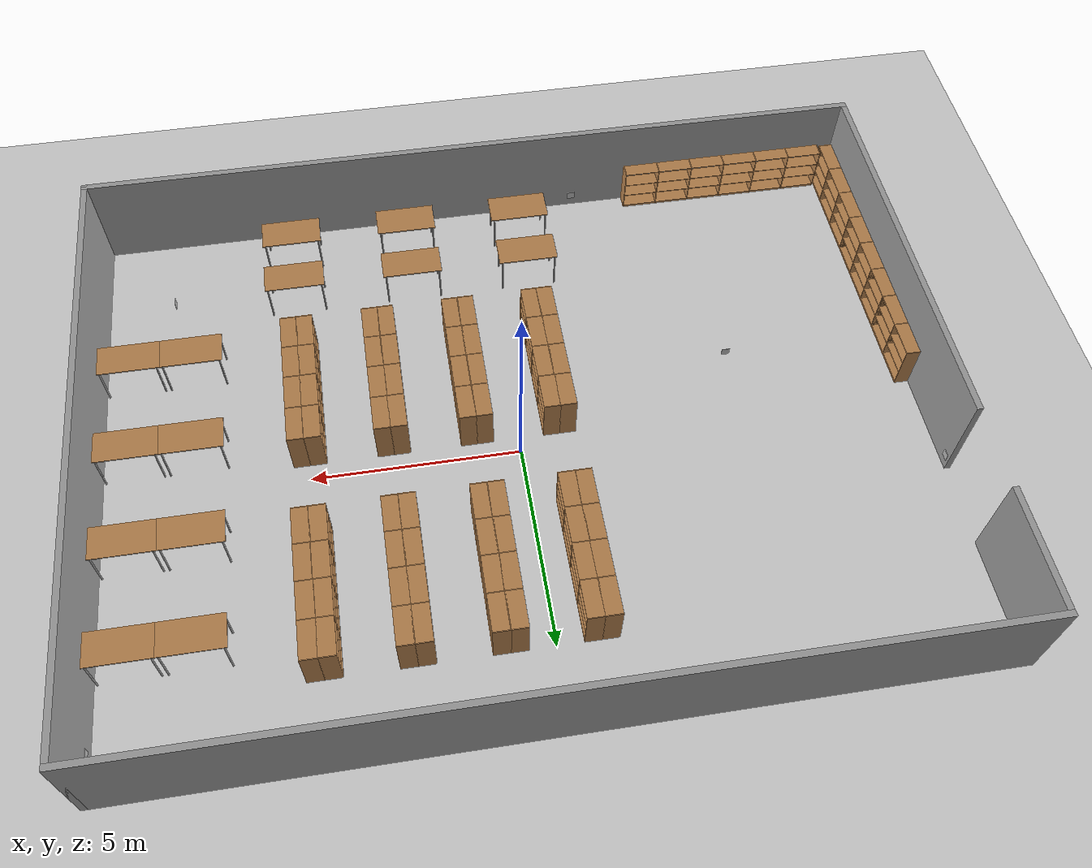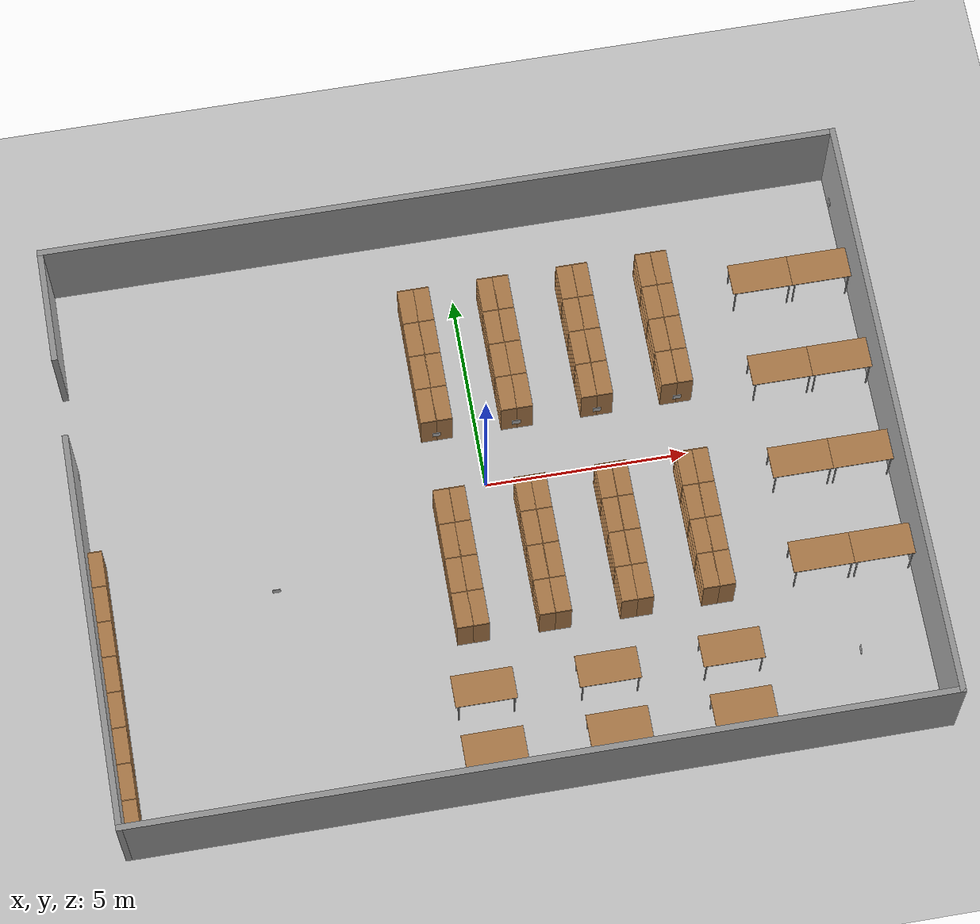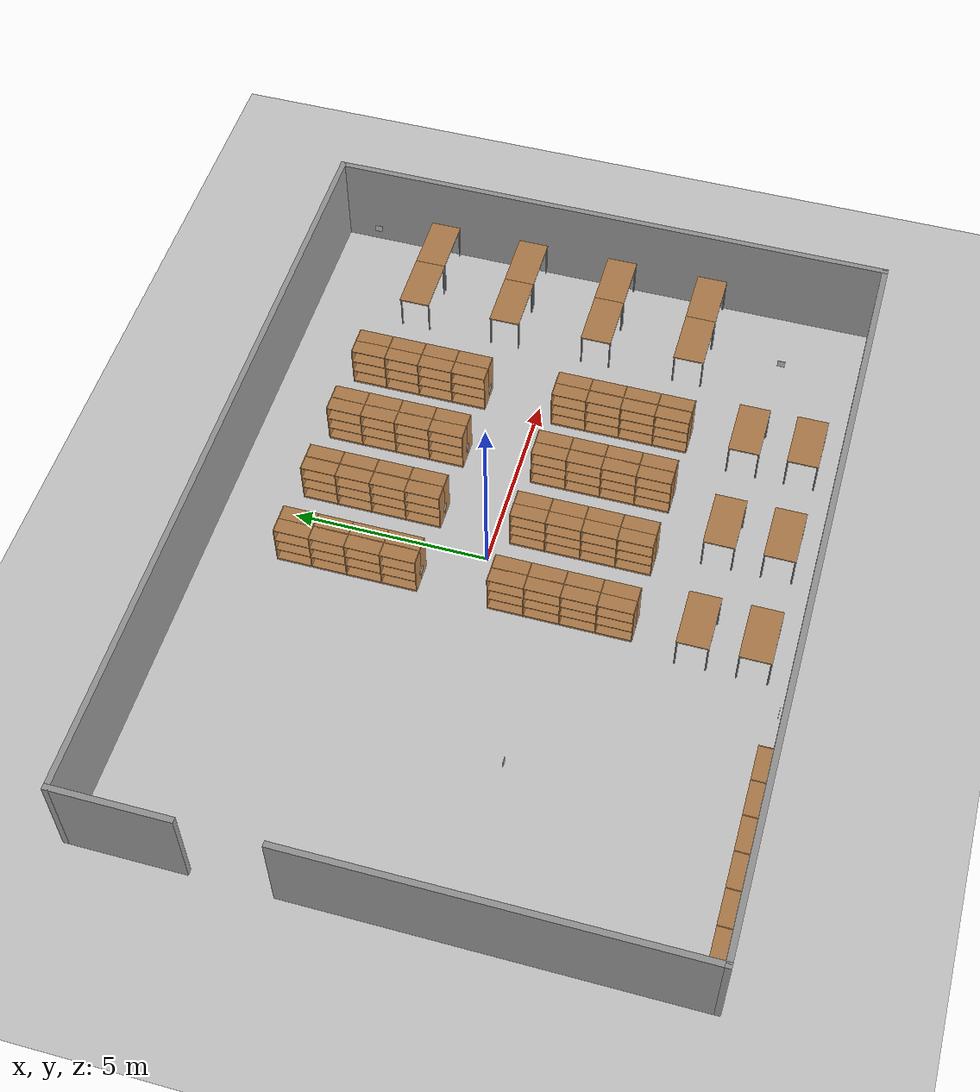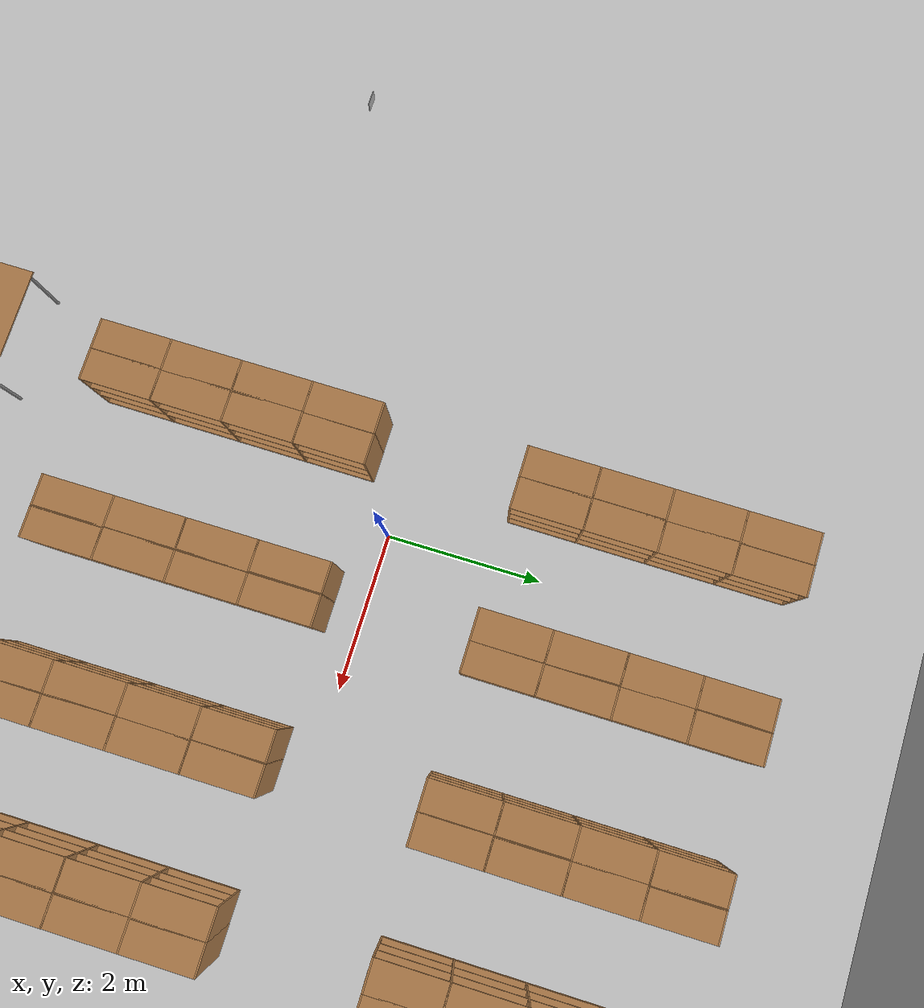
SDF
<sdf version="1.7">
 <world name="default">
  <model name="ground_plane">
   <static>1</static>
   <link name="link">
    <collision name="collision">
     <geometry><plane><normal>0 0 1</normal><size>100 100</size></plane></geometry>
     <surface><friction><ode><mu>100</mu><mu2>50</mu2></ode></friction></surface>
    </collision>
    <visual name="visual">
     <cast_shadows>0</cast_shadows>
     <geometry><plane><normal>0 0 1</normal><size>100 100</size></plane></geometry>
     <material>
      <script><uri>file://media/materials/scripts/gazebo.material</uri><name>Gazebo/Grey</name></script>
     </material>
    </visual>
   </link>
  </model>
  <light name="sun" type="directional">
   <pose>0 0 10 0 -0 0</pose>
   <diffuse>0.8 0.8 0.8 1</diffuse>
   <specular>0.2 0.2 0.2 1</specular>
   <attenuation>
    <range>1000</range>
    <constant>0.9</constant>
    <linear>0.01</linear>
    <quadratic>0.001</quadratic>
   </attenuation>
   <direction>-0.5 0.1 -0.9</direction>
   <spot><inner_angle>0</inner_angle><outer_angle>0</outer_angle><falloff>0</falloff></spot>
  </light>
  <scene><shadows>0</shadows><ambient>0.4 0.4 0.4 1</ambient><background>0.7 0.7 0.7 1</background></scene>
  <physics type="ode">
   <real_time_update_rate>1000</real_time_update_rate>
   <max_step_size>0.001</max_step_size>
   <real_time_factor>1</real_time_factor>
   <ode>
    <solver>
     <type>quick</type>
     <iters>150</iters>
     <precon_iters>0</precon_iters>
     <sor>1.4</sor>
     <use_dynamic_moi_rescaling>1</use_dynamic_moi_rescaling>
    </solver>
    <constraints>
     <cfm>1e-05</cfm>
     <erp>0.2</erp>
     <contact_max_correcting_vel>2000</contact_max_correcting_vel>
     <contact_surface_layer>0.01</contact_surface_layer>
    </constraints>
   </ode>
  </physics>
  <gravity>0 0 -9.8</gravity>
  <magnetic_field>6e-06 2.3e-05 -4.2e-05</magnetic_field>
  <atmosphere type="adiabatic"/>
  <audio><device>default</device></audio>
  <spherical_coordinates>
   <surface_model>EARTH_WGS84</surface_model>
   <latitude_deg>0</latitude_deg>
   <longitude_deg>0</longitude_deg>
   <elevation>0</elevation>
   <heading_deg>0</heading_deg>
  </spherical_coordinates>
  <model name="itu_walls">
   <pose>-0.001584 -0.50836 0 0 -0 0</pose>
   <link name="Wall_2">
    <collision name="Wall_2_Collision">
     <geometry><box><size>20 0.15 2.5</size></box></geometry>
     <pose>0 0 1.25 0 -0 0</pose>
    </collision>
    <visual name="Wall_2_Visual">
     <pose>0 0 1.25 0 -0 0</pose>
     <geometry><box><size>20 0.15 2.5</size></box></geometry>
     <material>
      <script><uri>file://media/materials/scripts/gazebo.material</uri><name>Gazebo/Grey</name></script>
      <ambient>1 1 1 1</ambient>
     </material>
     <meta><layer>0</layer></meta>
    </visual>
    <pose>0 7.425 0 0 -0 0</pose>
   </link>
   <link name="Wall_3">
    <collision name="Wall_3_Collision">
     <geometry><box><size>15 0.15 2.5</size></box></geometry>
     <pose>0 0 1.25 0 -0 0</pose>
    </collision>
    <visual name="Wall_3_Visual">
     <pose>0 0 1.25 0 -0 0</pose>
     <geometry><box><size>15 0.15 2.5</size></box></geometry>
     <material>
      <script><uri>file://media/materials/scripts/gazebo.material</uri><name>Gazebo/Grey</name></script>
      <ambient>1 1 1 1</ambient>
     </material>
     <meta><layer>0</layer></meta>
    </visual>
    <pose>9.925 0 0 0 -0 -1.5708</pose>
   </link>
   <link name="Wall_4">
    <collision name="Wall_4_Collision">
     <geometry><box><size>20 0.15 2.5</size></box></geometry>
     <pose>0 0 1.25 0 -0 0</pose>
    </collision>
    <visual name="Wall_4_Visual">
     <pose>0 0 1.25 0 -0 0</pose>
     <geometry><box><size>20 0.15 2.5</size></box></geometry>
     <material>
      <script><uri>file://media/materials/scripts/gazebo.material</uri><name>Gazebo/Grey</name></script>
      <ambient>1 1 1 1</ambient>
     </material>
     <meta><layer>0</layer></meta>
    </visual>
    <pose>0 -7.425 0 0 -0 3.14159</pose>
   </link>
   <link name="Wall_5">
    <collision name="Wall_5_Collision">
     <geometry><box><size>10 0.15 2.5</size></box></geometry>
     <pose>0 0 1.25 0 -0 0</pose>
    </collision>
    <visual name="Wall_5_Visual">
     <pose>0 0 1.25 0 -0 0</pose>
     <geometry><box><size>10 0.15 2.5</size></box></geometry>
     <material>
      <script><uri>file://media/materials/scripts/gazebo.material</uri><name>Gazebo/Grey</name></script>
      <ambient>1 1 1 1</ambient>
     </material>
     <meta><layer>0</layer></meta>
    </visual>
    <pose>-9.925 -2.5 0 0 -0 1.5708</pose>
   </link>
   <link name="Wall_7">
    <collision name="Wall_7_Collision">
     <geometry><box><size>3 0.15 2.5</size></box></geometry>
     <pose>0 0 1.25 0 -0 0</pose>
    </collision>
    <visual name="Wall_7_Visual">
     <pose>0 0 1.25 0 -0 0</pose>
     <geometry><box><size>3 0.15 2.5</size></box></geometry>
     <material>
      <script><uri>file://media/materials/scripts/gazebo.material</uri><name>Gazebo/Grey</name></script>
      <ambient>1 1 1 1</ambient>
     </material>
     <meta><layer>0</layer></meta>
    </visual>
    <pose>-9.925 6 0 0 -0 -1.5708</pose>
   </link>
   <static>1</static>
  </model>
  <model name="right_A_0">
   <static>1</static>
   <link name="link">
    <inertial><mass>1</mass></inertial>
    <visual name="visual1">
     <pose>0 0.005 0.6 0 -0 0</pose>
     <geometry><box><size>0.9 0.01 1.2</size></box></geometry>
     <material>
      <script><uri>file://media/materials/scripts/gazebo.material</uri><name>Gazebo/Wood</name></script>
     </material>
    </visual>
    <visual name="visual2">
     <pose>0.45 -0.195 0.6 0 -0 0</pose>
     <geometry><box><size>0.02 0.4 1.2</size></box></geometry>
     <material>
      <script><uri>file://media/materials/scripts/gazebo.material</uri><name>Gazebo/Wood</name></script>
     </material>
    </visual>
    <visual name="visual3">
     <pose>-0.45 -0.195 0.6 0 -0 0</pose>
     <geometry><box><size>0.02 0.4 1.2</size></box></geometry>
     <material>
      <script><uri>file://media/materials/scripts/gazebo.material</uri><name>Gazebo/Wood</name></script>
     </material>
    </visual>
    <visual name="visual4">
     <pose>0 -0.195 0.03 0 -0 0</pose>
     <geometry><box><size>0.88 0.4 0.06</size></box></geometry>
     <material>
      <script><uri>file://media/materials/scripts/gazebo.material</uri><name>Gazebo/Wood</name></script>
     </material>
    </visual>
    <visual name="visual5">
     <pose>0 -0.195 1.19 0 -0 0</pose>
     <geometry><box><size>0.88 0.4 0.02</size></box></geometry>
     <material>
      <script><uri>file://media/materials/scripts/gazebo.material</uri><name>Gazebo/Wood</name></script>
     </material>
    </visual>
    <visual name="visual6">
     <pose>0 -0.195 0.43 0 -0 0</pose>
     <geometry><box><size>0.88 0.4 0.02</size></box></geometry>
     <material>
      <script><uri>file://media/materials/scripts/gazebo.material</uri><name>Gazebo/Wood</name></script>
     </material>
    </visual>
    <visual name="visual7">
     <pose>0 -0.195 0.8 0 -0 0</pose>
     <geometry><box><size>0.88 0.4 0.02</size></box></geometry>
     <material>
      <script><uri>file://media/materials/scripts/gazebo.material</uri><name>Gazebo/Wood</name></script>
     </material>
    </visual>
    <collision name="unified_hitbox">
     <pose>0 -0.1925 0.6 0 -0 0</pose>
     <geometry><box><size>0.92 0.405 1.2</size></box></geometry>
    </collision>
   </link>
   <pose>5 4.55 0 0 -0 1.57</pose>
  </model>
  <model name="right_A_1">
   <static>1</static>
   <link name="link">
    <inertial><mass>1</mass></inertial>
    <visual name="visual1">
     <pose>0 0.005 0.6 0 -0 0</pose>
     <geometry><box><size>0.9 0.01 1.2</size></box></geometry>
     <material>
      <script><uri>file://media/materials/scripts/gazebo.material</uri><name>Gazebo/Wood</name></script>
     </material>
    </visual>
    <visual name="visual2">
     <pose>0.45 -0.195 0.6 0 -0 0</pose>
     <geometry><box><size>0.02 0.4 1.2</size></box></geometry>
     <material>
      <script><uri>file://media/materials/scripts/gazebo.material</uri><name>Gazebo/Wood</name></script>
     </material>
    </visual>
    <visual name="visual3">
     <pose>-0.45 -0.195 0.6 0 -0 0</pose>
     <geometry><box><size>0.02 0.4 1.2</size></box></geometry>
     <material>
      <script><uri>file://media/materials/scripts/gazebo.material</uri><name>Gazebo/Wood</name></script>
     </material>
    </visual>
    <visual name="visual4">
     <pose>0 -0.195 0.03 0 -0 0</pose>
     <geometry><box><size>0.88 0.4 0.06</size></box></geometry>
     <material>
      <script><uri>file://media/materials/scripts/gazebo.material</uri><name>Gazebo/Wood</name></script>
     </material>
    </visual>
    <visual name="visual5">
     <pose>0 -0.195 1.19 0 -0 0</pose>
     <geometry><box><size>0.88 0.4 0.02</size></box></geometry>
     <material>
      <script><uri>file://media/materials/scripts/gazebo.material</uri><name>Gazebo/Wood</name></script>
     </material>
    </visual>
    <visual name="visual6">
     <pose>0 -0.195 0.43 0 -0 0</pose>
     <geometry><box><size>0.88 0.4 0.02</size></box></geometry>
     <material>
      <script><uri>file://media/materials/scripts/gazebo.material</uri><name>Gazebo/Wood</name></script>
     </material>
    </visual>
    <visual name="visual7">
     <pose>0 -0.195 0.8 0 -0 0</pose>
     <geometry><box><size>0.88 0.4 0.02</size></box></geometry>
     <material>
      <script><uri>file://media/materials/scripts/gazebo.material</uri><name>Gazebo/Wood</name></script>
     </material>
    </visual>
    <collision name="unified_hitbox">
     <pose>0 -0.1925 0.6 0 -0 0</pose>
     <geometry><box><size>0.92 0.405 1.2</size></box></geometry>
    </collision>
   </link>
   <pose>5 3.65 0 0 -0 1.57</pose>
  </model>
  <model name="right_A_2">
   <static>1</static>
   <link name="link">
    <inertial><mass>1</mass></inertial>
    <visual name="visual1">
     <pose>0 0.005 0.6 0 -0 0</pose>
     <geometry><box><size>0.9 0.01 1.2</size></box></geometry>
     <material>
      <script><uri>file://media/materials/scripts/gazebo.material</uri><name>Gazebo/Wood</name></script>
     </material>
    </visual>
    <visual name="visual2">
     <pose>0.45 -0.195 0.6 0 -0 0</pose>
     <geometry><box><size>0.02 0.4 1.2</size></box></geometry>
     <material>
      <script><uri>file://media/materials/scripts/gazebo.material</uri><name>Gazebo/Wood</name></script>
     </material>
    </visual>
    <visual name="visual3">
     <pose>-0.45 -0.195 0.6 0 -0 0</pose>
     <geometry><box><size>0.02 0.4 1.2</size></box></geometry>
     <material>
      <script><uri>file://media/materials/scripts/gazebo.material</uri><name>Gazebo/Wood</name></script>
     </material>
    </visual>
    <visual name="visual4">
     <pose>0 -0.195 0.03 0 -0 0</pose>
     <geometry><box><size>0.88 0.4 0.06</size></box></geometry>
     <material>
      <script><uri>file://media/materials/scripts/gazebo.material</uri><name>Gazebo/Wood</name></script>
     </material>
    </visual>
    <visual name="visual5">
     <pose>0 -0.195 1.19 0 -0 0</pose>
     <geometry><box><size>0.88 0.4 0.02</size></box></geometry>
     <material>
      <script><uri>file://media/materials/scripts/gazebo.material</uri><name>Gazebo/Wood</name></script>
     </material>
    </visual>
    <visual name="visual6">
     <pose>0 -0.195 0.43 0 -0 0</pose>
     <geometry><box><size>0.88 0.4 0.02</size></box></geometry>
     <material>
      <script><uri>file://media/materials/scripts/gazebo.material</uri><name>Gazebo/Wood</name></script>
     </material>
    </visual>
    <visual name="visual7">
     <pose>0 -0.195 0.8 0 -0 0</pose>
     <geometry><box><size>0.88 0.4 0.02</size></box></geometry>
     <material>
      <script><uri>file://media/materials/scripts/gazebo.material</uri><name>Gazebo/Wood</name></script>
     </material>
    </visual>
    <collision name="unified_hitbox">
     <pose>0 -0.1925 0.6 0 -0 0</pose>
     <geometry><box><size>0.92 0.405 1.2</size></box></geometry>
    </collision>
   </link>
   <pose>5 2.75 0 0 -0 1.57</pose>
  </model>
  <model name="right_B_0">
   <static>1</static>
   <link name="link">
    <inertial><mass>1</mass></inertial>
    <visual name="visual1">
     <pose>0 0.005 0.6 0 -0 0</pose>
     <geometry><box><size>0.9 0.01 1.2</size></box></geometry>
     <material>
      <script><uri>file://media/materials/scripts/gazebo.material</uri><name>Gazebo/Wood</name></script>
     </material>
    </visual>
    <visual name="visual2">
     <pose>0.45 -0.195 0.6 0 -0 0</pose>
     <geometry><box><size>0.02 0.4 1.2</size></box></geometry>
     <material>
      <script><uri>file://media/materials/scripts/gazebo.material</uri><name>Gazebo/Wood</name></script>
     </material>
    </visual>
    <visual name="visual3">
     <pose>-0.45 -0.195 0.6 0 -0 0</pose>
     <geometry><box><size>0.02 0.4 1.2</size></box></geometry>
     <material>
      <script><uri>file://media/materials/scripts/gazebo.material</uri><name>Gazebo/Wood</name></script>
     </material>
    </visual>
    <visual name="visual4">
     <pose>0 -0.195 0.03 0 -0 0</pose>
     <geometry><box><size>0.88 0.4 0.06</size></box></geometry>
     <material>
      <script><uri>file://media/materials/scripts/gazebo.material</uri><name>Gazebo/Wood</name></script>
     </material>
    </visual>
    <visual name="visual5">
     <pose>0 -0.195 1.19 0 -0 0</pose>
     <geometry><box><size>0.88 0.4 0.02</size></box></geometry>
     <material>
      <script><uri>file://media/materials/scripts/gazebo.material</uri><name>Gazebo/Wood</name></script>
     </material>
    </visual>
    <visual name="visual6">
     <pose>0 -0.195 0.43 0 -0 0</pose>
     <geometry><box><size>0.88 0.4 0.02</size></box></geometry>
     <material>
      <script><uri>file://media/materials/scripts/gazebo.material</uri><name>Gazebo/Wood</name></script>
     </material>
    </visual>
    <visual name="visual7">
     <pose>0 -0.195 0.8 0 -0 0</pose>
     <geometry><box><size>0.88 0.4 0.02</size></box></geometry>
     <material>
      <script><uri>file://media/materials/scripts/gazebo.material</uri><name>Gazebo/Wood</name></script>
     </material>
    </visual>
    <collision name="unified_hitbox">
     <pose>0 -0.1925 0.6 0 -0 0</pose>
     <geometry><box><size>0.92 0.405 1.2</size></box></geometry>
    </collision>
   </link>
   <pose>5 4.55 0 0 0 -1.57</pose>
  </model>
  <model name="right_B_1">
   <static>1</static>
   <link name="link">
    <inertial><mass>1</mass></inertial>
    <visual name="visual1">
     <pose>0 0.005 0.6 0 -0 0</pose>
     <geometry><box><size>0.9 0.01 1.2</size></box></geometry>
     <material>
      <script><uri>file://media/materials/scripts/gazebo.material</uri><name>Gazebo/Wood</name></script>
     </material>
    </visual>
    <visual name="visual2">
     <pose>0.45 -0.195 0.6 0 -0 0</pose>
     <geometry><box><size>0.02 0.4 1.2</size></box></geometry>
     <material>
      <script><uri>file://media/materials/scripts/gazebo.material</uri><name>Gazebo/Wood</name></script>
     </material>
    </visual>
    <visual name="visual3">
     <pose>-0.45 -0.195 0.6 0 -0 0</pose>
     <geometry><box><size>0.02 0.4 1.2</size></box></geometry>
     <material>
      <script><uri>file://media/materials/scripts/gazebo.material</uri><name>Gazebo/Wood</name></script>
     </material>
    </visual>
    <visual name="visual4">
     <pose>0 -0.195 0.03 0 -0 0</pose>
     <geometry><box><size>0.88 0.4 0.06</size></box></geometry>
     <material>
      <script><uri>file://media/materials/scripts/gazebo.material</uri><name>Gazebo/Wood</name></script>
     </material>
    </visual>
    <visual name="visual5">
     <pose>0 -0.195 1.19 0 -0 0</pose>
     <geometry><box><size>0.88 0.4 0.02</size></box></geometry>
     <material>
      <script><uri>file://media/materials/scripts/gazebo.material</uri><name>Gazebo/Wood</name></script>
     </material>
    </visual>
    <visual name="visual6">
     <pose>0 -0.195 0.43 0 -0 0</pose>
     <geometry><box><size>0.88 0.4 0.02</size></box></geometry>
     <material>
      <script><uri>file://media/materials/scripts/gazebo.material</uri><name>Gazebo/Wood</name></script>
     </material>
    </visual>
    <visual name="visual7">
     <pose>0 -0.195 0.8 0 -0 0</pose>
     <geometry><box><size>0.88 0.4 0.02</size></box></geometry>
     <material>
      <script><uri>file://media/materials/scripts/gazebo.material</uri><name>Gazebo/Wood</name></script>
     </material>
    </visual>
    <collision name="unified_hitbox">
     <pose>0 -0.1925 0.6 0 -0 0</pose>
     <geometry><box><size>0.92 0.405 1.2</size></box></geometry>
    </collision>
   </link>
   <pose>5 3.65 0 0 0 -1.57</pose>
  </model>
  <model name="right_B_2">
   <static>1</static>
   <link name="link">
    <inertial><mass>1</mass></inertial>
    <visual name="visual1">
     <pose>0 0.005 0.6 0 -0 0</pose>
     <geometry><box><size>0.9 0.01 1.2</size></box></geometry>
     <material>
      <script><uri>file://media/materials/scripts/gazebo.material</uri><name>Gazebo/Wood</name></script>
     </material>
    </visual>
    <visual name="visual2">
     <pose>0.45 -0.195 0.6 0 -0 0</pose>
     <geometry><box><size>0.02 0.4 1.2</size></box></geometry>
     <material>
      <script><uri>file://media/materials/scripts/gazebo.material</uri><name>Gazebo/Wood</name></script>
     </material>
    </visual>
    <visual name="visual3">
     <pose>-0.45 -0.195 0.6 0 -0 0</pose>
     <geometry><box><size>0.02 0.4 1.2</size></box></geometry>
     <material>
      <script><uri>file://media/materials/scripts/gazebo.material</uri><name>Gazebo/Wood</name></script>
     </material>
    </visual>
    <visual name="visual4">
     <pose>0 -0.195 0.03 0 -0 0</pose>
     <geometry><box><size>0.88 0.4 0.06</size></box></geometry>
     <material>
      <script><uri>file://media/materials/scripts/gazebo.material</uri><name>Gazebo/Wood</name></script>
     </material>
    </visual>
    <visual name="visual5">
     <pose>0 -0.195 1.19 0 -0 0</pose>
     <geometry><box><size>0.88 0.4 0.02</size></box></geometry>
     <material>
      <script><uri>file://media/materials/scripts/gazebo.material</uri><name>Gazebo/Wood</name></script>
     </material>
    </visual>
    <visual name="visual6">
     <pose>0 -0.195 0.43 0 -0 0</pose>
     <geometry><box><size>0.88 0.4 0.02</size></box></geometry>
     <material>
      <script><uri>file://media/materials/scripts/gazebo.material</uri><name>Gazebo/Wood</name></script>
     </material>
    </visual>
    <visual name="visual7">
     <pose>0 -0.195 0.8 0 -0 0</pose>
     <geometry><box><size>0.88 0.4 0.02</size></box></geometry>
     <material>
      <script><uri>file://media/materials/scripts/gazebo.material</uri><name>Gazebo/Wood</name></script>
     </material>
    </visual>
    <collision name="unified_hitbox">
     <pose>0 -0.1925 0.6 0 -0 0</pose>
     <geometry><box><size>0.92 0.405 1.2</size></box></geometry>
    </collision>
   </link>
   <pose>5 2.75 0 0 0 -1.57</pose>
  </model>
  <model name="sec3_A_0">
   <static>1</static>
   <link name="link">
    <inertial><mass>1</mass></inertial>
    <visual name="visual1">
     <pose>0 0.005 0.6 0 -0 0</pose>
     <geometry><box><size>0.9 0.01 1.2</size></box></geometry>
     <material>
      <script><uri>file://media/materials/scripts/gazebo.material</uri><name>Gazebo/Wood</name></script>
     </material>
    </visual>
    <visual name="visual2">
     <pose>0.45 -0.195 0.6 0 -0 0</pose>
     <geometry><box><size>0.02 0.4 1.2</size></box></geometry>
     <material>
      <script><uri>file://media/materials/scripts/gazebo.material</uri><name>Gazebo/Wood</name></script>
     </material>
    </visual>
    <visual name="visual3">
     <pose>-0.45 -0.195 0.6 0 -0 0</pose>
     <geometry><box><size>0.02 0.4 1.2</size></box></geometry>
     <material>
      <script><uri>file://media/materials/scripts/gazebo.material</uri><name>Gazebo/Wood</name></script>
     </material>
    </visual>
    <visual name="visual4">
     <pose>0 -0.195 0.03 0 -0 0</pose>
     <geometry><box><size>0.88 0.4 0.06</size></box></geometry>
     <material>
      <script><uri>file://media/materials/scripts/gazebo.material</uri><name>Gazebo/Wood</name></script>
     </material>
    </visual>
    <visual name="visual5">
     <pose>0 -0.195 1.19 0 -0 0</pose>
     <geometry><box><size>0.88 0.4 0.02</size></box></geometry>
     <material>
      <script><uri>file://media/materials/scripts/gazebo.material</uri><name>Gazebo/Wood</name></script>
     </material>
    </visual>
    <visual name="visual6">
     <pose>0 -0.195 0.43 0 -0 0</pose>
     <geometry><box><size>0.88 0.4 0.02</size></box></geometry>
     <material>
      <script><uri>file://media/materials/scripts/gazebo.material</uri><name>Gazebo/Wood</name></script>
     </material>
    </visual>
    <visual name="visual7">
     <pose>0 -0.195 0.8 0 -0 0</pose>
     <geometry><box><size>0.88 0.4 0.02</size></box></geometry>
     <material>
      <script><uri>file://media/materials/scripts/gazebo.material</uri><name>Gazebo/Wood</name></script>
     </material>
    </visual>
    <collision name="unified_hitbox">
     <pose>0 -0.1925 0.6 0 -0 0</pose>
     <geometry><box><size>0.92 0.405 1.2</size></box></geometry>
    </collision>
   </link>
   <pose>3 4.55 0 0 -0 1.57</pose>
  </model>
  <model name="sec3_A_1">
   <static>1</static>
   <link name="link">
    <inertial><mass>1</mass></inertial>
    <visual name="visual1">
     <pose>0 0.005 0.6 0 -0 0</pose>
     <geometry><box><size>0.9 0.01 1.2</size></box></geometry>
     <material>
      <script><uri>file://media/materials/scripts/gazebo.material</uri><name>Gazebo/Wood</name></script>
     </material>
    </visual>
    <visual name="visual2">
     <pose>0.45 -0.195 0.6 0 -0 0</pose>
     <geometry><box><size>0.02 0.4 1.2</size></box></geometry>
     <material>
      <script><uri>file://media/materials/scripts/gazebo.material</uri><name>Gazebo/Wood</name></script>
     </material>
    </visual>
    <visual name="visual3">
     <pose>-0.45 -0.195 0.6 0 -0 0</pose>
     <geometry><box><size>0.02 0.4 1.2</size></box></geometry>
     <material>
      <script><uri>file://media/materials/scripts/gazebo.material</uri><name>Gazebo/Wood</name></script>
     </material>
    </visual>
    <visual name="visual4">
     <pose>0 -0.195 0.03 0 -0 0</pose>
     <geometry><box><size>0.88 0.4 0.06</size></box></geometry>
     <material>
      <script><uri>file://media/materials/scripts/gazebo.material</uri><name>Gazebo/Wood</name></script>
     </material>
    </visual>
    <visual name="visual5">
     <pose>0 -0.195 1.19 0 -0 0</pose>
     <geometry><box><size>0.88 0.4 0.02</size></box></geometry>
     <material>
      <script><uri>file://media/materials/scripts/gazebo.material</uri><name>Gazebo/Wood</name></script>
     </material>
    </visual>
    <visual name="visual6">
     <pose>0 -0.195 0.43 0 -0 0</pose>
     <geometry><box><size>0.88 0.4 0.02</size></box></geometry>
     <material>
      <script><uri>file://media/materials/scripts/gazebo.material</uri><name>Gazebo/Wood</name></script>
     </material>
    </visual>
    <visual name="visual7">
     <pose>0 -0.195 0.8 0 -0 0</pose>
     <geometry><box><size>0.88 0.4 0.02</size></box></geometry>
     <material>
      <script><uri>file://media/materials/scripts/gazebo.material</uri><name>Gazebo/Wood</name></script>
     </material>
    </visual>
    <collision name="unified_hitbox">
     <pose>0 -0.1925 0.6 0 -0 0</pose>
     <geometry><box><size>0.92 0.405 1.2</size></box></geometry>
    </collision>
   </link>
   <pose>3 3.65 0 0 -0 1.57</pose>
  </model>
  <model name="sec3_A_2">
   <static>1</static>
   <link name="link">
    <inertial><mass>1</mass></inertial>
    <visual name="visual1">
     <pose>0 0.005 0.6 0 -0 0</pose>
     <geometry><box><size>0.9 0.01 1.2</size></box></geometry>
     <material>
      <script><uri>file://media/materials/scripts/gazebo.material</uri><name>Gazebo/Wood</name></script>
     </material>
    </visual>
    <visual name="visual2">
     <pose>0.45 -0.195 0.6 0 -0 0</pose>
     <geometry><box><size>0.02 0.4 1.2</size></box></geometry>
     <material>
      <script><uri>file://media/materials/scripts/gazebo.material</uri><name>Gazebo/Wood</name></script>
     </material>
    </visual>
    <visual name="visual3">
     <pose>-0.45 -0.195 0.6 0 -0 0</pose>
     <geometry><box><size>0.02 0.4 1.2</size></box></geometry>
     <material>
      <script><uri>file://media/materials/scripts/gazebo.material</uri><name>Gazebo/Wood</name></script>
     </material>
    </visual>
    <visual name="visual4">
     <pose>0 -0.195 0.03 0 -0 0</pose>
     <geometry><box><size>0.88 0.4 0.06</size></box></geometry>
     <material>
      <script><uri>file://media/materials/scripts/gazebo.material</uri><name>Gazebo/Wood</name></script>
     </material>
    </visual>
    <visual name="visual5">
     <pose>0 -0.195 1.19 0 -0 0</pose>
     <geometry><box><size>0.88 0.4 0.02</size></box></geometry>
     <material>
      <script><uri>file://media/materials/scripts/gazebo.material</uri><name>Gazebo/Wood</name></script>
     </material>
    </visual>
    <visual name="visual6">
     <pose>0 -0.195 0.43 0 -0 0</pose>
     <geometry><box><size>0.88 0.4 0.02</size></box></geometry>
     <material>
      <script><uri>file://media/materials/scripts/gazebo.material</uri><name>Gazebo/Wood</name></script>
     </material>
    </visual>
    <visual name="visual7">
     <pose>0 -0.195 0.8 0 -0 0</pose>
     <geometry><box><size>0.88 0.4 0.02</size></box></geometry>
     <material>
      <script><uri>file://media/materials/scripts/gazebo.material</uri><name>Gazebo/Wood</name></script>
     </material>
    </visual>
    <collision name="unified_hitbox">
     <pose>0 -0.1925 0.6 0 -0 0</pose>
     <geometry><box><size>0.92 0.405 1.2</size></box></geometry>
    </collision>
   </link>
   <pose>3 2.75 0 0 -0 1.57</pose>
  </model>
  <model name="sec3_B_0">
   <static>1</static>
   <link name="link">
    <inertial><mass>1</mass></inertial>
    <visual name="visual1">
     <pose>0 0.005 0.6 0 -0 0</pose>
     <geometry><box><size>0.9 0.01 1.2</size></box></geometry>
     <material>
      <script><uri>file://media/materials/scripts/gazebo.material</uri><name>Gazebo/Wood</name></script>
     </material>
    </visual>
    <visual name="visual2">
     <pose>0.45 -0.195 0.6 0 -0 0</pose>
     <geometry><box><size>0.02 0.4 1.2</size></box></geometry>
     <material>
      <script><uri>file://media/materials/scripts/gazebo.material</uri><name>Gazebo/Wood</name></script>
     </material>
    </visual>
    <visual name="visual3">
     <pose>-0.45 -0.195 0.6 0 -0 0</pose>
     <geometry><box><size>0.02 0.4 1.2</size></box></geometry>
     <material>
      <script><uri>file://media/materials/scripts/gazebo.material</uri><name>Gazebo/Wood</name></script>
     </material>
    </visual>
    <visual name="visual4">
     <pose>0 -0.195 0.03 0 -0 0</pose>
     <geometry><box><size>0.88 0.4 0.06</size></box></geometry>
     <material>
      <script><uri>file://media/materials/scripts/gazebo.material</uri><name>Gazebo/Wood</name></script>
     </material>
    </visual>
    <visual name="visual5">
     <pose>0 -0.195 1.19 0 -0 0</pose>
     <geometry><box><size>0.88 0.4 0.02</size></box></geometry>
     <material>
      <script><uri>file://media/materials/scripts/gazebo.material</uri><name>Gazebo/Wood</name></script>
     </material>
    </visual>
    <visual name="visual6">
     <pose>0 -0.195 0.43 0 -0 0</pose>
     <geometry><box><size>0.88 0.4 0.02</size></box></geometry>
     <material>
      <script><uri>file://media/materials/scripts/gazebo.material</uri><name>Gazebo/Wood</name></script>
     </material>
    </visual>
    <visual name="visual7">
     <pose>0 -0.195 0.8 0 -0 0</pose>
     <geometry><box><size>0.88 0.4 0.02</size></box></geometry>
     <material>
      <script><uri>file://media/materials/scripts/gazebo.material</uri><name>Gazebo/Wood</name></script>
     </material>
    </visual>
    <collision name="unified_hitbox">
     <pose>0 -0.1925 0.6 0 -0 0</pose>
     <geometry><box><size>0.92 0.405 1.2</size></box></geometry>
    </collision>
   </link>
   <pose>3 4.55 0 0 0 -1.57</pose>
  </model>
  <model name="sec3_B_1">
   <static>1</static>
   <link name="link">
    <inertial><mass>1</mass></inertial>
    <visual name="visual1">
     <pose>0 0.005 0.6 0 -0 0</pose>
     <geometry><box><size>0.9 0.01 1.2</size></box></geometry>
     <material>
      <script><uri>file://media/materials/scripts/gazebo.material</uri><name>Gazebo/Wood</name></script>
     </material>
    </visual>
    <visual name="visual2">
     <pose>0.45 -0.195 0.6 0 -0 0</pose>
     <geometry><box><size>0.02 0.4 1.2</size></box></geometry>
     <material>
      <script><uri>file://media/materials/scripts/gazebo.material</uri><name>Gazebo/Wood</name></script>
     </material>
    </visual>
    <visual name="visual3">
     <pose>-0.45 -0.195 0.6 0 -0 0</pose>
     <geometry><box><size>0.02 0.4 1.2</size></box></geometry>
     <material>
      <script><uri>file://media/materials/scripts/gazebo.material</uri><name>Gazebo/Wood</name></script>
     </material>
    </visual>
    <visual name="visual4">
     <pose>0 -0.195 0.03 0 -0 0</pose>
     <geometry><box><size>0.88 0.4 0.06</size></box></geometry>
     <material>
      <script><uri>file://media/materials/scripts/gazebo.material</uri><name>Gazebo/Wood</name></script>
     </material>
    </visual>
    <visual name="visual5">
     <pose>0 -0.195 1.19 0 -0 0</pose>
     <geometry><box><size>0.88 0.4 0.02</size></box></geometry>
     <material>
      <script><uri>file://media/materials/scripts/gazebo.material</uri><name>Gazebo/Wood</name></script>
     </material>
    </visual>
    <visual name="visual6">
     <pose>0 -0.195 0.43 0 -0 0</pose>
     <geometry><box><size>0.88 0.4 0.02</size></box></geometry>
     <material>
      <script><uri>file://media/materials/scripts/gazebo.material</uri><name>Gazebo/Wood</name></script>
     </material>
    </visual>
    <visual name="visual7">
     <pose>0 -0.195 0.8 0 -0 0</pose>
     <geometry><box><size>0.88 0.4 0.02</size></box></geometry>
     <material>
      <script><uri>file://media/materials/scripts/gazebo.material</uri><name>Gazebo/Wood</name></script>
     </material>
    </visual>
    <collision name="unified_hitbox">
     <pose>0 -0.1925 0.6 0 -0 0</pose>
     <geometry><box><size>0.92 0.405 1.2</size></box></geometry>
    </collision>
   </link>
   <pose>3 3.65 0 0 0 -1.57</pose>
  </model>
  <model name="sec3_B_2">
   <static>1</static>
   <link name="link">
    <inertial><mass>1</mass></inertial>
    <visual name="visual1">
     <pose>0 0.005 0.6 0 -0 0</pose>
     <geometry><box><size>0.9 0.01 1.2</size></box></geometry>
     <material>
      <script><uri>file://media/materials/scripts/gazebo.material</uri><name>Gazebo/Wood</name></script>
     </material>
    </visual>
    <visual name="visual2">
     <pose>0.45 -0.195 0.6 0 -0 0</pose>
     <geometry><box><size>0.02 0.4 1.2</size></box></geometry>
     <material>
      <script><uri>file://media/materials/scripts/gazebo.material</uri><name>Gazebo/Wood</name></script>
     </material>
    </visual>
    <visual name="visual3">
     <pose>-0.45 -0.195 0.6 0 -0 0</pose>
     <geometry><box><size>0.02 0.4 1.2</size></box></geometry>
     <material>
      <script><uri>file://media/materials/scripts/gazebo.material</uri><name>Gazebo/Wood</name></script>
     </material>
    </visual>
    <visual name="visual4">
     <pose>0 -0.195 0.03 0 -0 0</pose>
     <geometry><box><size>0.88 0.4 0.06</size></box></geometry>
     <material>
      <script><uri>file://media/materials/scripts/gazebo.material</uri><name>Gazebo/Wood</name></script>
     </material>
    </visual>
    <visual name="visual5">
     <pose>0 -0.195 1.19 0 -0 0</pose>
     <geometry><box><size>0.88 0.4 0.02</size></box></geometry>
     <material>
      <script><uri>file://media/materials/scripts/gazebo.material</uri><name>Gazebo/Wood</name></script>
     </material>
    </visual>
    <visual name="visual6">
     <pose>0 -0.195 0.43 0 -0 0</pose>
     <geometry><box><size>0.88 0.4 0.02</size></box></geometry>
     <material>
      <script><uri>file://media/materials/scripts/gazebo.material</uri><name>Gazebo/Wood</name></script>
     </material>
    </visual>
    <visual name="visual7">
     <pose>0 -0.195 0.8 0 -0 0</pose>
     <geometry><box><size>0.88 0.4 0.02</size></box></geometry>
     <material>
      <script><uri>file://media/materials/scripts/gazebo.material</uri><name>Gazebo/Wood</name></script>
     </material>
    </visual>
    <collision name="unified_hitbox">
     <pose>0 -0.1925 0.6 0 -0 0</pose>
     <geometry><box><size>0.92 0.405 1.2</size></box></geometry>
    </collision>
   </link>
   <pose>3 2.75 0 0 0 -1.57</pose>
  </model>
  <model name="sec1_A_0">
   <static>1</static>
   <link name="link">
    <inertial><mass>1</mass></inertial>
    <visual name="visual1">
     <pose>0 0.005 0.6 0 -0 0</pose>
     <geometry><box><size>0.9 0.01 1.2</size></box></geometry>
     <material>
      <script><uri>file://media/materials/scripts/gazebo.material</uri><name>Gazebo/Wood</name></script>
     </material>
    </visual>
    <visual name="visual2">
     <pose>0.45 -0.195 0.6 0 -0 0</pose>
     <geometry><box><size>0.02 0.4 1.2</size></box></geometry>
     <material>
      <script><uri>file://media/materials/scripts/gazebo.material</uri><name>Gazebo/Wood</name></script>
     </material>
    </visual>
    <visual name="visual3">
     <pose>-0.45 -0.195 0.6 0 -0 0</pose>
     <geometry><box><size>0.02 0.4 1.2</size></box></geometry>
     <material>
      <script><uri>file://media/materials/scripts/gazebo.material</uri><name>Gazebo/Wood</name></script>
     </material>
    </visual>
    <visual name="visual4">
     <pose>0 -0.195 0.03 0 -0 0</pose>
     <geometry><box><size>0.88 0.4 0.06</size></box></geometry>
     <material>
      <script><uri>file://media/materials/scripts/gazebo.material</uri><name>Gazebo/Wood</name></script>
     </material>
    </visual>
    <visual name="visual5">
     <pose>0 -0.195 1.19 0 -0 0</pose>
     <geometry><box><size>0.88 0.4 0.02</size></box></geometry>
     <material>
      <script><uri>file://media/materials/scripts/gazebo.material</uri><name>Gazebo/Wood</name></script>
     </material>
    </visual>
    <visual name="visual6">
     <pose>0 -0.195 0.43 0 -0 0</pose>
     <geometry><box><size>0.88 0.4 0.02</size></box></geometry>
     <material>
      <script><uri>file://media/materials/scripts/gazebo.material</uri><name>Gazebo/Wood</name></script>
     </material>
    </visual>
    <visual name="visual7">
     <pose>0 -0.195 0.8 0 -0 0</pose>
     <geometry><box><size>0.88 0.4 0.02</size></box></geometry>
     <material>
      <script><uri>file://media/materials/scripts/gazebo.material</uri><name>Gazebo/Wood</name></script>
     </material>
    </visual>
    <collision name="unified_hitbox">
     <pose>0 -0.1925 0.6 0 -0 0</pose>
     <geometry><box><size>0.92 0.405 1.2</size></box></geometry>
    </collision>
   </link>
   <pose>1 4.55 0 0 -0 1.57</pose>
  </model>
  <model name="sec1_A_1">
   <static>1</static>
   <link name="link">
    <inertial><mass>1</mass></inertial>
    <visual name="visual1">
     <pose>0 0.005 0.6 0 -0 0</pose>
     <geometry><box><size>0.9 0.01 1.2</size></box></geometry>
     <material>
      <script><uri>file://media/materials/scripts/gazebo.material</uri><name>Gazebo/Wood</name></script>
     </material>
    </visual>
    <visual name="visual2">
     <pose>0.45 -0.195 0.6 0 -0 0</pose>
     <geometry><box><size>0.02 0.4 1.2</size></box></geometry>
     <material>
      <script><uri>file://media/materials/scripts/gazebo.material</uri><name>Gazebo/Wood</name></script>
     </material>
    </visual>
    <visual name="visual3">
     <pose>-0.45 -0.195 0.6 0 -0 0</pose>
     <geometry><box><size>0.02 0.4 1.2</size></box></geometry>
     <material>
      <script><uri>file://media/materials/scripts/gazebo.material</uri><name>Gazebo/Wood</name></script>
     </material>
    </visual>
    <visual name="visual4">
     <pose>0 -0.195 0.03 0 -0 0</pose>
     <geometry><box><size>0.88 0.4 0.06</size></box></geometry>
     <material>
      <script><uri>file://media/materials/scripts/gazebo.material</uri><name>Gazebo/Wood</name></script>
     </material>
    </visual>
    <visual name="visual5">
     <pose>0 -0.195 1.19 0 -0 0</pose>
     <geometry><box><size>0.88 0.4 0.02</size></box></geometry>
     <material>
      <script><uri>file://media/materials/scripts/gazebo.material</uri><name>Gazebo/Wood</name></script>
     </material>
    </visual>
    <visual name="visual6">
     <pose>0 -0.195 0.43 0 -0 0</pose>
     <geometry><box><size>0.88 0.4 0.02</size></box></geometry>
     <material>
      <script><uri>file://media/materials/scripts/gazebo.material</uri><name>Gazebo/Wood</name></script>
     </material>
    </visual>
    <visual name="visual7">
     <pose>0 -0.195 0.8 0 -0 0</pose>
     <geometry><box><size>0.88 0.4 0.02</size></box></geometry>
     <material>
      <script><uri>file://media/materials/scripts/gazebo.material</uri><name>Gazebo/Wood</name></script>
     </material>
    </visual>
    <collision name="unified_hitbox">
     <pose>0 -0.1925 0.6 0 -0 0</pose>
     <geometry><box><size>0.92 0.405 1.2</size></box></geometry>
    </collision>
   </link>
   <pose>1 3.65 0 0 -0 1.57</pose>
  </model>
  <model name="sec1_A_2">
   <static>1</static>
   <link name="link">
    <inertial><mass>1</mass></inertial>
    <visual name="visual1">
     <pose>0 0.005 0.6 0 -0 0</pose>
     <geometry><box><size>0.9 0.01 1.2</size></box></geometry>
     <material>
      <script><uri>file://media/materials/scripts/gazebo.material</uri><name>Gazebo/Wood</name></script>
     </material>
    </visual>
    <visual name="visual2">
     <pose>0.45 -0.195 0.6 0 -0 0</pose>
     <geometry><box><size>0.02 0.4 1.2</size></box></geometry>
     <material>
      <script><uri>file://media/materials/scripts/gazebo.material</uri><name>Gazebo/Wood</name></script>
     </material>
    </visual>
    <visual name="visual3">
     <pose>-0.45 -0.195 0.6 0 -0 0</pose>
     <geometry><box><size>0.02 0.4 1.2</size></box></geometry>
     <material>
      <script><uri>file://media/materials/scripts/gazebo.material</uri><name>Gazebo/Wood</name></script>
     </material>
    </visual>
    <visual name="visual4">
     <pose>0 -0.195 0.03 0 -0 0</pose>
     <geometry><box><size>0.88 0.4 0.06</size></box></geometry>
     <material>
      <script><uri>file://media/materials/scripts/gazebo.material</uri><name>Gazebo/Wood</name></script>
     </material>
    </visual>
    <visual name="visual5">
     <pose>0 -0.195 1.19 0 -0 0</pose>
     <geometry><box><size>0.88 0.4 0.02</size></box></geometry>
     <material>
      <script><uri>file://media/materials/scripts/gazebo.material</uri><name>Gazebo/Wood</name></script>
     </material>
    </visual>
    <visual name="visual6">
     <pose>0 -0.195 0.43 0 -0 0</pose>
     <geometry><box><size>0.88 0.4 0.02</size></box></geometry>
     <material>
      <script><uri>file://media/materials/scripts/gazebo.material</uri><name>Gazebo/Wood</name></script>
     </material>
    </visual>
    <visual name="visual7">
     <pose>0 -0.195 0.8 0 -0 0</pose>
     <geometry><box><size>0.88 0.4 0.02</size></box></geometry>
     <material>
      <script><uri>file://media/materials/scripts/gazebo.material</uri><name>Gazebo/Wood</name></script>
     </material>
    </visual>
    <collision name="unified_hitbox">
     <pose>0 -0.1925 0.6 0 -0 0</pose>
     <geometry><box><size>0.92 0.405 1.2</size></box></geometry>
    </collision>
   </link>
   <pose>1 2.75 0 0 -0 1.57</pose>
  </model>
  <model name="sec1_B_0">
   <static>1</static>
   <link name="link">
    <inertial><mass>1</mass></inertial>
    <visual name="visual1">
     <pose>0 0.005 0.6 0 -0 0</pose>
     <geometry><box><size>0.9 0.01 1.2</size></box></geometry>
     <material>
      <script><uri>file://media/materials/scripts/gazebo.material</uri><name>Gazebo/Wood</name></script>
     </material>
    </visual>
    <visual name="visual2">
     <pose>0.45 -0.195 0.6 0 -0 0</pose>
     <geometry><box><size>0.02 0.4 1.2</size></box></geometry>
     <material>
      <script><uri>file://media/materials/scripts/gazebo.material</uri><name>Gazebo/Wood</name></script>
     </material>
    </visual>
    <visual name="visual3">
     <pose>-0.45 -0.195 0.6 0 -0 0</pose>
     <geometry><box><size>0.02 0.4 1.2</size></box></geometry>
     <material>
      <script><uri>file://media/materials/scripts/gazebo.material</uri><name>Gazebo/Wood</name></script>
     </material>
    </visual>
    <visual name="visual4">
     <pose>0 -0.195 0.03 0 -0 0</pose>
     <geometry><box><size>0.88 0.4 0.06</size></box></geometry>
     <material>
      <script><uri>file://media/materials/scripts/gazebo.material</uri><name>Gazebo/Wood</name></script>
     </material>
    </visual>
    <visual name="visual5">
     <pose>0 -0.195 1.19 0 -0 0</pose>
     <geometry><box><size>0.88 0.4 0.02</size></box></geometry>
     <material>
      <script><uri>file://media/materials/scripts/gazebo.material</uri><name>Gazebo/Wood</name></script>
     </material>
    </visual>
    <visual name="visual6">
     <pose>0 -0.195 0.43 0 -0 0</pose>
     <geometry><box><size>0.88 0.4 0.02</size></box></geometry>
     <material>
      <script><uri>file://media/materials/scripts/gazebo.material</uri><name>Gazebo/Wood</name></script>
     </material>
    </visual>
    <visual name="visual7">
     <pose>0 -0.195 0.8 0 -0 0</pose>
     <geometry><box><size>0.88 0.4 0.02</size></box></geometry>
     <material>
      <script><uri>file://media/materials/scripts/gazebo.material</uri><name>Gazebo/Wood</name></script>
     </material>
    </visual>
    <collision name="unified_hitbox">
     <pose>0 -0.1925 0.6 0 -0 0</pose>
     <geometry><box><size>0.92 0.405 1.2</size></box></geometry>
    </collision>
   </link>
   <pose>1 4.55 0 0 0 -1.57</pose>
  </model>
  <model name="sec1_B_1">
   <static>1</static>
   <link name="link">
    <inertial><mass>1</mass></inertial>
    <visual name="visual1">
     <pose>0 0.005 0.6 0 -0 0</pose>
     <geometry><box><size>0.9 0.01 1.2</size></box></geometry>
     <material>
      <script><uri>file://media/materials/scripts/gazebo.material</uri><name>Gazebo/Wood</name></script>
     </material>
    </visual>
    <visual name="visual2">
     <pose>0.45 -0.195 0.6 0 -0 0</pose>
     <geometry><box><size>0.02 0.4 1.2</size></box></geometry>
     <material>
      <script><uri>file://media/materials/scripts/gazebo.material</uri><name>Gazebo/Wood</name></script>
     </material>
    </visual>
    <visual name="visual3">
     <pose>-0.45 -0.195 0.6 0 -0 0</pose>
     <geometry><box><size>0.02 0.4 1.2</size></box></geometry>
     <material>
      <script><uri>file://media/materials/scripts/gazebo.material</uri><name>Gazebo/Wood</name></script>
     </material>
    </visual>
    <visual name="visual4">
     <pose>0 -0.195 0.03 0 -0 0</pose>
     <geometry><box><size>0.88 0.4 0.06</size></box></geometry>
     <material>
      <script><uri>file://media/materials/scripts/gazebo.material</uri><name>Gazebo/Wood</name></script>
     </material>
    </visual>
    <visual name="visual5">
     <pose>0 -0.195 1.19 0 -0 0</pose>
     <geometry><box><size>0.88 0.4 0.02</size></box></geometry>
     <material>
      <script><uri>file://media/materials/scripts/gazebo.material</uri><name>Gazebo/Wood</name></script>
     </material>
    </visual>
    <visual name="visual6">
     <pose>0 -0.195 0.43 0 -0 0</pose>
     <geometry><box><size>0.88 0.4 0.02</size></box></geometry>
     <material>
      <script><uri>file://media/materials/scripts/gazebo.material</uri><name>Gazebo/Wood</name></script>
     </material>
    </visual>
    <visual name="visual7">
     <pose>0 -0.195 0.8 0 -0 0</pose>
     <geometry><box><size>0.88 0.4 0.02</size></box></geometry>
     <material>
      <script><uri>file://media/materials/scripts/gazebo.material</uri><name>Gazebo/Wood</name></script>
     </material>
    </visual>
    <collision name="unified_hitbox">
     <pose>0 -0.1925 0.6 0 -0 0</pose>
     <geometry><box><size>0.92 0.405 1.2</size></box></geometry>
    </collision>
   </link>
   <pose>1 3.65 0 0 0 -1.57</pose>
  </model>
  <model name="sec1_B_2">
   <static>1</static>
   <link name="link">
    <inertial><mass>1</mass></inertial>
    <visual name="visual1">
     <pose>0 0.005 0.6 0 -0 0</pose>
     <geometry><box><size>0.9 0.01 1.2</size></box></geometry>
     <material>
      <script><uri>file://media/materials/scripts/gazebo.material</uri><name>Gazebo/Wood</name></script>
     </material>
    </visual>
    <visual name="visual2">
     <pose>0.45 -0.195 0.6 0 -0 0</pose>
     <geometry><box><size>0.02 0.4 1.2</size></box></geometry>
     <material>
      <script><uri>file://media/materials/scripts/gazebo.material</uri><name>Gazebo/Wood</name></script>
     </material>
    </visual>
    <visual name="visual3">
     <pose>-0.45 -0.195 0.6 0 -0 0</pose>
     <geometry><box><size>0.02 0.4 1.2</size></box></geometry>
     <material>
      <script><uri>file://media/materials/scripts/gazebo.material</uri><name>Gazebo/Wood</name></script>
     </material>
    </visual>
    <visual name="visual4">
     <pose>0 -0.195 0.03 0 -0 0</pose>
     <geometry><box><size>0.88 0.4 0.06</size></box></geometry>
     <material>
      <script><uri>file://media/materials/scripts/gazebo.material</uri><name>Gazebo/Wood</name></script>
     </material>
    </visual>
    <visual name="visual5">
     <pose>0 -0.195 1.19 0 -0 0</pose>
     <geometry><box><size>0.88 0.4 0.02</size></box></geometry>
     <material>
      <script><uri>file://media/materials/scripts/gazebo.material</uri><name>Gazebo/Wood</name></script>
     </material>
    </visual>
    <visual name="visual6">
     <pose>0 -0.195 0.43 0 -0 0</pose>
     <geometry><box><size>0.88 0.4 0.02</size></box></geometry>
     <material>
      <script><uri>file://media/materials/scripts/gazebo.material</uri><name>Gazebo/Wood</name></script>
     </material>
    </visual>
    <visual name="visual7">
     <pose>0 -0.195 0.8 0 -0 0</pose>
     <geometry><box><size>0.88 0.4 0.02</size></box></geometry>
     <material>
      <script><uri>file://media/materials/scripts/gazebo.material</uri><name>Gazebo/Wood</name></script>
     </material>
    </visual>
    <collision name="unified_hitbox">
     <pose>0 -0.1925 0.6 0 -0 0</pose>
     <geometry><box><size>0.92 0.405 1.2</size></box></geometry>
    </collision>
   </link>
   <pose>1 2.75 0 0 0 -1.57</pose>
  </model>
  <model name="secNeg1_A_0">
   <static>1</static>
   <link name="link">
    <inertial><mass>1</mass></inertial>
    <visual name="visual1">
     <pose>0 0.005 0.6 0 -0 0</pose>
     <geometry><box><size>0.9 0.01 1.2</size></box></geometry>
     <material>
      <script><uri>file://media/materials/scripts/gazebo.material</uri><name>Gazebo/Wood</name></script>
     </material>
    </visual>
    <visual name="visual2">
     <pose>0.45 -0.195 0.6 0 -0 0</pose>
     <geometry><box><size>0.02 0.4 1.2</size></box></geometry>
     <material>
      <script><uri>file://media/materials/scripts/gazebo.material</uri><name>Gazebo/Wood</name></script>
     </material>
    </visual>
    <visual name="visual3">
     <pose>-0.45 -0.195 0.6 0 -0 0</pose>
     <geometry><box><size>0.02 0.4 1.2</size></box></geometry>
     <material>
      <script><uri>file://media/materials/scripts/gazebo.material</uri><name>Gazebo/Wood</name></script>
     </material>
    </visual>
    <visual name="visual4">
     <pose>0 -0.195 0.03 0 -0 0</pose>
     <geometry><box><size>0.88 0.4 0.06</size></box></geometry>
     <material>
      <script><uri>file://media/materials/scripts/gazebo.material</uri><name>Gazebo/Wood</name></script>
     </material>
    </visual>
    <visual name="visual5">
     <pose>0 -0.195 1.19 0 -0 0</pose>
     <geometry><box><size>0.88 0.4 0.02</size></box></geometry>
     <material>
      <script><uri>file://media/materials/scripts/gazebo.material</uri><name>Gazebo/Wood</name></script>
     </material>
    </visual>
    <visual name="visual6">
     <pose>0 -0.195 0.43 0 -0 0</pose>
     <geometry><box><size>0.88 0.4 0.02</size></box></geometry>
     <material>
      <script><uri>file://media/materials/scripts/gazebo.material</uri><name>Gazebo/Wood</name></script>
     </material>
    </visual>
    <visual name="visual7">
     <pose>0 -0.195 0.8 0 -0 0</pose>
     <geometry><box><size>0.88 0.4 0.02</size></box></geometry>
     <material>
      <script><uri>file://media/materials/scripts/gazebo.material</uri><name>Gazebo/Wood</name></script>
     </material>
    </visual>
    <collision name="unified_hitbox">
     <pose>0 -0.1925 0.6 0 -0 0</pose>
     <geometry><box><size>0.92 0.405 1.2</size></box></geometry>
    </collision>
   </link>
   <pose>-1 4.55 0 0 -0 1.57</pose>
  </model>
  <model name="secNeg1_A_1">
   <static>1</static>
   <link name="link">
    <inertial><mass>1</mass></inertial>
    <visual name="visual1">
     <pose>0 0.005 0.6 0 -0 0</pose>
     <geometry><box><size>0.9 0.01 1.2</size></box></geometry>
     <material>
      <script><uri>file://media/materials/scripts/gazebo.material</uri><name>Gazebo/Wood</name></script>
     </material>
    </visual>
    <visual name="visual2">
     <pose>0.45 -0.195 0.6 0 -0 0</pose>
     <geometry><box><size>0.02 0.4 1.2</size></box></geometry>
     <material>
      <script><uri>file://media/materials/scripts/gazebo.material</uri><name>Gazebo/Wood</name></script>
     </material>
    </visual>
    <visual name="visual3">
     <pose>-0.45 -0.195 0.6 0 -0 0</pose>
     <geometry><box><size>0.02 0.4 1.2</size></box></geometry>
     <material>
      <script><uri>file://media/materials/scripts/gazebo.material</uri><name>Gazebo/Wood</name></script>
     </material>
    </visual>
    <visual name="visual4">
     <pose>0 -0.195 0.03 0 -0 0</pose>
     <geometry><box><size>0.88 0.4 0.06</size></box></geometry>
     <material>
      <script><uri>file://media/materials/scripts/gazebo.material</uri><name>Gazebo/Wood</name></script>
     </material>
    </visual>
    <visual name="visual5">
     <pose>0 -0.195 1.19 0 -0 0</pose>
     <geometry><box><size>0.88 0.4 0.02</size></box></geometry>
     <material>
      <script><uri>file://media/materials/scripts/gazebo.material</uri><name>Gazebo/Wood</name></script>
     </material>
    </visual>
    <visual name="visual6">
     <pose>0 -0.195 0.43 0 -0 0</pose>
     <geometry><box><size>0.88 0.4 0.02</size></box></geometry>
     <material>
      <script><uri>file://media/materials/scripts/gazebo.material</uri><name>Gazebo/Wood</name></script>
     </material>
    </visual>
    <visual name="visual7">
     <pose>0 -0.195 0.8 0 -0 0</pose>
     <geometry><box><size>0.88 0.4 0.02</size></box></geometry>
     <material>
      <script><uri>file://media/materials/scripts/gazebo.material</uri><name>Gazebo/Wood</name></script>
     </material>
    </visual>
    <collision name="unified_hitbox">
     <pose>0 -0.1925 0.6 0 -0 0</pose>
     <geometry><box><size>0.92 0.405 1.2</size></box></geometry>
    </collision>
   </link>
   <pose>-1 3.65 0 0 -0 1.57</pose>
  </model>
  <model name="secNeg1_A_2">
   <static>1</static>
   <link name="link">
    <inertial><mass>1</mass></inertial>
    <visual name="visual1">
     <pose>0 0.005 0.6 0 -0 0</pose>
     <geometry><box><size>0.9 0.01 1.2</size></box></geometry>
     <material>
      <script><uri>file://media/materials/scripts/gazebo.material</uri><name>Gazebo/Wood</name></script>
     </material>
    </visual>
    <visual name="visual2">
     <pose>0.45 -0.195 0.6 0 -0 0</pose>
     <geometry><box><size>0.02 0.4 1.2</size></box></geometry>
     <material>
      <script><uri>file://media/materials/scripts/gazebo.material</uri><name>Gazebo/Wood</name></script>
     </material>
    </visual>
    <visual name="visual3">
     <pose>-0.45 -0.195 0.6 0 -0 0</pose>
     <geometry><box><size>0.02 0.4 1.2</size></box></geometry>
     <material>
      <script><uri>file://media/materials/scripts/gazebo.material</uri><name>Gazebo/Wood</name></script>
     </material>
    </visual>
    <visual name="visual4">
     <pose>0 -0.195 0.03 0 -0 0</pose>
     <geometry><box><size>0.88 0.4 0.06</size></box></geometry>
     <material>
      <script><uri>file://media/materials/scripts/gazebo.material</uri><name>Gazebo/Wood</name></script>
     </material>
    </visual>
    <visual name="visual5">
     <pose>0 -0.195 1.19 0 -0 0</pose>
     <geometry><box><size>0.88 0.4 0.02</size></box></geometry>
     <material>
      <script><uri>file://media/materials/scripts/gazebo.material</uri><name>Gazebo/Wood</name></script>
     </material>
    </visual>
    <visual name="visual6">
     <pose>0 -0.195 0.43 0 -0 0</pose>
     <geometry><box><size>0.88 0.4 0.02</size></box></geometry>
     <material>
      <script><uri>file://media/materials/scripts/gazebo.material</uri><name>Gazebo/Wood</name></script>
     </material>
    </visual>
    <visual name="visual7">
     <pose>0 -0.195 0.8 0 -0 0</pose>
     <geometry><box><size>0.88 0.4 0.02</size></box></geometry>
     <material>
      <script><uri>file://media/materials/scripts/gazebo.material</uri><name>Gazebo/Wood</name></script>
     </material>
    </visual>
    <collision name="unified_hitbox">
     <pose>0 -0.1925 0.6 0 -0 0</pose>
     <geometry><box><size>0.92 0.405 1.2</size></box></geometry>
    </collision>
   </link>
   <pose>-1 2.75 0 0 -0 1.57</pose>
  </model>
  <model name="secNeg1_B_0">
   <static>1</static>
   <link name="link">
    <inertial><mass>1</mass></inertial>
    <visual name="visual1">
     <pose>0 0.005 0.6 0 -0 0</pose>
     <geometry><box><size>0.9 0.01 1.2</size></box></geometry>
     <material>
      <script><uri>file://media/materials/scripts/gazebo.material</uri><name>Gazebo/Wood</name></script>
     </material>
    </visual>
    <visual name="visual2">
     <pose>0.45 -0.195 0.6 0 -0 0</pose>
     <geometry><box><size>0.02 0.4 1.2</size></box></geometry>
     <material>
      <script><uri>file://media/materials/scripts/gazebo.material</uri><name>Gazebo/Wood</name></script>
     </material>
    </visual>
    <visual name="visual3">
     <pose>-0.45 -0.195 0.6 0 -0 0</pose>
     <geometry><box><size>0.02 0.4 1.2</size></box></geometry>
     <material>
      <script><uri>file://media/materials/scripts/gazebo.material</uri><name>Gazebo/Wood</name></script>
     </material>
    </visual>
    <visual name="visual4">
     <pose>0 -0.195 0.03 0 -0 0</pose>
     <geometry><box><size>0.88 0.4 0.06</size></box></geometry>
     <material>
      <script><uri>file://media/materials/scripts/gazebo.material</uri><name>Gazebo/Wood</name></script>
     </material>
    </visual>
    <visual name="visual5">
     <pose>0 -0.195 1.19 0 -0 0</pose>
     <geometry><box><size>0.88 0.4 0.02</size></box></geometry>
     <material>
      <script><uri>file://media/materials/scripts/gazebo.material</uri><name>Gazebo/Wood</name></script>
     </material>
    </visual>
    <visual name="visual6">
     <pose>0 -0.195 0.43 0 -0 0</pose>
     <geometry><box><size>0.88 0.4 0.02</size></box></geometry>
     <material>
      <script><uri>file://media/materials/scripts/gazebo.material</uri><name>Gazebo/Wood</name></script>
     </material>
    </visual>
    <visual name="visual7">
     <pose>0 -0.195 0.8 0 -0 0</pose>
     <geometry><box><size>0.88 0.4 0.02</size></box></geometry>
     <material>
      <script><uri>file://media/materials/scripts/gazebo.material</uri><name>Gazebo/Wood</name></script>
     </material>
    </visual>
    <collision name="unified_hitbox">
     <pose>0 -0.1925 0.6 0 -0 0</pose>
     <geometry><box><size>0.92 0.405 1.2</size></box></geometry>
    </collision>
   </link>
   <pose>-1 4.55 0 0 0 -1.57</pose>
  </model>
  <model name="secNeg1_B_1">
   <static>1</static>
   <link name="link">
    <inertial><mass>1</mass></inertial>
    <visual name="visual1">
     <pose>0 0.005 0.6 0 -0 0</pose>
     <geometry><box><size>0.9 0.01 1.2</size></box></geometry>
     <material>
      <script><uri>file://media/materials/scripts/gazebo.material</uri><name>Gazebo/Wood</name></script>
     </material>
    </visual>
    <visual name="visual2">
     <pose>0.45 -0.195 0.6 0 -0 0</pose>
     <geometry><box><size>0.02 0.4 1.2</size></box></geometry>
     <material>
      <script><uri>file://media/materials/scripts/gazebo.material</uri><name>Gazebo/Wood</name></script>
     </material>
    </visual>
    <visual name="visual3">
     <pose>-0.45 -0.195 0.6 0 -0 0</pose>
     <geometry><box><size>0.02 0.4 1.2</size></box></geometry>
     <material>
      <script><uri>file://media/materials/scripts/gazebo.material</uri><name>Gazebo/Wood</name></script>
     </material>
    </visual>
    <visual name="visual4">
     <pose>0 -0.195 0.03 0 -0 0</pose>
     <geometry><box><size>0.88 0.4 0.06</size></box></geometry>
     <material>
      <script><uri>file://media/materials/scripts/gazebo.material</uri><name>Gazebo/Wood</name></script>
     </material>
    </visual>
    <visual name="visual5">
     <pose>0 -0.195 1.19 0 -0 0</pose>
     <geometry><box><size>0.88 0.4 0.02</size></box></geometry>
     <material>
      <script><uri>file://media/materials/scripts/gazebo.material</uri><name>Gazebo/Wood</name></script>
     </material>
    </visual>
    <visual name="visual6">
     <pose>0 -0.195 0.43 0 -0 0</pose>
     <geometry><box><size>0.88 0.4 0.02</size></box></geometry>
     <material>
      <script><uri>file://media/materials/scripts/gazebo.material</uri><name>Gazebo/Wood</name></script>
     </material>
    </visual>
    <visual name="visual7">
     <pose>0 -0.195 0.8 0 -0 0</pose>
     <geometry><box><size>0.88 0.4 0.02</size></box></geometry>
     <material>
      <script><uri>file://media/materials/scripts/gazebo.material</uri><name>Gazebo/Wood</name></script>
     </material>
    </visual>
    <collision name="unified_hitbox">
     <pose>0 -0.1925 0.6 0 -0 0</pose>
     <geometry><box><size>0.92 0.405 1.2</size></box></geometry>
    </collision>
   </link>
   <pose>-1 3.65 0 0 0 -1.57</pose>
  </model>
  <model name="secNeg1_B_2">
   <static>1</static>
   <link name="link">
    <inertial><mass>1</mass></inertial>
    <visual name="visual1">
     <pose>0 0.005 0.6 0 -0 0</pose>
     <geometry><box><size>0.9 0.01 1.2</size></box></geometry>
     <material>
      <script><uri>file://media/materials/scripts/gazebo.material</uri><name>Gazebo/Wood</name></script>
     </material>
    </visual>
    <visual name="visual2">
     <pose>0.45 -0.195 0.6 0 -0 0</pose>
     <geometry><box><size>0.02 0.4 1.2</size></box></geometry>
     <material>
      <script><uri>file://media/materials/scripts/gazebo.material</uri><name>Gazebo/Wood</name></script>
     </material>
    </visual>
    <visual name="visual3">
     <pose>-0.45 -0.195 0.6 0 -0 0</pose>
     <geometry><box><size>0.02 0.4 1.2</size></box></geometry>
     <material>
      <script><uri>file://media/materials/scripts/gazebo.material</uri><name>Gazebo/Wood</name></script>
     </material>
    </visual>
    <visual name="visual4">
     <pose>0 -0.195 0.03 0 -0 0</pose>
     <geometry><box><size>0.88 0.4 0.06</size></box></geometry>
     <material>
      <script><uri>file://media/materials/scripts/gazebo.material</uri><name>Gazebo/Wood</name></script>
     </material>
    </visual>
    <visual name="visual5">
     <pose>0 -0.195 1.19 0 -0 0</pose>
     <geometry><box><size>0.88 0.4 0.02</size></box></geometry>
     <material>
      <script><uri>file://media/materials/scripts/gazebo.material</uri><name>Gazebo/Wood</name></script>
     </material>
    </visual>
    <visual name="visual6">
     <pose>0 -0.195 0.43 0 -0 0</pose>
     <geometry><box><size>0.88 0.4 0.02</size></box></geometry>
     <material>
      <script><uri>file://media/materials/scripts/gazebo.material</uri><name>Gazebo/Wood</name></script>
     </material>
    </visual>
    <visual name="visual7">
     <pose>0 -0.195 0.8 0 -0 0</pose>
     <geometry><box><size>0.88 0.4 0.02</size></box></geometry>
     <material>
      <script><uri>file://media/materials/scripts/gazebo.material</uri><name>Gazebo/Wood</name></script>
     </material>
    </visual>
    <collision name="unified_hitbox">
     <pose>0 -0.1925 0.6 0 -0 0</pose>
     <geometry><box><size>0.92 0.405 1.2</size></box></geometry>
    </collision>
   </link>
   <pose>-1 2.75 0 0 0 -1.57</pose>
  </model>
  <model name="right_A_3">
   <static>1</static>
   <link name="link">
    <inertial><mass>1</mass></inertial>
    <visual name="visual1">
     <pose>0 0.005 0.6 0 -0 0</pose>
     <geometry><box><size>0.9 0.01 1.2</size></box></geometry>
     <material>
      <script><uri>file://media/materials/scripts/gazebo.material</uri><name>Gazebo/Wood</name></script>
     </material>
    </visual>
    <visual name="visual2">
     <pose>0.45 -0.195 0.6 0 -0 0</pose>
     <geometry><box><size>0.02 0.4 1.2</size></box></geometry>
     <material>
      <script><uri>file://media/materials/scripts/gazebo.material</uri><name>Gazebo/Wood</name></script>
     </material>
    </visual>
    <visual name="visual3">
     <pose>-0.45 -0.195 0.6 0 -0 0</pose>
     <geometry><box><size>0.02 0.4 1.2</size></box></geometry>
     <material>
      <script><uri>file://media/materials/scripts/gazebo.material</uri><name>Gazebo/Wood</name></script>
     </material>
    </visual>
    <visual name="visual4">
     <pose>0 -0.195 0.03 0 -0 0</pose>
     <geometry><box><size>0.88 0.4 0.06</size></box></geometry>
     <material>
      <script><uri>file://media/materials/scripts/gazebo.material</uri><name>Gazebo/Wood</name></script>
     </material>
    </visual>
    <visual name="visual5">
     <pose>0 -0.195 1.19 0 -0 0</pose>
     <geometry><box><size>0.88 0.4 0.02</size></box></geometry>
     <material>
      <script><uri>file://media/materials/scripts/gazebo.material</uri><name>Gazebo/Wood</name></script>
     </material>
    </visual>
    <visual name="visual6">
     <pose>0 -0.195 0.43 0 -0 0</pose>
     <geometry><box><size>0.88 0.4 0.02</size></box></geometry>
     <material>
      <script><uri>file://media/materials/scripts/gazebo.material</uri><name>Gazebo/Wood</name></script>
     </material>
    </visual>
    <visual name="visual7">
     <pose>0 -0.195 0.8 0 -0 0</pose>
     <geometry><box><size>0.88 0.4 0.02</size></box></geometry>
     <material>
      <script><uri>file://media/materials/scripts/gazebo.material</uri><name>Gazebo/Wood</name></script>
     </material>
    </visual>
    <collision name="unified_hitbox">
     <pose>0 -0.1925 0.6 0 -0 0</pose>
     <geometry><box><size>0.92 0.405 1.2</size></box></geometry>
    </collision>
   </link>
   <pose>5 1.85 0 0 -0 1.57</pose>
  </model>
  <model name="right_B_3">
   <static>1</static>
   <link name="link">
    <inertial><mass>1</mass></inertial>
    <visual name="visual1">
     <pose>0 0.005 0.6 0 -0 0</pose>
     <geometry><box><size>0.9 0.01 1.2</size></box></geometry>
     <material>
      <script><uri>file://media/materials/scripts/gazebo.material</uri><name>Gazebo/Wood</name></script>
     </material>
    </visual>
    <visual name="visual2">
     <pose>0.45 -0.195 0.6 0 -0 0</pose>
     <geometry><box><size>0.02 0.4 1.2</size></box></geometry>
     <material>
      <script><uri>file://media/materials/scripts/gazebo.material</uri><name>Gazebo/Wood</name></script>
     </material>
    </visual>
    <visual name="visual3">
     <pose>-0.45 -0.195 0.6 0 -0 0</pose>
     <geometry><box><size>0.02 0.4 1.2</size></box></geometry>
     <material>
      <script><uri>file://media/materials/scripts/gazebo.material</uri><name>Gazebo/Wood</name></script>
     </material>
    </visual>
    <visual name="visual4">
     <pose>0 -0.195 0.03 0 -0 0</pose>
     <geometry><box><size>0.88 0.4 0.06</size></box></geometry>
     <material>
      <script><uri>file://media/materials/scripts/gazebo.material</uri><name>Gazebo/Wood</name></script>
     </material>
    </visual>
    <visual name="visual5">
     <pose>0 -0.195 1.19 0 -0 0</pose>
     <geometry><box><size>0.88 0.4 0.02</size></box></geometry>
     <material>
      <script><uri>file://media/materials/scripts/gazebo.material</uri><name>Gazebo/Wood</name></script>
     </material>
    </visual>
    <visual name="visual6">
     <pose>0 -0.195 0.43 0 -0 0</pose>
     <geometry><box><size>0.88 0.4 0.02</size></box></geometry>
     <material>
      <script><uri>file://media/materials/scripts/gazebo.material</uri><name>Gazebo/Wood</name></script>
     </material>
    </visual>
    <visual name="visual7">
     <pose>0 -0.195 0.8 0 -0 0</pose>
     <geometry><box><size>0.88 0.4 0.02</size></box></geometry>
     <material>
      <script><uri>file://media/materials/scripts/gazebo.material</uri><name>Gazebo/Wood</name></script>
     </material>
    </visual>
    <collision name="unified_hitbox">
     <pose>0 -0.1925 0.6 0 -0 0</pose>
     <geometry><box><size>0.92 0.405 1.2</size></box></geometry>
    </collision>
   </link>
   <pose>5 1.85 0 0 0 -1.57</pose>
  </model>
  <model name="sec3_A_3">
   <static>1</static>
   <link name="link">
    <inertial><mass>1</mass></inertial>
    <visual name="visual1">
     <pose>0 0.005 0.6 0 -0 0</pose>
     <geometry><box><size>0.9 0.01 1.2</size></box></geometry>
     <material>
      <script><uri>file://media/materials/scripts/gazebo.material</uri><name>Gazebo/Wood</name></script>
     </material>
    </visual>
    <visual name="visual2">
     <pose>0.45 -0.195 0.6 0 -0 0</pose>
     <geometry><box><size>0.02 0.4 1.2</size></box></geometry>
     <material>
      <script><uri>file://media/materials/scripts/gazebo.material</uri><name>Gazebo/Wood</name></script>
     </material>
    </visual>
    <visual name="visual3">
     <pose>-0.45 -0.195 0.6 0 -0 0</pose>
     <geometry><box><size>0.02 0.4 1.2</size></box></geometry>
     <material>
      <script><uri>file://media/materials/scripts/gazebo.material</uri><name>Gazebo/Wood</name></script>
     </material>
    </visual>
    <visual name="visual4">
     <pose>0 -0.195 0.03 0 -0 0</pose>
     <geometry><box><size>0.88 0.4 0.06</size></box></geometry>
     <material>
      <script><uri>file://media/materials/scripts/gazebo.material</uri><name>Gazebo/Wood</name></script>
     </material>
    </visual>
    <visual name="visual5">
     <pose>0 -0.195 1.19 0 -0 0</pose>
     <geometry><box><size>0.88 0.4 0.02</size></box></geometry>
     <material>
      <script><uri>file://media/materials/scripts/gazebo.material</uri><name>Gazebo/Wood</name></script>
     </material>
    </visual>
    <visual name="visual6">
     <pose>0 -0.195 0.43 0 -0 0</pose>
     <geometry><box><size>0.88 0.4 0.02</size></box></geometry>
     <material>
      <script><uri>file://media/materials/scripts/gazebo.material</uri><name>Gazebo/Wood</name></script>
     </material>
    </visual>
    <visual name="visual7">
     <pose>0 -0.195 0.8 0 -0 0</pose>
     <geometry><box><size>0.88 0.4 0.02</size></box></geometry>
     <material>
      <script><uri>file://media/materials/scripts/gazebo.material</uri><name>Gazebo/Wood</name></script>
     </material>
    </visual>
    <collision name="unified_hitbox">
     <pose>0 -0.1925 0.6 0 -0 0</pose>
     <geometry><box><size>0.92 0.405 1.2</size></box></geometry>
    </collision>
   </link>
   <pose>3 1.85 0 0 -0 1.57</pose>
  </model>
  <model name="sec3_B_3">
   <static>1</static>
   <link name="link">
    <inertial><mass>1</mass></inertial>
    <visual name="visual1">
     <pose>0 0.005 0.6 0 -0 0</pose>
     <geometry><box><size>0.9 0.01 1.2</size></box></geometry>
     <material>
      <script><uri>file://media/materials/scripts/gazebo.material</uri><name>Gazebo/Wood</name></script>
     </material>
    </visual>
    <visual name="visual2">
     <pose>0.45 -0.195 0.6 0 -0 0</pose>
     <geometry><box><size>0.02 0.4 1.2</size></box></geometry>
     <material>
      <script><uri>file://media/materials/scripts/gazebo.material</uri><name>Gazebo/Wood</name></script>
     </material>
    </visual>
    <visual name="visual3">
     <pose>-0.45 -0.195 0.6 0 -0 0</pose>
     <geometry><box><size>0.02 0.4 1.2</size></box></geometry>
     <material>
      <script><uri>file://media/materials/scripts/gazebo.material</uri><name>Gazebo/Wood</name></script>
     </material>
    </visual>
    <visual name="visual4">
     <pose>0 -0.195 0.03 0 -0 0</pose>
     <geometry><box><size>0.88 0.4 0.06</size></box></geometry>
     <material>
      <script><uri>file://media/materials/scripts/gazebo.material</uri><name>Gazebo/Wood</name></script>
     </material>
    </visual>
    <visual name="visual5">
     <pose>0 -0.195 1.19 0 -0 0</pose>
     <geometry><box><size>0.88 0.4 0.02</size></box></geometry>
     <material>
      <script><uri>file://media/materials/scripts/gazebo.material</uri><name>Gazebo/Wood</name></script>
     </material>
    </visual>
    <visual name="visual6">
     <pose>0 -0.195 0.43 0 -0 0</pose>
     <geometry><box><size>0.88 0.4 0.02</size></box></geometry>
     <material>
      <script><uri>file://media/materials/scripts/gazebo.material</uri><name>Gazebo/Wood</name></script>
     </material>
    </visual>
    <visual name="visual7">
     <pose>0 -0.195 0.8 0 -0 0</pose>
     <geometry><box><size>0.88 0.4 0.02</size></box></geometry>
     <material>
      <script><uri>file://media/materials/scripts/gazebo.material</uri><name>Gazebo/Wood</name></script>
     </material>
    </visual>
    <collision name="unified_hitbox">
     <pose>0 -0.1925 0.6 0 -0 0</pose>
     <geometry><box><size>0.92 0.405 1.2</size></box></geometry>
    </collision>
   </link>
   <pose>3 1.85 0 0 0 -1.57</pose>
  </model>
  <model name="sec1_A_3">
   <static>1</static>
   <link name="link">
    <inertial><mass>1</mass></inertial>
    <visual name="visual1">
     <pose>0 0.005 0.6 0 -0 0</pose>
     <geometry><box><size>0.9 0.01 1.2</size></box></geometry>
     <material>
      <script><uri>file://media/materials/scripts/gazebo.material</uri><name>Gazebo/Wood</name></script>
     </material>
    </visual>
    <visual name="visual2">
     <pose>0.45 -0.195 0.6 0 -0 0</pose>
     <geometry><box><size>0.02 0.4 1.2</size></box></geometry>
     <material>
      <script><uri>file://media/materials/scripts/gazebo.material</uri><name>Gazebo/Wood</name></script>
     </material>
    </visual>
    <visual name="visual3">
     <pose>-0.45 -0.195 0.6 0 -0 0</pose>
     <geometry><box><size>0.02 0.4 1.2</size></box></geometry>
     <material>
      <script><uri>file://media/materials/scripts/gazebo.material</uri><name>Gazebo/Wood</name></script>
     </material>
    </visual>
    <visual name="visual4">
     <pose>0 -0.195 0.03 0 -0 0</pose>
     <geometry><box><size>0.88 0.4 0.06</size></box></geometry>
     <material>
      <script><uri>file://media/materials/scripts/gazebo.material</uri><name>Gazebo/Wood</name></script>
     </material>
    </visual>
    <visual name="visual5">
     <pose>0 -0.195 1.19 0 -0 0</pose>
     <geometry><box><size>0.88 0.4 0.02</size></box></geometry>
     <material>
      <script><uri>file://media/materials/scripts/gazebo.material</uri><name>Gazebo/Wood</name></script>
     </material>
    </visual>
    <visual name="visual6">
     <pose>0 -0.195 0.43 0 -0 0</pose>
     <geometry><box><size>0.88 0.4 0.02</size></box></geometry>
     <material>
      <script><uri>file://media/materials/scripts/gazebo.material</uri><name>Gazebo/Wood</name></script>
     </material>
    </visual>
    <visual name="visual7">
     <pose>0 -0.195 0.8 0 -0 0</pose>
     <geometry><box><size>0.88 0.4 0.02</size></box></geometry>
     <material>
      <script><uri>file://media/materials/scripts/gazebo.material</uri><name>Gazebo/Wood</name></script>
     </material>
    </visual>
    <collision name="unified_hitbox">
     <pose>0 -0.1925 0.6 0 -0 0</pose>
     <geometry><box><size>0.92 0.405 1.2</size></box></geometry>
    </collision>
   </link>
   <pose>1 1.85 0 0 -0 1.57</pose>
  </model>
  <model name="sec1_B_3">
   <static>1</static>
   <link name="link">
    <inertial><mass>1</mass></inertial>
    <visual name="visual1">
     <pose>0 0.005 0.6 0 -0 0</pose>
     <geometry><box><size>0.9 0.01 1.2</size></box></geometry>
     <material>
      <script><uri>file://media/materials/scripts/gazebo.material</uri><name>Gazebo/Wood</name></script>
     </material>
    </visual>
    <visual name="visual2">
     <pose>0.45 -0.195 0.6 0 -0 0</pose>
     <geometry><box><size>0.02 0.4 1.2</size></box></geometry>
     <material>
      <script><uri>file://media/materials/scripts/gazebo.material</uri><name>Gazebo/Wood</name></script>
     </material>
    </visual>
    <visual name="visual3">
     <pose>-0.45 -0.195 0.6 0 -0 0</pose>
     <geometry><box><size>0.02 0.4 1.2</size></box></geometry>
     <material>
      <script><uri>file://media/materials/scripts/gazebo.material</uri><name>Gazebo/Wood</name></script>
     </material>
    </visual>
    <visual name="visual4">
     <pose>0 -0.195 0.03 0 -0 0</pose>
     <geometry><box><size>0.88 0.4 0.06</size></box></geometry>
     <material>
      <script><uri>file://media/materials/scripts/gazebo.material</uri><name>Gazebo/Wood</name></script>
     </material>
    </visual>
    <visual name="visual5">
     <pose>0 -0.195 1.19 0 -0 0</pose>
     <geometry><box><size>0.88 0.4 0.02</size></box></geometry>
     <material>
      <script><uri>file://media/materials/scripts/gazebo.material</uri><name>Gazebo/Wood</name></script>
     </material>
    </visual>
    <visual name="visual6">
     <pose>0 -0.195 0.43 0 -0 0</pose>
     <geometry><box><size>0.88 0.4 0.02</size></box></geometry>
     <material>
      <script><uri>file://media/materials/scripts/gazebo.material</uri><name>Gazebo/Wood</name></script>
     </material>
    </visual>
    <visual name="visual7">
     <pose>0 -0.195 0.8 0 -0 0</pose>
     <geometry><box><size>0.88 0.4 0.02</size></box></geometry>
     <material>
      <script><uri>file://media/materials/scripts/gazebo.material</uri><name>Gazebo/Wood</name></script>
     </material>
    </visual>
    <collision name="unified_hitbox">
     <pose>0 -0.1925 0.6 0 -0 0</pose>
     <geometry><box><size>0.92 0.405 1.2</size></box></geometry>
    </collision>
   </link>
   <pose>1 1.85 0 0 0 -1.57</pose>
  </model>
  <model name="secNeg1_A_3">
   <static>1</static>
   <link name="link">
    <inertial><mass>1</mass></inertial>
    <visual name="visual1">
     <pose>0 0.005 0.6 0 -0 0</pose>
     <geometry><box><size>0.9 0.01 1.2</size></box></geometry>
     <material>
      <script><uri>file://media/materials/scripts/gazebo.material</uri><name>Gazebo/Wood</name></script>
     </material>
    </visual>
    <visual name="visual2">
     <pose>0.45 -0.195 0.6 0 -0 0</pose>
     <geometry><box><size>0.02 0.4 1.2</size></box></geometry>
     <material>
      <script><uri>file://media/materials/scripts/gazebo.material</uri><name>Gazebo/Wood</name></script>
     </material>
    </visual>
    <visual name="visual3">
     <pose>-0.45 -0.195 0.6 0 -0 0</pose>
     <geometry><box><size>0.02 0.4 1.2</size></box></geometry>
     <material>
      <script><uri>file://media/materials/scripts/gazebo.material</uri><name>Gazebo/Wood</name></script>
     </material>
    </visual>
    <visual name="visual4">
     <pose>0 -0.195 0.03 0 -0 0</pose>
     <geometry><box><size>0.88 0.4 0.06</size></box></geometry>
     <material>
      <script><uri>file://media/materials/scripts/gazebo.material</uri><name>Gazebo/Wood</name></script>
     </material>
    </visual>
    <visual name="visual5">
     <pose>0 -0.195 1.19 0 -0 0</pose>
     <geometry><box><size>0.88 0.4 0.02</size></box></geometry>
     <material>
      <script><uri>file://media/materials/scripts/gazebo.material</uri><name>Gazebo/Wood</name></script>
     </material>
    </visual>
    <visual name="visual6">
     <pose>0 -0.195 0.43 0 -0 0</pose>
     <geometry><box><size>0.88 0.4 0.02</size></box></geometry>
     <material>
      <script><uri>file://media/materials/scripts/gazebo.material</uri><name>Gazebo/Wood</name></script>
     </material>
    </visual>
    <visual name="visual7">
     <pose>0 -0.195 0.8 0 -0 0</pose>
     <geometry><box><size>0.88 0.4 0.02</size></box></geometry>
     <material>
      <script><uri>file://media/materials/scripts/gazebo.material</uri><name>Gazebo/Wood</name></script>
     </material>
    </visual>
    <collision name="unified_hitbox">
     <pose>0 -0.1925 0.6 0 -0 0</pose>
     <geometry><box><size>0.92 0.405 1.2</size></box></geometry>
    </collision>
   </link>
   <pose>-1 1.85 0 0 -0 1.57</pose>
  </model>
  <model name="secNeg1_B_3">
   <static>1</static>
   <link name="link">
    <inertial><mass>1</mass></inertial>
    <visual name="visual1">
     <pose>0 0.005 0.6 0 -0 0</pose>
     <geometry><box><size>0.9 0.01 1.2</size></box></geometry>
     <material>
      <script><uri>file://media/materials/scripts/gazebo.material</uri><name>Gazebo/Wood</name></script>
     </material>
    </visual>
    <visual name="visual2">
     <pose>0.45 -0.195 0.6 0 -0 0</pose>
     <geometry><box><size>0.02 0.4 1.2</size></box></geometry>
     <material>
      <script><uri>file://media/materials/scripts/gazebo.material</uri><name>Gazebo/Wood</name></script>
     </material>
    </visual>
    <visual name="visual3">
     <pose>-0.45 -0.195 0.6 0 -0 0</pose>
     <geometry><box><size>0.02 0.4 1.2</size></box></geometry>
     <material>
      <script><uri>file://media/materials/scripts/gazebo.material</uri><name>Gazebo/Wood</name></script>
     </material>
    </visual>
    <visual name="visual4">
     <pose>0 -0.195 0.03 0 -0 0</pose>
     <geometry><box><size>0.88 0.4 0.06</size></box></geometry>
     <material>
      <script><uri>file://media/materials/scripts/gazebo.material</uri><name>Gazebo/Wood</name></script>
     </material>
    </visual>
    <visual name="visual5">
     <pose>0 -0.195 1.19 0 -0 0</pose>
     <geometry><box><size>0.88 0.4 0.02</size></box></geometry>
     <material>
      <script><uri>file://media/materials/scripts/gazebo.material</uri><name>Gazebo/Wood</name></script>
     </material>
    </visual>
    <visual name="visual6">
     <pose>0 -0.195 0.43 0 -0 0</pose>
     <geometry><box><size>0.88 0.4 0.02</size></box></geometry>
     <material>
      <script><uri>file://media/materials/scripts/gazebo.material</uri><name>Gazebo/Wood</name></script>
     </material>
    </visual>
    <visual name="visual7">
     <pose>0 -0.195 0.8 0 -0 0</pose>
     <geometry><box><size>0.88 0.4 0.02</size></box></geometry>
     <material>
      <script><uri>file://media/materials/scripts/gazebo.material</uri><name>Gazebo/Wood</name></script>
     </material>
    </visual>
    <collision name="unified_hitbox">
     <pose>0 -0.1925 0.6 0 -0 0</pose>
     <geometry><box><size>0.92 0.405 1.2</size></box></geometry>
    </collision>
   </link>
   <pose>-1 1.85 0 0 0 -1.57</pose>
  </model>
  <model name="bot_sec5_A_0">
   <static>1</static>
   <link name="link">
    <inertial><mass>1</mass></inertial>
    <visual name="visual1">
     <pose>0 0.005 0.6 0 -0 0</pose>
     <geometry><box><size>0.9 0.01 1.2</size></box></geometry>
     <material>
      <script><uri>file://media/materials/scripts/gazebo.material</uri><name>Gazebo/Wood</name></script>
     </material>
    </visual>
    <visual name="visual2">
     <pose>0.45 -0.195 0.6 0 -0 0</pose>
     <geometry><box><size>0.02 0.4 1.2</size></box></geometry>
     <material>
      <script><uri>file://media/materials/scripts/gazebo.material</uri><name>Gazebo/Wood</name></script>
     </material>
    </visual>
    <visual name="visual3">
     <pose>-0.45 -0.195 0.6 0 -0 0</pose>
     <geometry><box><size>0.02 0.4 1.2</size></box></geometry>
     <material>
      <script><uri>file://media/materials/scripts/gazebo.material</uri><name>Gazebo/Wood</name></script>
     </material>
    </visual>
    <visual name="visual4">
     <pose>0 -0.195 0.03 0 -0 0</pose>
     <geometry><box><size>0.88 0.4 0.06</size></box></geometry>
     <material>
      <script><uri>file://media/materials/scripts/gazebo.material</uri><name>Gazebo/Wood</name></script>
     </material>
    </visual>
    <visual name="visual5">
     <pose>0 -0.195 1.19 0 -0 0</pose>
     <geometry><box><size>0.88 0.4 0.02</size></box></geometry>
     <material>
      <script><uri>file://media/materials/scripts/gazebo.material</uri><name>Gazebo/Wood</name></script>
     </material>
    </visual>
    <visual name="visual6">
     <pose>0 -0.195 0.43 0 -0 0</pose>
     <geometry><box><size>0.88 0.4 0.02</size></box></geometry>
     <material>
      <script><uri>file://media/materials/scripts/gazebo.material</uri><name>Gazebo/Wood</name></script>
     </material>
    </visual>
    <visual name="visual7">
     <pose>0 -0.195 0.8 0 -0 0</pose>
     <geometry><box><size>0.88 0.4 0.02</size></box></geometry>
     <material>
      <script><uri>file://media/materials/scripts/gazebo.material</uri><name>Gazebo/Wood</name></script>
     </material>
    </visual>
    <collision name="unified_hitbox">
     <pose>0 -0.1925 0.6 0 -0 0</pose>
     <geometry><box><size>0.92 0.405 1.2</size></box></geometry>
    </collision>
   </link>
   <pose>5 -0.85 0 0 -0 1.57</pose>
  </model>
  <model name="bot_sec5_B_0">
   <static>1</static>
   <link name="link">
    <inertial><mass>1</mass></inertial>
    <visual name="visual1">
     <pose>0 0.005 0.6 0 -0 0</pose>
     <geometry><box><size>0.9 0.01 1.2</size></box></geometry>
     <material>
      <script><uri>file://media/materials/scripts/gazebo.material</uri><name>Gazebo/Wood</name></script>
     </material>
    </visual>
    <visual name="visual2">
     <pose>0.45 -0.195 0.6 0 -0 0</pose>
     <geometry><box><size>0.02 0.4 1.2</size></box></geometry>
     <material>
      <script><uri>file://media/materials/scripts/gazebo.material</uri><name>Gazebo/Wood</name></script>
     </material>
    </visual>
    <visual name="visual3">
     <pose>-0.45 -0.195 0.6 0 -0 0</pose>
     <geometry><box><size>0.02 0.4 1.2</size></box></geometry>
     <material>
      <script><uri>file://media/materials/scripts/gazebo.material</uri><name>Gazebo/Wood</name></script>
     </material>
    </visual>
    <visual name="visual4">
     <pose>0 -0.195 0.03 0 -0 0</pose>
     <geometry><box><size>0.88 0.4 0.06</size></box></geometry>
     <material>
      <script><uri>file://media/materials/scripts/gazebo.material</uri><name>Gazebo/Wood</name></script>
     </material>
    </visual>
    <visual name="visual5">
     <pose>0 -0.195 1.19 0 -0 0</pose>
     <geometry><box><size>0.88 0.4 0.02</size></box></geometry>
     <material>
      <script><uri>file://media/materials/scripts/gazebo.material</uri><name>Gazebo/Wood</name></script>
     </material>
    </visual>
    <visual name="visual6">
     <pose>0 -0.195 0.43 0 -0 0</pose>
     <geometry><box><size>0.88 0.4 0.02</size></box></geometry>
     <material>
      <script><uri>file://media/materials/scripts/gazebo.material</uri><name>Gazebo/Wood</name></script>
     </material>
    </visual>
    <visual name="visual7">
     <pose>0 -0.195 0.8 0 -0 0</pose>
     <geometry><box><size>0.88 0.4 0.02</size></box></geometry>
     <material>
      <script><uri>file://media/materials/scripts/gazebo.material</uri><name>Gazebo/Wood</name></script>
     </material>
    </visual>
    <collision name="unified_hitbox">
     <pose>0 -0.1925 0.6 0 -0 0</pose>
     <geometry><box><size>0.92 0.405 1.2</size></box></geometry>
    </collision>
   </link>
   <pose>5 -0.85 0 0 0 -1.57</pose>
  </model>
  <model name="bot_sec5_A_1">
   <static>1</static>
   <link name="link">
    <inertial><mass>1</mass></inertial>
    <visual name="visual1">
     <pose>0 0.005 0.6 0 -0 0</pose>
     <geometry><box><size>0.9 0.01 1.2</size></box></geometry>
     <material>
      <script><uri>file://media/materials/scripts/gazebo.material</uri><name>Gazebo/Wood</name></script>
     </material>
    </visual>
    <visual name="visual2">
     <pose>0.45 -0.195 0.6 0 -0 0</pose>
     <geometry><box><size>0.02 0.4 1.2</size></box></geometry>
     <material>
      <script><uri>file://media/materials/scripts/gazebo.material</uri><name>Gazebo/Wood</name></script>
     </material>
    </visual>
    <visual name="visual3">
     <pose>-0.45 -0.195 0.6 0 -0 0</pose>
     <geometry><box><size>0.02 0.4 1.2</size></box></geometry>
     <material>
      <script><uri>file://media/materials/scripts/gazebo.material</uri><name>Gazebo/Wood</name></script>
     </material>
    </visual>
    <visual name="visual4">
     <pose>0 -0.195 0.03 0 -0 0</pose>
     <geometry><box><size>0.88 0.4 0.06</size></box></geometry>
     <material>
      <script><uri>file://media/materials/scripts/gazebo.material</uri><name>Gazebo/Wood</name></script>
     </material>
    </visual>
    <visual name="visual5">
     <pose>0 -0.195 1.19 0 -0 0</pose>
     <geometry><box><size>0.88 0.4 0.02</size></box></geometry>
     <material>
      <script><uri>file://media/materials/scripts/gazebo.material</uri><name>Gazebo/Wood</name></script>
     </material>
    </visual>
    <visual name="visual6">
     <pose>0 -0.195 0.43 0 -0 0</pose>
     <geometry><box><size>0.88 0.4 0.02</size></box></geometry>
     <material>
      <script><uri>file://media/materials/scripts/gazebo.material</uri><name>Gazebo/Wood</name></script>
     </material>
    </visual>
    <visual name="visual7">
     <pose>0 -0.195 0.8 0 -0 0</pose>
     <geometry><box><size>0.88 0.4 0.02</size></box></geometry>
     <material>
      <script><uri>file://media/materials/scripts/gazebo.material</uri><name>Gazebo/Wood</name></script>
     </material>
    </visual>
    <collision name="unified_hitbox">
     <pose>0 -0.1925 0.6 0 -0 0</pose>
     <geometry><box><size>0.92 0.405 1.2</size></box></geometry>
    </collision>
   </link>
   <pose>5 -1.75 0 0 -0 1.57</pose>
  </model>
  <model name="bot_sec5_B_1">
   <static>1</static>
   <link name="link">
    <inertial><mass>1</mass></inertial>
    <visual name="visual1">
     <pose>0 0.005 0.6 0 -0 0</pose>
     <geometry><box><size>0.9 0.01 1.2</size></box></geometry>
     <material>
      <script><uri>file://media/materials/scripts/gazebo.material</uri><name>Gazebo/Wood</name></script>
     </material>
    </visual>
    <visual name="visual2">
     <pose>0.45 -0.195 0.6 0 -0 0</pose>
     <geometry><box><size>0.02 0.4 1.2</size></box></geometry>
     <material>
      <script><uri>file://media/materials/scripts/gazebo.material</uri><name>Gazebo/Wood</name></script>
     </material>
    </visual>
    <visual name="visual3">
     <pose>-0.45 -0.195 0.6 0 -0 0</pose>
     <geometry><box><size>0.02 0.4 1.2</size></box></geometry>
     <material>
      <script><uri>file://media/materials/scripts/gazebo.material</uri><name>Gazebo/Wood</name></script>
     </material>
    </visual>
    <visual name="visual4">
     <pose>0 -0.195 0.03 0 -0 0</pose>
     <geometry><box><size>0.88 0.4 0.06</size></box></geometry>
     <material>
      <script><uri>file://media/materials/scripts/gazebo.material</uri><name>Gazebo/Wood</name></script>
     </material>
    </visual>
    <visual name="visual5">
     <pose>0 -0.195 1.19 0 -0 0</pose>
     <geometry><box><size>0.88 0.4 0.02</size></box></geometry>
     <material>
      <script><uri>file://media/materials/scripts/gazebo.material</uri><name>Gazebo/Wood</name></script>
     </material>
    </visual>
    <visual name="visual6">
     <pose>0 -0.195 0.43 0 -0 0</pose>
     <geometry><box><size>0.88 0.4 0.02</size></box></geometry>
     <material>
      <script><uri>file://media/materials/scripts/gazebo.material</uri><name>Gazebo/Wood</name></script>
     </material>
    </visual>
    <visual name="visual7">
     <pose>0 -0.195 0.8 0 -0 0</pose>
     <geometry><box><size>0.88 0.4 0.02</size></box></geometry>
     <material>
      <script><uri>file://media/materials/scripts/gazebo.material</uri><name>Gazebo/Wood</name></script>
     </material>
    </visual>
    <collision name="unified_hitbox">
     <pose>0 -0.1925 0.6 0 -0 0</pose>
     <geometry><box><size>0.92 0.405 1.2</size></box></geometry>
    </collision>
   </link>
   <pose>5 -1.75 0 0 0 -1.57</pose>
  </model>
  <model name="bot_sec5_A_2">
   <static>1</static>
   <link name="link">
    <inertial><mass>1</mass></inertial>
    <visual name="visual1">
     <pose>0 0.005 0.6 0 -0 0</pose>
     <geometry><box><size>0.9 0.01 1.2</size></box></geometry>
     <material>
      <script><uri>file://media/materials/scripts/gazebo.material</uri><name>Gazebo/Wood</name></script>
     </material>
    </visual>
    <visual name="visual2">
     <pose>0.45 -0.195 0.6 0 -0 0</pose>
     <geometry><box><size>0.02 0.4 1.2</size></box></geometry>
     <material>
      <script><uri>file://media/materials/scripts/gazebo.material</uri><name>Gazebo/Wood</name></script>
     </material>
    </visual>
    <visual name="visual3">
     <pose>-0.45 -0.195 0.6 0 -0 0</pose>
     <geometry><box><size>0.02 0.4 1.2</size></box></geometry>
     <material>
      <script><uri>file://media/materials/scripts/gazebo.material</uri><name>Gazebo/Wood</name></script>
     </material>
    </visual>
    <visual name="visual4">
     <pose>0 -0.195 0.03 0 -0 0</pose>
     <geometry><box><size>0.88 0.4 0.06</size></box></geometry>
     <material>
      <script><uri>file://media/materials/scripts/gazebo.material</uri><name>Gazebo/Wood</name></script>
     </material>
    </visual>
    <visual name="visual5">
     <pose>0 -0.195 1.19 0 -0 0</pose>
     <geometry><box><size>0.88 0.4 0.02</size></box></geometry>
     <material>
      <script><uri>file://media/materials/scripts/gazebo.material</uri><name>Gazebo/Wood</name></script>
     </material>
    </visual>
    <visual name="visual6">
     <pose>0 -0.195 0.43 0 -0 0</pose>
     <geometry><box><size>0.88 0.4 0.02</size></box></geometry>
     <material>
      <script><uri>file://media/materials/scripts/gazebo.material</uri><name>Gazebo/Wood</name></script>
     </material>
    </visual>
    <visual name="visual7">
     <pose>0 -0.195 0.8 0 -0 0</pose>
     <geometry><box><size>0.88 0.4 0.02</size></box></geometry>
     <material>
      <script><uri>file://media/materials/scripts/gazebo.material</uri><name>Gazebo/Wood</name></script>
     </material>
    </visual>
    <collision name="unified_hitbox">
     <pose>0 -0.1925 0.6 0 -0 0</pose>
     <geometry><box><size>0.92 0.405 1.2</size></box></geometry>
    </collision>
   </link>
   <pose>5 -2.65 0 0 -0 1.57</pose>
  </model>
  <model name="bot_sec5_B_2">
   <static>1</static>
   <link name="link">
    <inertial><mass>1</mass></inertial>
    <visual name="visual1">
     <pose>0 0.005 0.6 0 -0 0</pose>
     <geometry><box><size>0.9 0.01 1.2</size></box></geometry>
     <material>
      <script><uri>file://media/materials/scripts/gazebo.material</uri><name>Gazebo/Wood</name></script>
     </material>
    </visual>
    <visual name="visual2">
     <pose>0.45 -0.195 0.6 0 -0 0</pose>
     <geometry><box><size>0.02 0.4 1.2</size></box></geometry>
     <material>
      <script><uri>file://media/materials/scripts/gazebo.material</uri><name>Gazebo/Wood</name></script>
     </material>
    </visual>
    <visual name="visual3">
     <pose>-0.45 -0.195 0.6 0 -0 0</pose>
     <geometry><box><size>0.02 0.4 1.2</size></box></geometry>
     <material>
      <script><uri>file://media/materials/scripts/gazebo.material</uri><name>Gazebo/Wood</name></script>
     </material>
    </visual>
    <visual name="visual4">
     <pose>0 -0.195 0.03 0 -0 0</pose>
     <geometry><box><size>0.88 0.4 0.06</size></box></geometry>
     <material>
      <script><uri>file://media/materials/scripts/gazebo.material</uri><name>Gazebo/Wood</name></script>
     </material>
    </visual>
    <visual name="visual5">
     <pose>0 -0.195 1.19 0 -0 0</pose>
     <geometry><box><size>0.88 0.4 0.02</size></box></geometry>
     <material>
      <script><uri>file://media/materials/scripts/gazebo.material</uri><name>Gazebo/Wood</name></script>
     </material>
    </visual>
    <visual name="visual6">
     <pose>0 -0.195 0.43 0 -0 0</pose>
     <geometry><box><size>0.88 0.4 0.02</size></box></geometry>
     <material>
      <script><uri>file://media/materials/scripts/gazebo.material</uri><name>Gazebo/Wood</name></script>
     </material>
    </visual>
    <visual name="visual7">
     <pose>0 -0.195 0.8 0 -0 0</pose>
     <geometry><box><size>0.88 0.4 0.02</size></box></geometry>
     <material>
      <script><uri>file://media/materials/scripts/gazebo.material</uri><name>Gazebo/Wood</name></script>
     </material>
    </visual>
    <collision name="unified_hitbox">
     <pose>0 -0.1925 0.6 0 -0 0</pose>
     <geometry><box><size>0.92 0.405 1.2</size></box></geometry>
    </collision>
   </link>
   <pose>5 -2.65 0 0 0 -1.57</pose>
  </model>
  <model name="bot_sec5_A_3">
   <static>1</static>
   <link name="link">
    <inertial><mass>1</mass></inertial>
    <visual name="visual1">
     <pose>0 0.005 0.6 0 -0 0</pose>
     <geometry><box><size>0.9 0.01 1.2</size></box></geometry>
     <material>
      <script><uri>file://media/materials/scripts/gazebo.material</uri><name>Gazebo/Wood</name></script>
     </material>
    </visual>
    <visual name="visual2">
     <pose>0.45 -0.195 0.6 0 -0 0</pose>
     <geometry><box><size>0.02 0.4 1.2</size></box></geometry>
     <material>
      <script><uri>file://media/materials/scripts/gazebo.material</uri><name>Gazebo/Wood</name></script>
     </material>
    </visual>
    <visual name="visual3">
     <pose>-0.45 -0.195 0.6 0 -0 0</pose>
     <geometry><box><size>0.02 0.4 1.2</size></box></geometry>
     <material>
      <script><uri>file://media/materials/scripts/gazebo.material</uri><name>Gazebo/Wood</name></script>
     </material>
    </visual>
    <visual name="visual4">
     <pose>0 -0.195 0.03 0 -0 0</pose>
     <geometry><box><size>0.88 0.4 0.06</size></box></geometry>
     <material>
      <script><uri>file://media/materials/scripts/gazebo.material</uri><name>Gazebo/Wood</name></script>
     </material>
    </visual>
    <visual name="visual5">
     <pose>0 -0.195 1.19 0 -0 0</pose>
     <geometry><box><size>0.88 0.4 0.02</size></box></geometry>
     <material>
      <script><uri>file://media/materials/scripts/gazebo.material</uri><name>Gazebo/Wood</name></script>
     </material>
    </visual>
    <visual name="visual6">
     <pose>0 -0.195 0.43 0 -0 0</pose>
     <geometry><box><size>0.88 0.4 0.02</size></box></geometry>
     <material>
      <script><uri>file://media/materials/scripts/gazebo.material</uri><name>Gazebo/Wood</name></script>
     </material>
    </visual>
    <visual name="visual7">
     <pose>0 -0.195 0.8 0 -0 0</pose>
     <geometry><box><size>0.88 0.4 0.02</size></box></geometry>
     <material>
      <script><uri>file://media/materials/scripts/gazebo.material</uri><name>Gazebo/Wood</name></script>
     </material>
    </visual>
    <collision name="unified_hitbox">
     <pose>0 -0.1925 0.6 0 -0 0</pose>
     <geometry><box><size>0.92 0.405 1.2</size></box></geometry>
    </collision>
   </link>
   <pose>5 -3.55 0 0 -0 1.57</pose>
  </model>
  <model name="bot_sec5_B_3">
   <static>1</static>
   <link name="link">
    <inertial><mass>1</mass></inertial>
    <visual name="visual1">
     <pose>0 0.005 0.6 0 -0 0</pose>
     <geometry><box><size>0.9 0.01 1.2</size></box></geometry>
     <material>
      <script><uri>file://media/materials/scripts/gazebo.material</uri><name>Gazebo/Wood</name></script>
     </material>
    </visual>
    <visual name="visual2">
     <pose>0.45 -0.195 0.6 0 -0 0</pose>
     <geometry><box><size>0.02 0.4 1.2</size></box></geometry>
     <material>
      <script><uri>file://media/materials/scripts/gazebo.material</uri><name>Gazebo/Wood</name></script>
     </material>
    </visual>
    <visual name="visual3">
     <pose>-0.45 -0.195 0.6 0 -0 0</pose>
     <geometry><box><size>0.02 0.4 1.2</size></box></geometry>
     <material>
      <script><uri>file://media/materials/scripts/gazebo.material</uri><name>Gazebo/Wood</name></script>
     </material>
    </visual>
    <visual name="visual4">
     <pose>0 -0.195 0.03 0 -0 0</pose>
     <geometry><box><size>0.88 0.4 0.06</size></box></geometry>
     <material>
      <script><uri>file://media/materials/scripts/gazebo.material</uri><name>Gazebo/Wood</name></script>
     </material>
    </visual>
    <visual name="visual5">
     <pose>0 -0.195 1.19 0 -0 0</pose>
     <geometry><box><size>0.88 0.4 0.02</size></box></geometry>
     <material>
      <script><uri>file://media/materials/scripts/gazebo.material</uri><name>Gazebo/Wood</name></script>
     </material>
    </visual>
    <visual name="visual6">
     <pose>0 -0.195 0.43 0 -0 0</pose>
     <geometry><box><size>0.88 0.4 0.02</size></box></geometry>
     <material>
      <script><uri>file://media/materials/scripts/gazebo.material</uri><name>Gazebo/Wood</name></script>
     </material>
    </visual>
    <visual name="visual7">
     <pose>0 -0.195 0.8 0 -0 0</pose>
     <geometry><box><size>0.88 0.4 0.02</size></box></geometry>
     <material>
      <script><uri>file://media/materials/scripts/gazebo.material</uri><name>Gazebo/Wood</name></script>
     </material>
    </visual>
    <collision name="unified_hitbox">
     <pose>0 -0.1925 0.6 0 -0 0</pose>
     <geometry><box><size>0.92 0.405 1.2</size></box></geometry>
    </collision>
   </link>
   <pose>5 -3.55 0 0 0 -1.57</pose>
  </model>
  <model name="bot_sec3_A_0">
   <static>1</static>
   <link name="link">
    <inertial><mass>1</mass></inertial>
    <visual name="visual1">
     <pose>0 0.005 0.6 0 -0 0</pose>
     <geometry><box><size>0.9 0.01 1.2</size></box></geometry>
     <material>
      <script><uri>file://media/materials/scripts/gazebo.material</uri><name>Gazebo/Wood</name></script>
     </material>
    </visual>
    <visual name="visual2">
     <pose>0.45 -0.195 0.6 0 -0 0</pose>
     <geometry><box><size>0.02 0.4 1.2</size></box></geometry>
     <material>
      <script><uri>file://media/materials/scripts/gazebo.material</uri><name>Gazebo/Wood</name></script>
     </material>
    </visual>
    <visual name="visual3">
     <pose>-0.45 -0.195 0.6 0 -0 0</pose>
     <geometry><box><size>0.02 0.4 1.2</size></box></geometry>
     <material>
      <script><uri>file://media/materials/scripts/gazebo.material</uri><name>Gazebo/Wood</name></script>
     </material>
    </visual>
    <visual name="visual4">
     <pose>0 -0.195 0.03 0 -0 0</pose>
     <geometry><box><size>0.88 0.4 0.06</size></box></geometry>
     <material>
      <script><uri>file://media/materials/scripts/gazebo.material</uri><name>Gazebo/Wood</name></script>
     </material>
    </visual>
    <visual name="visual5">
     <pose>0 -0.195 1.19 0 -0 0</pose>
     <geometry><box><size>0.88 0.4 0.02</size></box></geometry>
     <material>
      <script><uri>file://media/materials/scripts/gazebo.material</uri><name>Gazebo/Wood</name></script>
     </material>
    </visual>
    <visual name="visual6">
     <pose>0 -0.195 0.43 0 -0 0</pose>
     <geometry><box><size>0.88 0.4 0.02</size></box></geometry>
     <material>
      <script><uri>file://media/materials/scripts/gazebo.material</uri><name>Gazebo/Wood</name></script>
     </material>
    </visual>
    <visual name="visual7">
     <pose>0 -0.195 0.8 0 -0 0</pose>
     <geometry><box><size>0.88 0.4 0.02</size></box></geometry>
     <material>
      <script><uri>file://media/materials/scripts/gazebo.material</uri><name>Gazebo/Wood</name></script>
     </material>
    </visual>
    <collision name="unified_hitbox">
     <pose>0 -0.1925 0.6 0 -0 0</pose>
     <geometry><box><size>0.92 0.405 1.2</size></box></geometry>
    </collision>
   </link>
   <pose>3 -0.85 0 0 -0 1.57</pose>
  </model>
  <model name="bot_sec3_B_0">
   <static>1</static>
   <link name="link">
    <inertial><mass>1</mass></inertial>
    <visual name="visual1">
     <pose>0 0.005 0.6 0 -0 0</pose>
     <geometry><box><size>0.9 0.01 1.2</size></box></geometry>
     <material>
      <script><uri>file://media/materials/scripts/gazebo.material</uri><name>Gazebo/Wood</name></script>
     </material>
    </visual>
    <visual name="visual2">
     <pose>0.45 -0.195 0.6 0 -0 0</pose>
     <geometry><box><size>0.02 0.4 1.2</size></box></geometry>
     <material>
      <script><uri>file://media/materials/scripts/gazebo.material</uri><name>Gazebo/Wood</name></script>
     </material>
    </visual>
    <visual name="visual3">
     <pose>-0.45 -0.195 0.6 0 -0 0</pose>
     <geometry><box><size>0.02 0.4 1.2</size></box></geometry>
     <material>
      <script><uri>file://media/materials/scripts/gazebo.material</uri><name>Gazebo/Wood</name></script>
     </material>
    </visual>
    <visual name="visual4">
     <pose>0 -0.195 0.03 0 -0 0</pose>
     <geometry><box><size>0.88 0.4 0.06</size></box></geometry>
     <material>
      <script><uri>file://media/materials/scripts/gazebo.material</uri><name>Gazebo/Wood</name></script>
     </material>
    </visual>
    <visual name="visual5">
     <pose>0 -0.195 1.19 0 -0 0</pose>
     <geometry><box><size>0.88 0.4 0.02</size></box></geometry>
     <material>
      <script><uri>file://media/materials/scripts/gazebo.material</uri><name>Gazebo/Wood</name></script>
     </material>
    </visual>
    <visual name="visual6">
     <pose>0 -0.195 0.43 0 -0 0</pose>
     <geometry><box><size>0.88 0.4 0.02</size></box></geometry>
     <material>
      <script><uri>file://media/materials/scripts/gazebo.material</uri><name>Gazebo/Wood</name></script>
     </material>
    </visual>
    <visual name="visual7">
     <pose>0 -0.195 0.8 0 -0 0</pose>
     <geometry><box><size>0.88 0.4 0.02</size></box></geometry>
     <material>
      <script><uri>file://media/materials/scripts/gazebo.material</uri><name>Gazebo/Wood</name></script>
     </material>
    </visual>
    <collision name="unified_hitbox">
     <pose>0 -0.1925 0.6 0 -0 0</pose>
     <geometry><box><size>0.92 0.405 1.2</size></box></geometry>
    </collision>
   </link>
   <pose>3 -0.85 0 0 0 -1.57</pose>
  </model>
  <model name="bot_sec3_A_1">
   <static>1</static>
   <link name="link">
    <inertial><mass>1</mass></inertial>
    <visual name="visual1">
     <pose>0 0.005 0.6 0 -0 0</pose>
     <geometry><box><size>0.9 0.01 1.2</size></box></geometry>
     <material>
      <script><uri>file://media/materials/scripts/gazebo.material</uri><name>Gazebo/Wood</name></script>
     </material>
    </visual>
    <visual name="visual2">
     <pose>0.45 -0.195 0.6 0 -0 0</pose>
     <geometry><box><size>0.02 0.4 1.2</size></box></geometry>
     <material>
      <script><uri>file://media/materials/scripts/gazebo.material</uri><name>Gazebo/Wood</name></script>
     </material>
    </visual>
    <visual name="visual3">
     <pose>-0.45 -0.195 0.6 0 -0 0</pose>
     <geometry><box><size>0.02 0.4 1.2</size></box></geometry>
     <material>
      <script><uri>file://media/materials/scripts/gazebo.material</uri><name>Gazebo/Wood</name></script>
     </material>
    </visual>
    <visual name="visual4">
     <pose>0 -0.195 0.03 0 -0 0</pose>
     <geometry><box><size>0.88 0.4 0.06</size></box></geometry>
     <material>
      <script><uri>file://media/materials/scripts/gazebo.material</uri><name>Gazebo/Wood</name></script>
     </material>
    </visual>
    <visual name="visual5">
     <pose>0 -0.195 1.19 0 -0 0</pose>
     <geometry><box><size>0.88 0.4 0.02</size></box></geometry>
     <material>
      <script><uri>file://media/materials/scripts/gazebo.material</uri><name>Gazebo/Wood</name></script>
     </material>
    </visual>
    <visual name="visual6">
     <pose>0 -0.195 0.43 0 -0 0</pose>
     <geometry><box><size>0.88 0.4 0.02</size></box></geometry>
     <material>
      <script><uri>file://media/materials/scripts/gazebo.material</uri><name>Gazebo/Wood</name></script>
     </material>
    </visual>
    <visual name="visual7">
     <pose>0 -0.195 0.8 0 -0 0</pose>
     <geometry><box><size>0.88 0.4 0.02</size></box></geometry>
     <material>
      <script><uri>file://media/materials/scripts/gazebo.material</uri><name>Gazebo/Wood</name></script>
     </material>
    </visual>
    <collision name="unified_hitbox">
     <pose>0 -0.1925 0.6 0 -0 0</pose>
     <geometry><box><size>0.92 0.405 1.2</size></box></geometry>
    </collision>
   </link>
   <pose>3 -1.75 0 0 -0 1.57</pose>
  </model>
  <model name="bot_sec3_B_1">
   <static>1</static>
   <link name="link">
    <inertial><mass>1</mass></inertial>
    <visual name="visual1">
     <pose>0 0.005 0.6 0 -0 0</pose>
     <geometry><box><size>0.9 0.01 1.2</size></box></geometry>
     <material>
      <script><uri>file://media/materials/scripts/gazebo.material</uri><name>Gazebo/Wood</name></script>
     </material>
    </visual>
    <visual name="visual2">
     <pose>0.45 -0.195 0.6 0 -0 0</pose>
     <geometry><box><size>0.02 0.4 1.2</size></box></geometry>
     <material>
      <script><uri>file://media/materials/scripts/gazebo.material</uri><name>Gazebo/Wood</name></script>
     </material>
    </visual>
    <visual name="visual3">
     <pose>-0.45 -0.195 0.6 0 -0 0</pose>
     <geometry><box><size>0.02 0.4 1.2</size></box></geometry>
     <material>
      <script><uri>file://media/materials/scripts/gazebo.material</uri><name>Gazebo/Wood</name></script>
     </material>
    </visual>
    <visual name="visual4">
     <pose>0 -0.195 0.03 0 -0 0</pose>
     <geometry><box><size>0.88 0.4 0.06</size></box></geometry>
     <material>
      <script><uri>file://media/materials/scripts/gazebo.material</uri><name>Gazebo/Wood</name></script>
     </material>
    </visual>
    <visual name="visual5">
     <pose>0 -0.195 1.19 0 -0 0</pose>
     <geometry><box><size>0.88 0.4 0.02</size></box></geometry>
     <material>
      <script><uri>file://media/materials/scripts/gazebo.material</uri><name>Gazebo/Wood</name></script>
     </material>
    </visual>
    <visual name="visual6">
     <pose>0 -0.195 0.43 0 -0 0</pose>
     <geometry><box><size>0.88 0.4 0.02</size></box></geometry>
     <material>
      <script><uri>file://media/materials/scripts/gazebo.material</uri><name>Gazebo/Wood</name></script>
     </material>
    </visual>
    <visual name="visual7">
     <pose>0 -0.195 0.8 0 -0 0</pose>
     <geometry><box><size>0.88 0.4 0.02</size></box></geometry>
     <material>
      <script><uri>file://media/materials/scripts/gazebo.material</uri><name>Gazebo/Wood</name></script>
     </material>
    </visual>
    <collision name="unified_hitbox">
     <pose>0 -0.1925 0.6 0 -0 0</pose>
     <geometry><box><size>0.92 0.405 1.2</size></box></geometry>
    </collision>
   </link>
   <pose>3 -1.75 0 0 0 -1.57</pose>
  </model>
  <model name="bot_sec3_A_2">
   <static>1</static>
   <link name="link">
    <inertial><mass>1</mass></inertial>
    <visual name="visual1">
     <pose>0 0.005 0.6 0 -0 0</pose>
     <geometry><box><size>0.9 0.01 1.2</size></box></geometry>
     <material>
      <script><uri>file://media/materials/scripts/gazebo.material</uri><name>Gazebo/Wood</name></script>
     </material>
    </visual>
    <visual name="visual2">
     <pose>0.45 -0.195 0.6 0 -0 0</pose>
     <geometry><box><size>0.02 0.4 1.2</size></box></geometry>
     <material>
      <script><uri>file://media/materials/scripts/gazebo.material</uri><name>Gazebo/Wood</name></script>
     </material>
    </visual>
    <visual name="visual3">
     <pose>-0.45 -0.195 0.6 0 -0 0</pose>
     <geometry><box><size>0.02 0.4 1.2</size></box></geometry>
     <material>
      <script><uri>file://media/materials/scripts/gazebo.material</uri><name>Gazebo/Wood</name></script>
     </material>
    </visual>
    <visual name="visual4">
     <pose>0 -0.195 0.03 0 -0 0</pose>
     <geometry><box><size>0.88 0.4 0.06</size></box></geometry>
     <material>
      <script><uri>file://media/materials/scripts/gazebo.material</uri><name>Gazebo/Wood</name></script>
     </material>
    </visual>
    <visual name="visual5">
     <pose>0 -0.195 1.19 0 -0 0</pose>
     <geometry><box><size>0.88 0.4 0.02</size></box></geometry>
     <material>
      <script><uri>file://media/materials/scripts/gazebo.material</uri><name>Gazebo/Wood</name></script>
     </material>
    </visual>
    <visual name="visual6">
     <pose>0 -0.195 0.43 0 -0 0</pose>
     <geometry><box><size>0.88 0.4 0.02</size></box></geometry>
     <material>
      <script><uri>file://media/materials/scripts/gazebo.material</uri><name>Gazebo/Wood</name></script>
     </material>
    </visual>
    <visual name="visual7">
     <pose>0 -0.195 0.8 0 -0 0</pose>
     <geometry><box><size>0.88 0.4 0.02</size></box></geometry>
     <material>
      <script><uri>file://media/materials/scripts/gazebo.material</uri><name>Gazebo/Wood</name></script>
     </material>
    </visual>
    <collision name="unified_hitbox">
     <pose>0 -0.1925 0.6 0 -0 0</pose>
     <geometry><box><size>0.92 0.405 1.2</size></box></geometry>
    </collision>
   </link>
   <pose>3 -2.65 0 0 -0 1.57</pose>
  </model>
  <model name="bot_sec3_B_2">
   <static>1</static>
   <link name="link">
    <inertial><mass>1</mass></inertial>
    <visual name="visual1">
     <pose>0 0.005 0.6 0 -0 0</pose>
     <geometry><box><size>0.9 0.01 1.2</size></box></geometry>
     <material>
      <script><uri>file://media/materials/scripts/gazebo.material</uri><name>Gazebo/Wood</name></script>
     </material>
    </visual>
    <visual name="visual2">
     <pose>0.45 -0.195 0.6 0 -0 0</pose>
     <geometry><box><size>0.02 0.4 1.2</size></box></geometry>
     <material>
      <script><uri>file://media/materials/scripts/gazebo.material</uri><name>Gazebo/Wood</name></script>
     </material>
    </visual>
    <visual name="visual3">
     <pose>-0.45 -0.195 0.6 0 -0 0</pose>
     <geometry><box><size>0.02 0.4 1.2</size></box></geometry>
     <material>
      <script><uri>file://media/materials/scripts/gazebo.material</uri><name>Gazebo/Wood</name></script>
     </material>
    </visual>
    <visual name="visual4">
     <pose>0 -0.195 0.03 0 -0 0</pose>
     <geometry><box><size>0.88 0.4 0.06</size></box></geometry>
     <material>
      <script><uri>file://media/materials/scripts/gazebo.material</uri><name>Gazebo/Wood</name></script>
     </material>
    </visual>
    <visual name="visual5">
     <pose>0 -0.195 1.19 0 -0 0</pose>
     <geometry><box><size>0.88 0.4 0.02</size></box></geometry>
     <material>
      <script><uri>file://media/materials/scripts/gazebo.material</uri><name>Gazebo/Wood</name></script>
     </material>
    </visual>
    <visual name="visual6">
     <pose>0 -0.195 0.43 0 -0 0</pose>
     <geometry><box><size>0.88 0.4 0.02</size></box></geometry>
     <material>
      <script><uri>file://media/materials/scripts/gazebo.material</uri><name>Gazebo/Wood</name></script>
     </material>
    </visual>
    <visual name="visual7">
     <pose>0 -0.195 0.8 0 -0 0</pose>
     <geometry><box><size>0.88 0.4 0.02</size></box></geometry>
     <material>
      <script><uri>file://media/materials/scripts/gazebo.material</uri><name>Gazebo/Wood</name></script>
     </material>
    </visual>
    <collision name="unified_hitbox">
     <pose>0 -0.1925 0.6 0 -0 0</pose>
     <geometry><box><size>0.92 0.405 1.2</size></box></geometry>
    </collision>
   </link>
   <pose>3 -2.65 0 0 0 -1.57</pose>
  </model>
  <model name="bot_sec3_A_3">
   <static>1</static>
   <link name="link">
    <inertial><mass>1</mass></inertial>
    <visual name="visual1">
     <pose>0 0.005 0.6 0 -0 0</pose>
     <geometry><box><size>0.9 0.01 1.2</size></box></geometry>
     <material>
      <script><uri>file://media/materials/scripts/gazebo.material</uri><name>Gazebo/Wood</name></script>
     </material>
    </visual>
    <visual name="visual2">
     <pose>0.45 -0.195 0.6 0 -0 0</pose>
     <geometry><box><size>0.02 0.4 1.2</size></box></geometry>
     <material>
      <script><uri>file://media/materials/scripts/gazebo.material</uri><name>Gazebo/Wood</name></script>
     </material>
    </visual>
    <visual name="visual3">
     <pose>-0.45 -0.195 0.6 0 -0 0</pose>
     <geometry><box><size>0.02 0.4 1.2</size></box></geometry>
     <material>
      <script><uri>file://media/materials/scripts/gazebo.material</uri><name>Gazebo/Wood</name></script>
     </material>
    </visual>
    <visual name="visual4">
     <pose>0 -0.195 0.03 0 -0 0</pose>
     <geometry><box><size>0.88 0.4 0.06</size></box></geometry>
     <material>
      <script><uri>file://media/materials/scripts/gazebo.material</uri><name>Gazebo/Wood</name></script>
     </material>
    </visual>
    <visual name="visual5">
     <pose>0 -0.195 1.19 0 -0 0</pose>
     <geometry><box><size>0.88 0.4 0.02</size></box></geometry>
     <material>
      <script><uri>file://media/materials/scripts/gazebo.material</uri><name>Gazebo/Wood</name></script>
     </material>
    </visual>
    <visual name="visual6">
     <pose>0 -0.195 0.43 0 -0 0</pose>
     <geometry><box><size>0.88 0.4 0.02</size></box></geometry>
     <material>
      <script><uri>file://media/materials/scripts/gazebo.material</uri><name>Gazebo/Wood</name></script>
     </material>
    </visual>
    <visual name="visual7">
     <pose>0 -0.195 0.8 0 -0 0</pose>
     <geometry><box><size>0.88 0.4 0.02</size></box></geometry>
     <material>
      <script><uri>file://media/materials/scripts/gazebo.material</uri><name>Gazebo/Wood</name></script>
     </material>
    </visual>
    <collision name="unified_hitbox">
     <pose>0 -0.1925 0.6 0 -0 0</pose>
     <geometry><box><size>0.92 0.405 1.2</size></box></geometry>
    </collision>
   </link>
   <pose>3 -3.55 0 0 -0 1.57</pose>
  </model>
  <model name="bot_sec3_B_3">
   <static>1</static>
   <link name="link">
    <inertial><mass>1</mass></inertial>
    <visual name="visual1">
     <pose>0 0.005 0.6 0 -0 0</pose>
     <geometry><box><size>0.9 0.01 1.2</size></box></geometry>
     <material>
      <script><uri>file://media/materials/scripts/gazebo.material</uri><name>Gazebo/Wood</name></script>
     </material>
    </visual>
    <visual name="visual2">
     <pose>0.45 -0.195 0.6 0 -0 0</pose>
     <geometry><box><size>0.02 0.4 1.2</size></box></geometry>
     <material>
      <script><uri>file://media/materials/scripts/gazebo.material</uri><name>Gazebo/Wood</name></script>
     </material>
    </visual>
    <visual name="visual3">
     <pose>-0.45 -0.195 0.6 0 -0 0</pose>
     <geometry><box><size>0.02 0.4 1.2</size></box></geometry>
     <material>
      <script><uri>file://media/materials/scripts/gazebo.material</uri><name>Gazebo/Wood</name></script>
     </material>
    </visual>
    <visual name="visual4">
     <pose>0 -0.195 0.03 0 -0 0</pose>
     <geometry><box><size>0.88 0.4 0.06</size></box></geometry>
     <material>
      <script><uri>file://media/materials/scripts/gazebo.material</uri><name>Gazebo/Wood</name></script>
     </material>
    </visual>
    <visual name="visual5">
     <pose>0 -0.195 1.19 0 -0 0</pose>
     <geometry><box><size>0.88 0.4 0.02</size></box></geometry>
     <material>
      <script><uri>file://media/materials/scripts/gazebo.material</uri><name>Gazebo/Wood</name></script>
     </material>
    </visual>
    <visual name="visual6">
     <pose>0 -0.195 0.43 0 -0 0</pose>
     <geometry><box><size>0.88 0.4 0.02</size></box></geometry>
     <material>
      <script><uri>file://media/materials/scripts/gazebo.material</uri><name>Gazebo/Wood</name></script>
     </material>
    </visual>
    <visual name="visual7">
     <pose>0 -0.195 0.8 0 -0 0</pose>
     <geometry><box><size>0.88 0.4 0.02</size></box></geometry>
     <material>
      <script><uri>file://media/materials/scripts/gazebo.material</uri><name>Gazebo/Wood</name></script>
     </material>
    </visual>
    <collision name="unified_hitbox">
     <pose>0 -0.1925 0.6 0 -0 0</pose>
     <geometry><box><size>0.92 0.405 1.2</size></box></geometry>
    </collision>
   </link>
   <pose>3 -3.55 0 0 0 -1.57</pose>
  </model>
  <model name="bot_sec1_A_0">
   <static>1</static>
   <link name="link">
    <inertial><mass>1</mass></inertial>
    <visual name="visual1">
     <pose>0 0.005 0.6 0 -0 0</pose>
     <geometry><box><size>0.9 0.01 1.2</size></box></geometry>
     <material>
      <script><uri>file://media/materials/scripts/gazebo.material</uri><name>Gazebo/Wood</name></script>
     </material>
    </visual>
    <visual name="visual2">
     <pose>0.45 -0.195 0.6 0 -0 0</pose>
     <geometry><box><size>0.02 0.4 1.2</size></box></geometry>
     <material>
      <script><uri>file://media/materials/scripts/gazebo.material</uri><name>Gazebo/Wood</name></script>
     </material>
    </visual>
    <visual name="visual3">
     <pose>-0.45 -0.195 0.6 0 -0 0</pose>
     <geometry><box><size>0.02 0.4 1.2</size></box></geometry>
     <material>
      <script><uri>file://media/materials/scripts/gazebo.material</uri><name>Gazebo/Wood</name></script>
     </material>
    </visual>
    <visual name="visual4">
     <pose>0 -0.195 0.03 0 -0 0</pose>
     <geometry><box><size>0.88 0.4 0.06</size></box></geometry>
     <material>
      <script><uri>file://media/materials/scripts/gazebo.material</uri><name>Gazebo/Wood</name></script>
     </material>
    </visual>
    <visual name="visual5">
     <pose>0 -0.195 1.19 0 -0 0</pose>
     <geometry><box><size>0.88 0.4 0.02</size></box></geometry>
     <material>
      <script><uri>file://media/materials/scripts/gazebo.material</uri><name>Gazebo/Wood</name></script>
     </material>
    </visual>
    <visual name="visual6">
     <pose>0 -0.195 0.43 0 -0 0</pose>
     <geometry><box><size>0.88 0.4 0.02</size></box></geometry>
     <material>
      <script><uri>file://media/materials/scripts/gazebo.material</uri><name>Gazebo/Wood</name></script>
     </material>
    </visual>
    <visual name="visual7">
     <pose>0 -0.195 0.8 0 -0 0</pose>
     <geometry><box><size>0.88 0.4 0.02</size></box></geometry>
     <material>
      <script><uri>file://media/materials/scripts/gazebo.material</uri><name>Gazebo/Wood</name></script>
     </material>
    </visual>
    <collision name="unified_hitbox">
     <pose>0 -0.1925 0.6 0 -0 0</pose>
     <geometry><box><size>0.92 0.405 1.2</size></box></geometry>
    </collision>
   </link>
   <pose>1 -0.85 0 0 -0 1.57</pose>
  </model>
  <model name="bot_sec1_B_0">
   <static>1</static>
   <link name="link">
    <inertial><mass>1</mass></inertial>
    <visual name="visual1">
     <pose>0 0.005 0.6 0 -0 0</pose>
     <geometry><box><size>0.9 0.01 1.2</size></box></geometry>
     <material>
      <script><uri>file://media/materials/scripts/gazebo.material</uri><name>Gazebo/Wood</name></script>
     </material>
    </visual>
    <visual name="visual2">
     <pose>0.45 -0.195 0.6 0 -0 0</pose>
     <geometry><box><size>0.02 0.4 1.2</size></box></geometry>
     <material>
      <script><uri>file://media/materials/scripts/gazebo.material</uri><name>Gazebo/Wood</name></script>
     </material>
    </visual>
    <visual name="visual3">
     <pose>-0.45 -0.195 0.6 0 -0 0</pose>
     <geometry><box><size>0.02 0.4 1.2</size></box></geometry>
     <material>
      <script><uri>file://media/materials/scripts/gazebo.material</uri><name>Gazebo/Wood</name></script>
     </material>
    </visual>
    <visual name="visual4">
     <pose>0 -0.195 0.03 0 -0 0</pose>
     <geometry><box><size>0.88 0.4 0.06</size></box></geometry>
     <material>
      <script><uri>file://media/materials/scripts/gazebo.material</uri><name>Gazebo/Wood</name></script>
     </material>
    </visual>
    <visual name="visual5">
     <pose>0 -0.195 1.19 0 -0 0</pose>
     <geometry><box><size>0.88 0.4 0.02</size></box></geometry>
     <material>
      <script><uri>file://media/materials/scripts/gazebo.material</uri><name>Gazebo/Wood</name></script>
     </material>
    </visual>
    <visual name="visual6">
     <pose>0 -0.195 0.43 0 -0 0</pose>
     <geometry><box><size>0.88 0.4 0.02</size></box></geometry>
     <material>
      <script><uri>file://media/materials/scripts/gazebo.material</uri><name>Gazebo/Wood</name></script>
     </material>
    </visual>
    <visual name="visual7">
     <pose>0 -0.195 0.8 0 -0 0</pose>
     <geometry><box><size>0.88 0.4 0.02</size></box></geometry>
     <material>
      <script><uri>file://media/materials/scripts/gazebo.material</uri><name>Gazebo/Wood</name></script>
     </material>
    </visual>
    <collision name="unified_hitbox">
     <pose>0 -0.1925 0.6 0 -0 0</pose>
     <geometry><box><size>0.92 0.405 1.2</size></box></geometry>
    </collision>
   </link>
   <pose>1 -0.85 0 0 0 -1.57</pose>
  </model>
  <model name="bot_sec1_A_1">
   <static>1</static>
   <link name="link">
    <inertial><mass>1</mass></inertial>
    <visual name="visual1">
     <pose>0 0.005 0.6 0 -0 0</pose>
     <geometry><box><size>0.9 0.01 1.2</size></box></geometry>
     <material>
      <script><uri>file://media/materials/scripts/gazebo.material</uri><name>Gazebo/Wood</name></script>
     </material>
    </visual>
    <visual name="visual2">
     <pose>0.45 -0.195 0.6 0 -0 0</pose>
     <geometry><box><size>0.02 0.4 1.2</size></box></geometry>
     <material>
      <script><uri>file://media/materials/scripts/gazebo.material</uri><name>Gazebo/Wood</name></script>
     </material>
    </visual>
    <visual name="visual3">
     <pose>-0.45 -0.195 0.6 0 -0 0</pose>
     <geometry><box><size>0.02 0.4 1.2</size></box></geometry>
     <material>
      <script><uri>file://media/materials/scripts/gazebo.material</uri><name>Gazebo/Wood</name></script>
     </material>
    </visual>
    <visual name="visual4">
     <pose>0 -0.195 0.03 0 -0 0</pose>
     <geometry><box><size>0.88 0.4 0.06</size></box></geometry>
     <material>
      <script><uri>file://media/materials/scripts/gazebo.material</uri><name>Gazebo/Wood</name></script>
     </material>
    </visual>
    <visual name="visual5">
     <pose>0 -0.195 1.19 0 -0 0</pose>
     <geometry><box><size>0.88 0.4 0.02</size></box></geometry>
     <material>
      <script><uri>file://media/materials/scripts/gazebo.material</uri><name>Gazebo/Wood</name></script>
     </material>
    </visual>
    <visual name="visual6">
     <pose>0 -0.195 0.43 0 -0 0</pose>
     <geometry><box><size>0.88 0.4 0.02</size></box></geometry>
     <material>
      <script><uri>file://media/materials/scripts/gazebo.material</uri><name>Gazebo/Wood</name></script>
     </material>
    </visual>
    <visual name="visual7">
     <pose>0 -0.195 0.8 0 -0 0</pose>
     <geometry><box><size>0.88 0.4 0.02</size></box></geometry>
     <material>
      <script><uri>file://media/materials/scripts/gazebo.material</uri><name>Gazebo/Wood</name></script>
     </material>
    </visual>
    <collision name="unified_hitbox">
     <pose>0 -0.1925 0.6 0 -0 0</pose>
     <geometry><box><size>0.92 0.405 1.2</size></box></geometry>
    </collision>
   </link>
   <pose>1 -1.75 0 0 -0 1.57</pose>
  </model>
  <model name="bot_sec1_B_1">
   <static>1</static>
   <link name="link">
    <inertial><mass>1</mass></inertial>
    <visual name="visual1">
     <pose>0 0.005 0.6 0 -0 0</pose>
     <geometry><box><size>0.9 0.01 1.2</size></box></geometry>
     <material>
      <script><uri>file://media/materials/scripts/gazebo.material</uri><name>Gazebo/Wood</name></script>
     </material>
    </visual>
    <visual name="visual2">
     <pose>0.45 -0.195 0.6 0 -0 0</pose>
     <geometry><box><size>0.02 0.4 1.2</size></box></geometry>
     <material>
      <script><uri>file://media/materials/scripts/gazebo.material</uri><name>Gazebo/Wood</name></script>
     </material>
    </visual>
    <visual name="visual3">
     <pose>-0.45 -0.195 0.6 0 -0 0</pose>
     <geometry><box><size>0.02 0.4 1.2</size></box></geometry>
     <material>
      <script><uri>file://media/materials/scripts/gazebo.material</uri><name>Gazebo/Wood</name></script>
     </material>
    </visual>
    <visual name="visual4">
     <pose>0 -0.195 0.03 0 -0 0</pose>
     <geometry><box><size>0.88 0.4 0.06</size></box></geometry>
     <material>
      <script><uri>file://media/materials/scripts/gazebo.material</uri><name>Gazebo/Wood</name></script>
     </material>
    </visual>
    <visual name="visual5">
     <pose>0 -0.195 1.19 0 -0 0</pose>
     <geometry><box><size>0.88 0.4 0.02</size></box></geometry>
     <material>
      <script><uri>file://media/materials/scripts/gazebo.material</uri><name>Gazebo/Wood</name></script>
     </material>
    </visual>
    <visual name="visual6">
     <pose>0 -0.195 0.43 0 -0 0</pose>
     <geometry><box><size>0.88 0.4 0.02</size></box></geometry>
     <material>
      <script><uri>file://media/materials/scripts/gazebo.material</uri><name>Gazebo/Wood</name></script>
     </material>
    </visual>
    <visual name="visual7">
     <pose>0 -0.195 0.8 0 -0 0</pose>
     <geometry><box><size>0.88 0.4 0.02</size></box></geometry>
     <material>
      <script><uri>file://media/materials/scripts/gazebo.material</uri><name>Gazebo/Wood</name></script>
     </material>
    </visual>
    <collision name="unified_hitbox">
     <pose>0 -0.1925 0.6 0 -0 0</pose>
     <geometry><box><size>0.92 0.405 1.2</size></box></geometry>
    </collision>
   </link>
   <pose>1 -1.75 0 0 0 -1.57</pose>
  </model>
  <model name="bot_sec1_A_2">
   <static>1</static>
   <link name="link">
    <inertial><mass>1</mass></inertial>
    <visual name="visual1">
     <pose>0 0.005 0.6 0 -0 0</pose>
     <geometry><box><size>0.9 0.01 1.2</size></box></geometry>
     <material>
      <script><uri>file://media/materials/scripts/gazebo.material</uri><name>Gazebo/Wood</name></script>
     </material>
    </visual>
    <visual name="visual2">
     <pose>0.45 -0.195 0.6 0 -0 0</pose>
     <geometry><box><size>0.02 0.4 1.2</size></box></geometry>
     <material>
      <script><uri>file://media/materials/scripts/gazebo.material</uri><name>Gazebo/Wood</name></script>
     </material>
    </visual>
    <visual name="visual3">
     <pose>-0.45 -0.195 0.6 0 -0 0</pose>
     <geometry><box><size>0.02 0.4 1.2</size></box></geometry>
     <material>
      <script><uri>file://media/materials/scripts/gazebo.material</uri><name>Gazebo/Wood</name></script>
     </material>
    </visual>
    <visual name="visual4">
     <pose>0 -0.195 0.03 0 -0 0</pose>
     <geometry><box><size>0.88 0.4 0.06</size></box></geometry>
     <material>
      <script><uri>file://media/materials/scripts/gazebo.material</uri><name>Gazebo/Wood</name></script>
     </material>
    </visual>
    <visual name="visual5">
     <pose>0 -0.195 1.19 0 -0 0</pose>
     <geometry><box><size>0.88 0.4 0.02</size></box></geometry>
     <material>
      <script><uri>file://media/materials/scripts/gazebo.material</uri><name>Gazebo/Wood</name></script>
     </material>
    </visual>
    <visual name="visual6">
     <pose>0 -0.195 0.43 0 -0 0</pose>
     <geometry><box><size>0.88 0.4 0.02</size></box></geometry>
     <material>
      <script><uri>file://media/materials/scripts/gazebo.material</uri><name>Gazebo/Wood</name></script>
     </material>
    </visual>
    <visual name="visual7">
     <pose>0 -0.195 0.8 0 -0 0</pose>
     <geometry><box><size>0.88 0.4 0.02</size></box></geometry>
     <material>
      <script><uri>file://media/materials/scripts/gazebo.material</uri><name>Gazebo/Wood</name></script>
     </material>
    </visual>
    <collision name="unified_hitbox">
     <pose>0 -0.1925 0.6 0 -0 0</pose>
     <geometry><box><size>0.92 0.405 1.2</size></box></geometry>
    </collision>
   </link>
   <pose>1 -2.65 0 0 -0 1.57</pose>
  </model>
  <model name="bot_sec1_B_2">
   <static>1</static>
   <link name="link">
    <inertial><mass>1</mass></inertial>
    <visual name="visual1">
     <pose>0 0.005 0.6 0 -0 0</pose>
     <geometry><box><size>0.9 0.01 1.2</size></box></geometry>
     <material>
      <script><uri>file://media/materials/scripts/gazebo.material</uri><name>Gazebo/Wood</name></script>
     </material>
    </visual>
    <visual name="visual2">
     <pose>0.45 -0.195 0.6 0 -0 0</pose>
     <geometry><box><size>0.02 0.4 1.2</size></box></geometry>
     <material>
      <script><uri>file://media/materials/scripts/gazebo.material</uri><name>Gazebo/Wood</name></script>
     </material>
    </visual>
    <visual name="visual3">
     <pose>-0.45 -0.195 0.6 0 -0 0</pose>
     <geometry><box><size>0.02 0.4 1.2</size></box></geometry>
     <material>
      <script><uri>file://media/materials/scripts/gazebo.material</uri><name>Gazebo/Wood</name></script>
     </material>
    </visual>
    <visual name="visual4">
     <pose>0 -0.195 0.03 0 -0 0</pose>
     <geometry><box><size>0.88 0.4 0.06</size></box></geometry>
     <material>
      <script><uri>file://media/materials/scripts/gazebo.material</uri><name>Gazebo/Wood</name></script>
     </material>
    </visual>
    <visual name="visual5">
     <pose>0 -0.195 1.19 0 -0 0</pose>
     <geometry><box><size>0.88 0.4 0.02</size></box></geometry>
     <material>
      <script><uri>file://media/materials/scripts/gazebo.material</uri><name>Gazebo/Wood</name></script>
     </material>
    </visual>
    <visual name="visual6">
     <pose>0 -0.195 0.43 0 -0 0</pose>
     <geometry><box><size>0.88 0.4 0.02</size></box></geometry>
     <material>
      <script><uri>file://media/materials/scripts/gazebo.material</uri><name>Gazebo/Wood</name></script>
     </material>
    </visual>
    <visual name="visual7">
     <pose>0 -0.195 0.8 0 -0 0</pose>
     <geometry><box><size>0.88 0.4 0.02</size></box></geometry>
     <material>
      <script><uri>file://media/materials/scripts/gazebo.material</uri><name>Gazebo/Wood</name></script>
     </material>
    </visual>
    <collision name="unified_hitbox">
     <pose>0 -0.1925 0.6 0 -0 0</pose>
     <geometry><box><size>0.92 0.405 1.2</size></box></geometry>
    </collision>
   </link>
   <pose>1 -2.65 0 0 0 -1.57</pose>
  </model>
  <model name="bot_sec1_A_3">
   <static>1</static>
   <link name="link">
    <inertial><mass>1</mass></inertial>
    <visual name="visual1">
     <pose>0 0.005 0.6 0 -0 0</pose>
     <geometry><box><size>0.9 0.01 1.2</size></box></geometry>
     <material>
      <script><uri>file://media/materials/scripts/gazebo.material</uri><name>Gazebo/Wood</name></script>
     </material>
    </visual>
    <visual name="visual2">
     <pose>0.45 -0.195 0.6 0 -0 0</pose>
     <geometry><box><size>0.02 0.4 1.2</size></box></geometry>
     <material>
      <script><uri>file://media/materials/scripts/gazebo.material</uri><name>Gazebo/Wood</name></script>
     </material>
    </visual>
    <visual name="visual3">
     <pose>-0.45 -0.195 0.6 0 -0 0</pose>
     <geometry><box><size>0.02 0.4 1.2</size></box></geometry>
     <material>
      <script><uri>file://media/materials/scripts/gazebo.material</uri><name>Gazebo/Wood</name></script>
     </material>
    </visual>
    <visual name="visual4">
     <pose>0 -0.195 0.03 0 -0 0</pose>
     <geometry><box><size>0.88 0.4 0.06</size></box></geometry>
     <material>
      <script><uri>file://media/materials/scripts/gazebo.material</uri><name>Gazebo/Wood</name></script>
     </material>
    </visual>
    <visual name="visual5">
     <pose>0 -0.195 1.19 0 -0 0</pose>
     <geometry><box><size>0.88 0.4 0.02</size></box></geometry>
     <material>
      <script><uri>file://media/materials/scripts/gazebo.material</uri><name>Gazebo/Wood</name></script>
     </material>
    </visual>
    <visual name="visual6">
     <pose>0 -0.195 0.43 0 -0 0</pose>
     <geometry><box><size>0.88 0.4 0.02</size></box></geometry>
     <material>
      <script><uri>file://media/materials/scripts/gazebo.material</uri><name>Gazebo/Wood</name></script>
     </material>
    </visual>
    <visual name="visual7">
     <pose>0 -0.195 0.8 0 -0 0</pose>
     <geometry><box><size>0.88 0.4 0.02</size></box></geometry>
     <material>
      <script><uri>file://media/materials/scripts/gazebo.material</uri><name>Gazebo/Wood</name></script>
     </material>
    </visual>
    <collision name="unified_hitbox">
     <pose>0 -0.1925 0.6 0 -0 0</pose>
     <geometry><box><size>0.92 0.405 1.2</size></box></geometry>
    </collision>
   </link>
   <pose>1 -3.55 0 0 -0 1.57</pose>
  </model>
  <model name="bot_sec1_B_3">
   <static>1</static>
   <link name="link">
    <inertial><mass>1</mass></inertial>
    <visual name="visual1">
     <pose>0 0.005 0.6 0 -0 0</pose>
     <geometry><box><size>0.9 0.01 1.2</size></box></geometry>
     <material>
      <script><uri>file://media/materials/scripts/gazebo.material</uri><name>Gazebo/Wood</name></script>
     </material>
    </visual>
    <visual name="visual2">
     <pose>0.45 -0.195 0.6 0 -0 0</pose>
     <geometry><box><size>0.02 0.4 1.2</size></box></geometry>
     <material>
      <script><uri>file://media/materials/scripts/gazebo.material</uri><name>Gazebo/Wood</name></script>
     </material>
    </visual>
    <visual name="visual3">
     <pose>-0.45 -0.195 0.6 0 -0 0</pose>
     <geometry><box><size>0.02 0.4 1.2</size></box></geometry>
     <material>
      <script><uri>file://media/materials/scripts/gazebo.material</uri><name>Gazebo/Wood</name></script>
     </material>
    </visual>
    <visual name="visual4">
     <pose>0 -0.195 0.03 0 -0 0</pose>
     <geometry><box><size>0.88 0.4 0.06</size></box></geometry>
     <material>
      <script><uri>file://media/materials/scripts/gazebo.material</uri><name>Gazebo/Wood</name></script>
     </material>
    </visual>
    <visual name="visual5">
     <pose>0 -0.195 1.19 0 -0 0</pose>
     <geometry><box><size>0.88 0.4 0.02</size></box></geometry>
     <material>
      <script><uri>file://media/materials/scripts/gazebo.material</uri><name>Gazebo/Wood</name></script>
     </material>
    </visual>
    <visual name="visual6">
     <pose>0 -0.195 0.43 0 -0 0</pose>
     <geometry><box><size>0.88 0.4 0.02</size></box></geometry>
     <material>
      <script><uri>file://media/materials/scripts/gazebo.material</uri><name>Gazebo/Wood</name></script>
     </material>
    </visual>
    <visual name="visual7">
     <pose>0 -0.195 0.8 0 -0 0</pose>
     <geometry><box><size>0.88 0.4 0.02</size></box></geometry>
     <material>
      <script><uri>file://media/materials/scripts/gazebo.material</uri><name>Gazebo/Wood</name></script>
     </material>
    </visual>
    <collision name="unified_hitbox">
     <pose>0 -0.1925 0.6 0 -0 0</pose>
     <geometry><box><size>0.92 0.405 1.2</size></box></geometry>
    </collision>
   </link>
   <pose>1 -3.55 0 0 0 -1.57</pose>
  </model>
  <model name="bot_secNeg1_A_0">
   <static>1</static>
   <link name="link">
    <inertial><mass>1</mass></inertial>
    <visual name="visual1">
     <pose>0 0.005 0.6 0 -0 0</pose>
     <geometry><box><size>0.9 0.01 1.2</size></box></geometry>
     <material>
      <script><uri>file://media/materials/scripts/gazebo.material</uri><name>Gazebo/Wood</name></script>
     </material>
    </visual>
    <visual name="visual2">
     <pose>0.45 -0.195 0.6 0 -0 0</pose>
     <geometry><box><size>0.02 0.4 1.2</size></box></geometry>
     <material>
      <script><uri>file://media/materials/scripts/gazebo.material</uri><name>Gazebo/Wood</name></script>
     </material>
    </visual>
    <visual name="visual3">
     <pose>-0.45 -0.195 0.6 0 -0 0</pose>
     <geometry><box><size>0.02 0.4 1.2</size></box></geometry>
     <material>
      <script><uri>file://media/materials/scripts/gazebo.material</uri><name>Gazebo/Wood</name></script>
     </material>
    </visual>
    <visual name="visual4">
     <pose>0 -0.195 0.03 0 -0 0</pose>
     <geometry><box><size>0.88 0.4 0.06</size></box></geometry>
     <material>
      <script><uri>file://media/materials/scripts/gazebo.material</uri><name>Gazebo/Wood</name></script>
     </material>
    </visual>
    <visual name="visual5">
     <pose>0 -0.195 1.19 0 -0 0</pose>
     <geometry><box><size>0.88 0.4 0.02</size></box></geometry>
     <material>
      <script><uri>file://media/materials/scripts/gazebo.material</uri><name>Gazebo/Wood</name></script>
     </material>
    </visual>
    <visual name="visual6">
     <pose>0 -0.195 0.43 0 -0 0</pose>
     <geometry><box><size>0.88 0.4 0.02</size></box></geometry>
     <material>
      <script><uri>file://media/materials/scripts/gazebo.material</uri><name>Gazebo/Wood</name></script>
     </material>
    </visual>
    <visual name="visual7">
     <pose>0 -0.195 0.8 0 -0 0</pose>
     <geometry><box><size>0.88 0.4 0.02</size></box></geometry>
     <material>
      <script><uri>file://media/materials/scripts/gazebo.material</uri><name>Gazebo/Wood</name></script>
     </material>
    </visual>
    <collision name="unified_hitbox">
     <pose>0 -0.1925 0.6 0 -0 0</pose>
     <geometry><box><size>0.92 0.405 1.2</size></box></geometry>
    </collision>
   </link>
   <pose>-1 -0.85 0 0 -0 1.57</pose>
  </model>
  <model name="bot_secNeg1_B_0">
   <static>1</static>
   <link name="link">
    <inertial><mass>1</mass></inertial>
    <visual name="visual1">
     <pose>0 0.005 0.6 0 -0 0</pose>
     <geometry><box><size>0.9 0.01 1.2</size></box></geometry>
     <material>
      <script><uri>file://media/materials/scripts/gazebo.material</uri><name>Gazebo/Wood</name></script>
     </material>
    </visual>
    <visual name="visual2">
     <pose>0.45 -0.195 0.6 0 -0 0</pose>
     <geometry><box><size>0.02 0.4 1.2</size></box></geometry>
     <material>
      <script><uri>file://media/materials/scripts/gazebo.material</uri><name>Gazebo/Wood</name></script>
     </material>
    </visual>
    <visual name="visual3">
     <pose>-0.45 -0.195 0.6 0 -0 0</pose>
     <geometry><box><size>0.02 0.4 1.2</size></box></geometry>
     <material>
      <script><uri>file://media/materials/scripts/gazebo.material</uri><name>Gazebo/Wood</name></script>
     </material>
    </visual>
    <visual name="visual4">
     <pose>0 -0.195 0.03 0 -0 0</pose>
     <geometry><box><size>0.88 0.4 0.06</size></box></geometry>
     <material>
      <script><uri>file://media/materials/scripts/gazebo.material</uri><name>Gazebo/Wood</name></script>
     </material>
    </visual>
    <visual name="visual5">
     <pose>0 -0.195 1.19 0 -0 0</pose>
     <geometry><box><size>0.88 0.4 0.02</size></box></geometry>
     <material>
      <script><uri>file://media/materials/scripts/gazebo.material</uri><name>Gazebo/Wood</name></script>
     </material>
    </visual>
    <visual name="visual6">
     <pose>0 -0.195 0.43 0 -0 0</pose>
     <geometry><box><size>0.88 0.4 0.02</size></box></geometry>
     <material>
      <script><uri>file://media/materials/scripts/gazebo.material</uri><name>Gazebo/Wood</name></script>
     </material>
    </visual>
    <visual name="visual7">
     <pose>0 -0.195 0.8 0 -0 0</pose>
     <geometry><box><size>0.88 0.4 0.02</size></box></geometry>
     <material>
      <script><uri>file://media/materials/scripts/gazebo.material</uri><name>Gazebo/Wood</name></script>
     </material>
    </visual>
    <collision name="unified_hitbox">
     <pose>0 -0.1925 0.6 0 -0 0</pose>
     <geometry><box><size>0.92 0.405 1.2</size></box></geometry>
    </collision>
   </link>
   <pose>-1 -0.85 0 0 0 -1.57</pose>
  </model>
  <model name="bot_secNeg1_A_1">
   <static>1</static>
   <link name="link">
    <inertial><mass>1</mass></inertial>
    <visual name="visual1">
     <pose>0 0.005 0.6 0 -0 0</pose>
     <geometry><box><size>0.9 0.01 1.2</size></box></geometry>
     <material>
      <script><uri>file://media/materials/scripts/gazebo.material</uri><name>Gazebo/Wood</name></script>
     </material>
    </visual>
    <visual name="visual2">
     <pose>0.45 -0.195 0.6 0 -0 0</pose>
     <geometry><box><size>0.02 0.4 1.2</size></box></geometry>
     <material>
      <script><uri>file://media/materials/scripts/gazebo.material</uri><name>Gazebo/Wood</name></script>
     </material>
    </visual>
    <visual name="visual3">
     <pose>-0.45 -0.195 0.6 0 -0 0</pose>
     <geometry><box><size>0.02 0.4 1.2</size></box></geometry>
     <material>
      <script><uri>file://media/materials/scripts/gazebo.material</uri><name>Gazebo/Wood</name></script>
     </material>
    </visual>
    <visual name="visual4">
     <pose>0 -0.195 0.03 0 -0 0</pose>
     <geometry><box><size>0.88 0.4 0.06</size></box></geometry>
     <material>
      <script><uri>file://media/materials/scripts/gazebo.material</uri><name>Gazebo/Wood</name></script>
     </material>
    </visual>
    <visual name="visual5">
     <pose>0 -0.195 1.19 0 -0 0</pose>
     <geometry><box><size>0.88 0.4 0.02</size></box></geometry>
     <material>
      <script><uri>file://media/materials/scripts/gazebo.material</uri><name>Gazebo/Wood</name></script>
     </material>
    </visual>
    <visual name="visual6">
     <pose>0 -0.195 0.43 0 -0 0</pose>
     <geometry><box><size>0.88 0.4 0.02</size></box></geometry>
     <material>
      <script><uri>file://media/materials/scripts/gazebo.material</uri><name>Gazebo/Wood</name></script>
     </material>
    </visual>
    <visual name="visual7">
     <pose>0 -0.195 0.8 0 -0 0</pose>
     <geometry><box><size>0.88 0.4 0.02</size></box></geometry>
     <material>
      <script><uri>file://media/materials/scripts/gazebo.material</uri><name>Gazebo/Wood</name></script>
     </material>
    </visual>
    <collision name="unified_hitbox">
     <pose>0 -0.1925 0.6 0 -0 0</pose>
     <geometry><box><size>0.92 0.405 1.2</size></box></geometry>
    </collision>
   </link>
   <pose>-1 -1.75 0 0 -0 1.57</pose>
  </model>
  <model name="bot_secNeg1_B_1">
   <static>1</static>
   <link name="link">
    <inertial><mass>1</mass></inertial>
    <visual name="visual1">
     <pose>0 0.005 0.6 0 -0 0</pose>
     <geometry><box><size>0.9 0.01 1.2</size></box></geometry>
     <material>
      <script><uri>file://media/materials/scripts/gazebo.material</uri><name>Gazebo/Wood</name></script>
     </material>
    </visual>
    <visual name="visual2">
     <pose>0.45 -0.195 0.6 0 -0 0</pose>
     <geometry><box><size>0.02 0.4 1.2</size></box></geometry>
     <material>
      <script><uri>file://media/materials/scripts/gazebo.material</uri><name>Gazebo/Wood</name></script>
     </material>
    </visual>
    <visual name="visual3">
     <pose>-0.45 -0.195 0.6 0 -0 0</pose>
     <geometry><box><size>0.02 0.4 1.2</size></box></geometry>
     <material>
      <script><uri>file://media/materials/scripts/gazebo.material</uri><name>Gazebo/Wood</name></script>
     </material>
    </visual>
    <visual name="visual4">
     <pose>0 -0.195 0.03 0 -0 0</pose>
     <geometry><box><size>0.88 0.4 0.06</size></box></geometry>
     <material>
      <script><uri>file://media/materials/scripts/gazebo.material</uri><name>Gazebo/Wood</name></script>
     </material>
    </visual>
    <visual name="visual5">
     <pose>0 -0.195 1.19 0 -0 0</pose>
     <geometry><box><size>0.88 0.4 0.02</size></box></geometry>
     <material>
      <script><uri>file://media/materials/scripts/gazebo.material</uri><name>Gazebo/Wood</name></script>
     </material>
    </visual>
    <visual name="visual6">
     <pose>0 -0.195 0.43 0 -0 0</pose>
     <geometry><box><size>0.88 0.4 0.02</size></box></geometry>
     <material>
      <script><uri>file://media/materials/scripts/gazebo.material</uri><name>Gazebo/Wood</name></script>
     </material>
    </visual>
    <visual name="visual7">
     <pose>0 -0.195 0.8 0 -0 0</pose>
     <geometry><box><size>0.88 0.4 0.02</size></box></geometry>
     <material>
      <script><uri>file://media/materials/scripts/gazebo.material</uri><name>Gazebo/Wood</name></script>
     </material>
    </visual>
    <collision name="unified_hitbox">
     <pose>0 -0.1925 0.6 0 -0 0</pose>
     <geometry><box><size>0.92 0.405 1.2</size></box></geometry>
    </collision>
   </link>
   <pose>-1 -1.75 0 0 0 -1.57</pose>
  </model>
  <model name="bot_secNeg1_A_2">
   <static>1</static>
   <link name="link">
    <inertial><mass>1</mass></inertial>
    <visual name="visual1">
     <pose>0 0.005 0.6 0 -0 0</pose>
     <geometry><box><size>0.9 0.01 1.2</size></box></geometry>
     <material>
      <script><uri>file://media/materials/scripts/gazebo.material</uri><name>Gazebo/Wood</name></script>
     </material>
    </visual>
    <visual name="visual2">
     <pose>0.45 -0.195 0.6 0 -0 0</pose>
     <geometry><box><size>0.02 0.4 1.2</size></box></geometry>
     <material>
      <script><uri>file://media/materials/scripts/gazebo.material</uri><name>Gazebo/Wood</name></script>
     </material>
    </visual>
    <visual name="visual3">
     <pose>-0.45 -0.195 0.6 0 -0 0</pose>
     <geometry><box><size>0.02 0.4 1.2</size></box></geometry>
     <material>
      <script><uri>file://media/materials/scripts/gazebo.material</uri><name>Gazebo/Wood</name></script>
     </material>
    </visual>
    <visual name="visual4">
     <pose>0 -0.195 0.03 0 -0 0</pose>
     <geometry><box><size>0.88 0.4 0.06</size></box></geometry>
     <material>
      <script><uri>file://media/materials/scripts/gazebo.material</uri><name>Gazebo/Wood</name></script>
     </material>
    </visual>
    <visual name="visual5">
     <pose>0 -0.195 1.19 0 -0 0</pose>
     <geometry><box><size>0.88 0.4 0.02</size></box></geometry>
     <material>
      <script><uri>file://media/materials/scripts/gazebo.material</uri><name>Gazebo/Wood</name></script>
     </material>
    </visual>
    <visual name="visual6">
     <pose>0 -0.195 0.43 0 -0 0</pose>
     <geometry><box><size>0.88 0.4 0.02</size></box></geometry>
     <material>
      <script><uri>file://media/materials/scripts/gazebo.material</uri><name>Gazebo/Wood</name></script>
     </material>
    </visual>
    <visual name="visual7">
     <pose>0 -0.195 0.8 0 -0 0</pose>
     <geometry><box><size>0.88 0.4 0.02</size></box></geometry>
     <material>
      <script><uri>file://media/materials/scripts/gazebo.material</uri><name>Gazebo/Wood</name></script>
     </material>
    </visual>
    <collision name="unified_hitbox">
     <pose>0 -0.1925 0.6 0 -0 0</pose>
     <geometry><box><size>0.92 0.405 1.2</size></box></geometry>
    </collision>
   </link>
   <pose>-1 -2.65 0 0 -0 1.57</pose>
  </model>
  <model name="bot_secNeg1_B_2">
   <static>1</static>
   <link name="link">
    <inertial><mass>1</mass></inertial>
    <visual name="visual1">
     <pose>0 0.005 0.6 0 -0 0</pose>
     <geometry><box><size>0.9 0.01 1.2</size></box></geometry>
     <material>
      <script><uri>file://media/materials/scripts/gazebo.material</uri><name>Gazebo/Wood</name></script>
     </material>
    </visual>
    <visual name="visual2">
     <pose>0.45 -0.195 0.6 0 -0 0</pose>
     <geometry><box><size>0.02 0.4 1.2</size></box></geometry>
     <material>
      <script><uri>file://media/materials/scripts/gazebo.material</uri><name>Gazebo/Wood</name></script>
     </material>
    </visual>
    <visual name="visual3">
     <pose>-0.45 -0.195 0.6 0 -0 0</pose>
     <geometry><box><size>0.02 0.4 1.2</size></box></geometry>
     <material>
      <script><uri>file://media/materials/scripts/gazebo.material</uri><name>Gazebo/Wood</name></script>
     </material>
    </visual>
    <visual name="visual4">
     <pose>0 -0.195 0.03 0 -0 0</pose>
     <geometry><box><size>0.88 0.4 0.06</size></box></geometry>
     <material>
      <script><uri>file://media/materials/scripts/gazebo.material</uri><name>Gazebo/Wood</name></script>
     </material>
    </visual>
    <visual name="visual5">
     <pose>0 -0.195 1.19 0 -0 0</pose>
     <geometry><box><size>0.88 0.4 0.02</size></box></geometry>
     <material>
      <script><uri>file://media/materials/scripts/gazebo.material</uri><name>Gazebo/Wood</name></script>
     </material>
    </visual>
    <visual name="visual6">
     <pose>0 -0.195 0.43 0 -0 0</pose>
     <geometry><box><size>0.88 0.4 0.02</size></box></geometry>
     <material>
      <script><uri>file://media/materials/scripts/gazebo.material</uri><name>Gazebo/Wood</name></script>
     </material>
    </visual>
    <visual name="visual7">
     <pose>0 -0.195 0.8 0 -0 0</pose>
     <geometry><box><size>0.88 0.4 0.02</size></box></geometry>
     <material>
      <script><uri>file://media/materials/scripts/gazebo.material</uri><name>Gazebo/Wood</name></script>
     </material>
    </visual>
    <collision name="unified_hitbox">
     <pose>0 -0.1925 0.6 0 -0 0</pose>
     <geometry><box><size>0.92 0.405 1.2</size></box></geometry>
    </collision>
   </link>
   <pose>-1 -2.65 0 0 0 -1.57</pose>
  </model>
  <model name="bot_secNeg1_A_3">
   <static>1</static>
   <link name="link">
    <inertial><mass>1</mass></inertial>
    <visual name="visual1">
     <pose>0 0.005 0.6 0 -0 0</pose>
     <geometry><box><size>0.9 0.01 1.2</size></box></geometry>
     <material>
      <script><uri>file://media/materials/scripts/gazebo.material</uri><name>Gazebo/Wood</name></script>
     </material>
    </visual>
    <visual name="visual2">
     <pose>0.45 -0.195 0.6 0 -0 0</pose>
     <geometry><box><size>0.02 0.4 1.2</size></box></geometry>
     <material>
      <script><uri>file://media/materials/scripts/gazebo.material</uri><name>Gazebo/Wood</name></script>
     </material>
    </visual>
    <visual name="visual3">
     <pose>-0.45 -0.195 0.6 0 -0 0</pose>
     <geometry><box><size>0.02 0.4 1.2</size></box></geometry>
     <material>
      <script><uri>file://media/materials/scripts/gazebo.material</uri><name>Gazebo/Wood</name></script>
     </material>
    </visual>
    <visual name="visual4">
     <pose>0 -0.195 0.03 0 -0 0</pose>
     <geometry><box><size>0.88 0.4 0.06</size></box></geometry>
     <material>
      <script><uri>file://media/materials/scripts/gazebo.material</uri><name>Gazebo/Wood</name></script>
     </material>
    </visual>
    <visual name="visual5">
     <pose>0 -0.195 1.19 0 -0 0</pose>
     <geometry><box><size>0.88 0.4 0.02</size></box></geometry>
     <material>
      <script><uri>file://media/materials/scripts/gazebo.material</uri><name>Gazebo/Wood</name></script>
     </material>
    </visual>
    <visual name="visual6">
     <pose>0 -0.195 0.43 0 -0 0</pose>
     <geometry><box><size>0.88 0.4 0.02</size></box></geometry>
     <material>
      <script><uri>file://media/materials/scripts/gazebo.material</uri><name>Gazebo/Wood</name></script>
     </material>
    </visual>
    <visual name="visual7">
     <pose>0 -0.195 0.8 0 -0 0</pose>
     <geometry><box><size>0.88 0.4 0.02</size></box></geometry>
     <material>
      <script><uri>file://media/materials/scripts/gazebo.material</uri><name>Gazebo/Wood</name></script>
     </material>
    </visual>
    <collision name="unified_hitbox">
     <pose>0 -0.1925 0.6 0 -0 0</pose>
     <geometry><box><size>0.92 0.405 1.2</size></box></geometry>
    </collision>
   </link>
   <pose>-1 -3.55 0 0 -0 1.57</pose>
  </model>
  <model name="bot_secNeg1_B_3">
   <static>1</static>
   <link name="link">
    <inertial><mass>1</mass></inertial>
    <visual name="visual1">
     <pose>0 0.005 0.6 0 -0 0</pose>
     <geometry><box><size>0.9 0.01 1.2</size></box></geometry>
     <material>
      <script><uri>file://media/materials/scripts/gazebo.material</uri><name>Gazebo/Wood</name></script>
     </material>
    </visual>
    <visual name="visual2">
     <pose>0.45 -0.195 0.6 0 -0 0</pose>
     <geometry><box><size>0.02 0.4 1.2</size></box></geometry>
     <material>
      <script><uri>file://media/materials/scripts/gazebo.material</uri><name>Gazebo/Wood</name></script>
     </material>
    </visual>
    <visual name="visual3">
     <pose>-0.45 -0.195 0.6 0 -0 0</pose>
     <geometry><box><size>0.02 0.4 1.2</size></box></geometry>
     <material>
      <script><uri>file://media/materials/scripts/gazebo.material</uri><name>Gazebo/Wood</name></script>
     </material>
    </visual>
    <visual name="visual4">
     <pose>0 -0.195 0.03 0 -0 0</pose>
     <geometry><box><size>0.88 0.4 0.06</size></box></geometry>
     <material>
      <script><uri>file://media/materials/scripts/gazebo.material</uri><name>Gazebo/Wood</name></script>
     </material>
    </visual>
    <visual name="visual5">
     <pose>0 -0.195 1.19 0 -0 0</pose>
     <geometry><box><size>0.88 0.4 0.02</size></box></geometry>
     <material>
      <script><uri>file://media/materials/scripts/gazebo.material</uri><name>Gazebo/Wood</name></script>
     </material>
    </visual>
    <visual name="visual6">
     <pose>0 -0.195 0.43 0 -0 0</pose>
     <geometry><box><size>0.88 0.4 0.02</size></box></geometry>
     <material>
      <script><uri>file://media/materials/scripts/gazebo.material</uri><name>Gazebo/Wood</name></script>
     </material>
    </visual>
    <visual name="visual7">
     <pose>0 -0.195 0.8 0 -0 0</pose>
     <geometry><box><size>0.88 0.4 0.02</size></box></geometry>
     <material>
      <script><uri>file://media/materials/scripts/gazebo.material</uri><name>Gazebo/Wood</name></script>
     </material>
    </visual>
    <collision name="unified_hitbox">
     <pose>0 -0.1925 0.6 0 -0 0</pose>
     <geometry><box><size>0.92 0.405 1.2</size></box></geometry>
    </collision>
   </link>
   <pose>-1 -3.55 0 0 0 -1.57</pose>
  </model>
  <model name="bot_row1_2">
   <static>1</static>
   <link name="link">
    <visual name="visual1">
     <pose>0 0 1 0 -0 0</pose>
     <geometry><box><size>1.5 0.8 0.03</size></box></geometry>
     <material>
      <script><uri>file://media/materials/scripts/gazebo.material</uri><name>Gazebo/Wood</name></script>
     </material>
    </visual>
    <visual name="front_left_leg">
     <pose>0.68 0.38 0.5 0 -0 0</pose>
     <geometry><cylinder><radius>0.02</radius><length>1</length></cylinder></geometry>
     <material>
      <script><uri>file://media/materials/scripts/gazebo.material</uri><name>Gazebo/Grey</name></script>
     </material>
    </visual>
    <visual name="front_right_leg">
     <pose>0.68 -0.38 0.5 0 -0 0</pose>
     <geometry><cylinder><radius>0.02</radius><length>1</length></cylinder></geometry>
     <material>
      <script><uri>file://media/materials/scripts/gazebo.material</uri><name>Gazebo/Grey</name></script>
     </material>
    </visual>
    <visual name="back_right_leg">
     <pose>-0.68 -0.38 0.5 0 -0 0</pose>
     <geometry><cylinder><radius>0.02</radius><length>1</length></cylinder></geometry>
     <material>
      <script><uri>file://media/materials/scripts/gazebo.material</uri><name>Gazebo/Grey</name></script>
     </material>
    </visual>
    <visual name="back_left_leg">
     <pose>-0.68 0.38 0.5 0 -0 0</pose>
     <geometry><cylinder><radius>0.02</radius><length>1</length></cylinder></geometry>
     <material>
      <script><uri>file://media/materials/scripts/gazebo.material</uri><name>Gazebo/Grey</name></script>
     </material>
    </visual>
    <collision name="unified_hitbox">
     <pose>0 0 0.5075 0 -0 0</pose>
     <geometry><box><size>1.5 0.8 1.015</size></box></geometry>
    </collision>
   </link>
   <pose>2 -5.5 0 0 -0 0</pose>
  </model>
  <model name="bot_row1_3">
   <static>1</static>
   <link name="link">
    <visual name="visual1">
     <pose>0 0 1 0 -0 0</pose>
     <geometry><box><size>1.5 0.8 0.03</size></box></geometry>
     <material>
      <script><uri>file://media/materials/scripts/gazebo.material</uri><name>Gazebo/Wood</name></script>
     </material>
    </visual>
    <visual name="front_left_leg">
     <pose>0.68 0.38 0.5 0 -0 0</pose>
     <geometry><cylinder><radius>0.02</radius><length>1</length></cylinder></geometry>
     <material>
      <script><uri>file://media/materials/scripts/gazebo.material</uri><name>Gazebo/Grey</name></script>
     </material>
    </visual>
    <visual name="front_right_leg">
     <pose>0.68 -0.38 0.5 0 -0 0</pose>
     <geometry><cylinder><radius>0.02</radius><length>1</length></cylinder></geometry>
     <material>
      <script><uri>file://media/materials/scripts/gazebo.material</uri><name>Gazebo/Grey</name></script>
     </material>
    </visual>
    <visual name="back_right_leg">
     <pose>-0.68 -0.38 0.5 0 -0 0</pose>
     <geometry><cylinder><radius>0.02</radius><length>1</length></cylinder></geometry>
     <material>
      <script><uri>file://media/materials/scripts/gazebo.material</uri><name>Gazebo/Grey</name></script>
     </material>
    </visual>
    <visual name="back_left_leg">
     <pose>-0.68 0.38 0.5 0 -0 0</pose>
     <geometry><cylinder><radius>0.02</radius><length>1</length></cylinder></geometry>
     <material>
      <script><uri>file://media/materials/scripts/gazebo.material</uri><name>Gazebo/Grey</name></script>
     </material>
    </visual>
    <collision name="unified_hitbox">
     <pose>0 0 0.5075 0 -0 0</pose>
     <geometry><box><size>1.5 0.8 1.015</size></box></geometry>
    </collision>
   </link>
   <pose>5 -5.5 0 0 -0 0</pose>
  </model>
  <model name="bot_row2_2">
   <static>1</static>
   <link name="link">
    <visual name="visual1">
     <pose>0 0 1 0 -0 0</pose>
     <geometry><box><size>1.5 0.8 0.03</size></box></geometry>
     <material>
      <script><uri>file://media/materials/scripts/gazebo.material</uri><name>Gazebo/Wood</name></script>
     </material>
    </visual>
    <visual name="front_left_leg">
     <pose>0.68 0.38 0.5 0 -0 0</pose>
     <geometry><cylinder><radius>0.02</radius><length>1</length></cylinder></geometry>
     <material>
      <script><uri>file://media/materials/scripts/gazebo.material</uri><name>Gazebo/Grey</name></script>
     </material>
    </visual>
    <visual name="front_right_leg">
     <pose>0.68 -0.38 0.5 0 -0 0</pose>
     <geometry><cylinder><radius>0.02</radius><length>1</length></cylinder></geometry>
     <material>
      <script><uri>file://media/materials/scripts/gazebo.material</uri><name>Gazebo/Grey</name></script>
     </material>
    </visual>
    <visual name="back_right_leg">
     <pose>-0.68 -0.38 0.5 0 -0 0</pose>
     <geometry><cylinder><radius>0.02</radius><length>1</length></cylinder></geometry>
     <material>
      <script><uri>file://media/materials/scripts/gazebo.material</uri><name>Gazebo/Grey</name></script>
     </material>
    </visual>
    <visual name="back_left_leg">
     <pose>-0.68 0.38 0.5 0 -0 0</pose>
     <geometry><cylinder><radius>0.02</radius><length>1</length></cylinder></geometry>
     <material>
      <script><uri>file://media/materials/scripts/gazebo.material</uri><name>Gazebo/Grey</name></script>
     </material>
    </visual>
    <collision name="unified_hitbox">
     <pose>0 0 0.5075 0 -0 0</pose>
     <geometry><box><size>1.5 0.8 1.015</size></box></geometry>
    </collision>
   </link>
   <pose>2 -7 0 0 -0 0</pose>
  </model>
  <model name="bot_row2_3">
   <static>1</static>
   <link name="link">
    <visual name="visual1">
     <pose>0 0 1 0 -0 0</pose>
     <geometry><box><size>1.5 0.8 0.03</size></box></geometry>
     <material>
      <script><uri>file://media/materials/scripts/gazebo.material</uri><name>Gazebo/Wood</name></script>
     </material>
    </visual>
    <visual name="front_left_leg">
     <pose>0.68 0.38 0.5 0 -0 0</pose>
     <geometry><cylinder><radius>0.02</radius><length>1</length></cylinder></geometry>
     <material>
      <script><uri>file://media/materials/scripts/gazebo.material</uri><name>Gazebo/Grey</name></script>
     </material>
    </visual>
    <visual name="front_right_leg">
     <pose>0.68 -0.38 0.5 0 -0 0</pose>
     <geometry><cylinder><radius>0.02</radius><length>1</length></cylinder></geometry>
     <material>
      <script><uri>file://media/materials/scripts/gazebo.material</uri><name>Gazebo/Grey</name></script>
     </material>
    </visual>
    <visual name="back_right_leg">
     <pose>-0.68 -0.38 0.5 0 -0 0</pose>
     <geometry><cylinder><radius>0.02</radius><length>1</length></cylinder></geometry>
     <material>
      <script><uri>file://media/materials/scripts/gazebo.material</uri><name>Gazebo/Grey</name></script>
     </material>
    </visual>
    <visual name="back_left_leg">
     <pose>-0.68 0.38 0.5 0 -0 0</pose>
     <geometry><cylinder><radius>0.02</radius><length>1</length></cylinder></geometry>
     <material>
      <script><uri>file://media/materials/scripts/gazebo.material</uri><name>Gazebo/Grey</name></script>
     </material>
    </visual>
    <collision name="unified_hitbox">
     <pose>0 0 0.5075 0 -0 0</pose>
     <geometry><box><size>1.5 0.8 1.015</size></box></geometry>
    </collision>
   </link>
   <pose>5 -7 0 0 -0 0</pose>
  </model>
  <model name="bot_row1_1">
   <static>1</static>
   <link name="link">
    <visual name="visual1">
     <pose>0 0 1 0 -0 0</pose>
     <geometry><box><size>1.5 0.8 0.03</size></box></geometry>
     <material>
      <script><uri>file://media/materials/scripts/gazebo.material</uri><name>Gazebo/Wood</name></script>
     </material>
    </visual>
    <visual name="front_left_leg">
     <pose>0.68 0.38 0.5 0 -0 0</pose>
     <geometry><cylinder><radius>0.02</radius><length>1</length></cylinder></geometry>
     <material>
      <script><uri>file://media/materials/scripts/gazebo.material</uri><name>Gazebo/Grey</name></script>
     </material>
    </visual>
    <visual name="front_right_leg">
     <pose>0.68 -0.38 0.5 0 -0 0</pose>
     <geometry><cylinder><radius>0.02</radius><length>1</length></cylinder></geometry>
     <material>
      <script><uri>file://media/materials/scripts/gazebo.material</uri><name>Gazebo/Grey</name></script>
     </material>
    </visual>
    <visual name="back_right_leg">
     <pose>-0.68 -0.38 0.5 0 -0 0</pose>
     <geometry><cylinder><radius>0.02</radius><length>1</length></cylinder></geometry>
     <material>
      <script><uri>file://media/materials/scripts/gazebo.material</uri><name>Gazebo/Grey</name></script>
     </material>
    </visual>
    <visual name="back_left_leg">
     <pose>-0.68 0.38 0.5 0 -0 0</pose>
     <geometry><cylinder><radius>0.02</radius><length>1</length></cylinder></geometry>
     <material>
      <script><uri>file://media/materials/scripts/gazebo.material</uri><name>Gazebo/Grey</name></script>
     </material>
    </visual>
    <collision name="unified_hitbox">
     <pose>0 0 0.5075 0 -0 0</pose>
     <geometry><box><size>1.5 0.8 1.015</size></box></geometry>
    </collision>
   </link>
   <pose>-1 -5.5 0 0 -0 0</pose>
  </model>
  <model name="bot_row2_1">
   <static>1</static>
   <link name="link">
    <visual name="visual1">
     <pose>0 0 1 0 -0 0</pose>
     <geometry><box><size>1.5 0.8 0.03</size></box></geometry>
     <material>
      <script><uri>file://media/materials/scripts/gazebo.material</uri><name>Gazebo/Wood</name></script>
     </material>
    </visual>
    <visual name="front_left_leg">
     <pose>0.68 0.38 0.5 0 -0 0</pose>
     <geometry><cylinder><radius>0.02</radius><length>1</length></cylinder></geometry>
     <material>
      <script><uri>file://media/materials/scripts/gazebo.material</uri><name>Gazebo/Grey</name></script>
     </material>
    </visual>
    <visual name="front_right_leg">
     <pose>0.68 -0.38 0.5 0 -0 0</pose>
     <geometry><cylinder><radius>0.02</radius><length>1</length></cylinder></geometry>
     <material>
      <script><uri>file://media/materials/scripts/gazebo.material</uri><name>Gazebo/Grey</name></script>
     </material>
    </visual>
    <visual name="back_right_leg">
     <pose>-0.68 -0.38 0.5 0 -0 0</pose>
     <geometry><cylinder><radius>0.02</radius><length>1</length></cylinder></geometry>
     <material>
      <script><uri>file://media/materials/scripts/gazebo.material</uri><name>Gazebo/Grey</name></script>
     </material>
    </visual>
    <visual name="back_left_leg">
     <pose>-0.68 0.38 0.5 0 -0 0</pose>
     <geometry><cylinder><radius>0.02</radius><length>1</length></cylinder></geometry>
     <material>
      <script><uri>file://media/materials/scripts/gazebo.material</uri><name>Gazebo/Grey</name></script>
     </material>
    </visual>
    <collision name="unified_hitbox">
     <pose>0 0 0.5075 0 -0 0</pose>
     <geometry><box><size>1.5 0.8 1.015</size></box></geometry>
    </collision>
   </link>
   <pose>-1 -7 0 0 -0 0</pose>
  </model>
  <model name="right_bank_1_out">
   <static>1</static>
   <link name="link">
    <visual name="visual1">
     <pose>0 0 1 0 -0 0</pose>
     <geometry><box><size>1.5 0.8 0.03</size></box></geometry>
     <material>
      <script><uri>file://media/materials/scripts/gazebo.material</uri><name>Gazebo/Wood</name></script>
     </material>
    </visual>
    <visual name="front_left_leg">
     <pose>0.68 0.38 0.5 0 -0 0</pose>
     <geometry><cylinder><radius>0.02</radius><length>1</length></cylinder></geometry>
     <material>
      <script><uri>file://media/materials/scripts/gazebo.material</uri><name>Gazebo/Grey</name></script>
     </material>
    </visual>
    <visual name="front_right_leg">
     <pose>0.68 -0.38 0.5 0 -0 0</pose>
     <geometry><cylinder><radius>0.02</radius><length>1</length></cylinder></geometry>
     <material>
      <script><uri>file://media/materials/scripts/gazebo.material</uri><name>Gazebo/Grey</name></script>
     </material>
    </visual>
    <visual name="back_right_leg">
     <pose>-0.68 -0.38 0.5 0 -0 0</pose>
     <geometry><cylinder><radius>0.02</radius><length>1</length></cylinder></geometry>
     <material>
      <script><uri>file://media/materials/scripts/gazebo.material</uri><name>Gazebo/Grey</name></script>
     </material>
    </visual>
    <visual name="back_left_leg">
     <pose>-0.68 0.38 0.5 0 -0 0</pose>
     <geometry><cylinder><radius>0.02</radius><length>1</length></cylinder></geometry>
     <material>
      <script><uri>file://media/materials/scripts/gazebo.material</uri><name>Gazebo/Grey</name></script>
     </material>
    </visual>
    <collision name="unified_hitbox">
     <pose>0 0 0.5075 0 -0 0</pose>
     <geometry><box><size>1.5 0.8 1.015</size></box></geometry>
    </collision>
   </link>
   <pose>7.6 4 0 0 -0 0</pose>
  </model>
  <model name="right_bank_1_in">
   <static>1</static>
   <link name="link">
    <visual name="visual1">
     <pose>0 0 1 0 -0 0</pose>
     <geometry><box><size>1.5 0.8 0.03</size></box></geometry>
     <material>
      <script><uri>file://media/materials/scripts/gazebo.material</uri><name>Gazebo/Wood</name></script>
     </material>
    </visual>
    <visual name="front_left_leg">
     <pose>0.68 0.38 0.5 0 -0 0</pose>
     <geometry><cylinder><radius>0.02</radius><length>1</length></cylinder></geometry>
     <material>
      <script><uri>file://media/materials/scripts/gazebo.material</uri><name>Gazebo/Grey</name></script>
     </material>
    </visual>
    <visual name="front_right_leg">
     <pose>0.68 -0.38 0.5 0 -0 0</pose>
     <geometry><cylinder><radius>0.02</radius><length>1</length></cylinder></geometry>
     <material>
      <script><uri>file://media/materials/scripts/gazebo.material</uri><name>Gazebo/Grey</name></script>
     </material>
    </visual>
    <visual name="back_right_leg">
     <pose>-0.68 -0.38 0.5 0 -0 0</pose>
     <geometry><cylinder><radius>0.02</radius><length>1</length></cylinder></geometry>
     <material>
      <script><uri>file://media/materials/scripts/gazebo.material</uri><name>Gazebo/Grey</name></script>
     </material>
    </visual>
    <visual name="back_left_leg">
     <pose>-0.68 0.38 0.5 0 -0 0</pose>
     <geometry><cylinder><radius>0.02</radius><length>1</length></cylinder></geometry>
     <material>
      <script><uri>file://media/materials/scripts/gazebo.material</uri><name>Gazebo/Grey</name></script>
     </material>
    </visual>
    <collision name="unified_hitbox">
     <pose>0 0 0.5075 0 -0 0</pose>
     <geometry><box><size>1.5 0.8 1.015</size></box></geometry>
    </collision>
   </link>
   <pose>9.1 4 0 0 -0 0</pose>
  </model>
  <model name="right_bank_2_out">
   <static>1</static>
   <link name="link">
    <visual name="visual1">
     <pose>0 0 1 0 -0 0</pose>
     <geometry><box><size>1.5 0.8 0.03</size></box></geometry>
     <material>
      <script><uri>file://media/materials/scripts/gazebo.material</uri><name>Gazebo/Wood</name></script>
     </material>
    </visual>
    <visual name="front_left_leg">
     <pose>0.68 0.38 0.5 0 -0 0</pose>
     <geometry><cylinder><radius>0.02</radius><length>1</length></cylinder></geometry>
     <material>
      <script><uri>file://media/materials/scripts/gazebo.material</uri><name>Gazebo/Grey</name></script>
     </material>
    </visual>
    <visual name="front_right_leg">
     <pose>0.68 -0.38 0.5 0 -0 0</pose>
     <geometry><cylinder><radius>0.02</radius><length>1</length></cylinder></geometry>
     <material>
      <script><uri>file://media/materials/scripts/gazebo.material</uri><name>Gazebo/Grey</name></script>
     </material>
    </visual>
    <visual name="back_right_leg">
     <pose>-0.68 -0.38 0.5 0 -0 0</pose>
     <geometry><cylinder><radius>0.02</radius><length>1</length></cylinder></geometry>
     <material>
      <script><uri>file://media/materials/scripts/gazebo.material</uri><name>Gazebo/Grey</name></script>
     </material>
    </visual>
    <visual name="back_left_leg">
     <pose>-0.68 0.38 0.5 0 -0 0</pose>
     <geometry><cylinder><radius>0.02</radius><length>1</length></cylinder></geometry>
     <material>
      <script><uri>file://media/materials/scripts/gazebo.material</uri><name>Gazebo/Grey</name></script>
     </material>
    </visual>
    <collision name="unified_hitbox">
     <pose>0 0 0.5075 0 -0 0</pose>
     <geometry><box><size>1.5 0.8 1.015</size></box></geometry>
    </collision>
   </link>
   <pose>7.6 1.5 0 0 -0 0</pose>
  </model>
  <model name="right_bank_2_in">
   <static>1</static>
   <link name="link">
    <visual name="visual1">
     <pose>0 0 1 0 -0 0</pose>
     <geometry><box><size>1.5 0.8 0.03</size></box></geometry>
     <material>
      <script><uri>file://media/materials/scripts/gazebo.material</uri><name>Gazebo/Wood</name></script>
     </material>
    </visual>
    <visual name="front_left_leg">
     <pose>0.68 0.38 0.5 0 -0 0</pose>
     <geometry><cylinder><radius>0.02</radius><length>1</length></cylinder></geometry>
     <material>
      <script><uri>file://media/materials/scripts/gazebo.material</uri><name>Gazebo/Grey</name></script>
     </material>
    </visual>
    <visual name="front_right_leg">
     <pose>0.68 -0.38 0.5 0 -0 0</pose>
     <geometry><cylinder><radius>0.02</radius><length>1</length></cylinder></geometry>
     <material>
      <script><uri>file://media/materials/scripts/gazebo.material</uri><name>Gazebo/Grey</name></script>
     </material>
    </visual>
    <visual name="back_right_leg">
     <pose>-0.68 -0.38 0.5 0 -0 0</pose>
     <geometry><cylinder><radius>0.02</radius><length>1</length></cylinder></geometry>
     <material>
      <script><uri>file://media/materials/scripts/gazebo.material</uri><name>Gazebo/Grey</name></script>
     </material>
    </visual>
    <visual name="back_left_leg">
     <pose>-0.68 0.38 0.5 0 -0 0</pose>
     <geometry><cylinder><radius>0.02</radius><length>1</length></cylinder></geometry>
     <material>
      <script><uri>file://media/materials/scripts/gazebo.material</uri><name>Gazebo/Grey</name></script>
     </material>
    </visual>
    <collision name="unified_hitbox">
     <pose>0 0 0.5075 0 -0 0</pose>
     <geometry><box><size>1.5 0.8 1.015</size></box></geometry>
    </collision>
   </link>
   <pose>9.1 1.5 0 0 -0 0</pose>
  </model>
  <model name="right_bank_3_out">
   <static>1</static>
   <link name="link">
    <visual name="visual1">
     <pose>0 0 1 0 -0 0</pose>
     <geometry><box><size>1.5 0.8 0.03</size></box></geometry>
     <material>
      <script><uri>file://media/materials/scripts/gazebo.material</uri><name>Gazebo/Wood</name></script>
     </material>
    </visual>
    <visual name="front_left_leg">
     <pose>0.68 0.38 0.5 0 -0 0</pose>
     <geometry><cylinder><radius>0.02</radius><length>1</length></cylinder></geometry>
     <material>
      <script><uri>file://media/materials/scripts/gazebo.material</uri><name>Gazebo/Grey</name></script>
     </material>
    </visual>
    <visual name="front_right_leg">
     <pose>0.68 -0.38 0.5 0 -0 0</pose>
     <geometry><cylinder><radius>0.02</radius><length>1</length></cylinder></geometry>
     <material>
      <script><uri>file://media/materials/scripts/gazebo.material</uri><name>Gazebo/Grey</name></script>
     </material>
    </visual>
    <visual name="back_right_leg">
     <pose>-0.68 -0.38 0.5 0 -0 0</pose>
     <geometry><cylinder><radius>0.02</radius><length>1</length></cylinder></geometry>
     <material>
      <script><uri>file://media/materials/scripts/gazebo.material</uri><name>Gazebo/Grey</name></script>
     </material>
    </visual>
    <visual name="back_left_leg">
     <pose>-0.68 0.38 0.5 0 -0 0</pose>
     <geometry><cylinder><radius>0.02</radius><length>1</length></cylinder></geometry>
     <material>
      <script><uri>file://media/materials/scripts/gazebo.material</uri><name>Gazebo/Grey</name></script>
     </material>
    </visual>
    <collision name="unified_hitbox">
     <pose>0 0 0.5075 0 -0 0</pose>
     <geometry><box><size>1.5 0.8 1.015</size></box></geometry>
    </collision>
   </link>
   <pose>7.6 -1 0 0 -0 0</pose>
  </model>
  <model name="right_bank_3_in">
   <static>1</static>
   <link name="link">
    <visual name="visual1">
     <pose>0 0 1 0 -0 0</pose>
     <geometry><box><size>1.5 0.8 0.03</size></box></geometry>
     <material>
      <script><uri>file://media/materials/scripts/gazebo.material</uri><name>Gazebo/Wood</name></script>
     </material>
    </visual>
    <visual name="front_left_leg">
     <pose>0.68 0.38 0.5 0 -0 0</pose>
     <geometry><cylinder><radius>0.02</radius><length>1</length></cylinder></geometry>
     <material>
      <script><uri>file://media/materials/scripts/gazebo.material</uri><name>Gazebo/Grey</name></script>
     </material>
    </visual>
    <visual name="front_right_leg">
     <pose>0.68 -0.38 0.5 0 -0 0</pose>
     <geometry><cylinder><radius>0.02</radius><length>1</length></cylinder></geometry>
     <material>
      <script><uri>file://media/materials/scripts/gazebo.material</uri><name>Gazebo/Grey</name></script>
     </material>
    </visual>
    <visual name="back_right_leg">
     <pose>-0.68 -0.38 0.5 0 -0 0</pose>
     <geometry><cylinder><radius>0.02</radius><length>1</length></cylinder></geometry>
     <material>
      <script><uri>file://media/materials/scripts/gazebo.material</uri><name>Gazebo/Grey</name></script>
     </material>
    </visual>
    <visual name="back_left_leg">
     <pose>-0.68 0.38 0.5 0 -0 0</pose>
     <geometry><cylinder><radius>0.02</radius><length>1</length></cylinder></geometry>
     <material>
      <script><uri>file://media/materials/scripts/gazebo.material</uri><name>Gazebo/Grey</name></script>
     </material>
    </visual>
    <collision name="unified_hitbox">
     <pose>0 0 0.5075 0 -0 0</pose>
     <geometry><box><size>1.5 0.8 1.015</size></box></geometry>
    </collision>
   </link>
   <pose>9.1 -1 0 0 -0 0</pose>
  </model>
  <model name="right_bank_4_out">
   <static>1</static>
   <link name="link">
    <visual name="visual1">
     <pose>0 0 1 0 -0 0</pose>
     <geometry><box><size>1.5 0.8 0.03</size></box></geometry>
     <material>
      <script><uri>file://media/materials/scripts/gazebo.material</uri><name>Gazebo/Wood</name></script>
     </material>
    </visual>
    <visual name="front_left_leg">
     <pose>0.68 0.38 0.5 0 -0 0</pose>
     <geometry><cylinder><radius>0.02</radius><length>1</length></cylinder></geometry>
     <material>
      <script><uri>file://media/materials/scripts/gazebo.material</uri><name>Gazebo/Grey</name></script>
     </material>
    </visual>
    <visual name="front_right_leg">
     <pose>0.68 -0.38 0.5 0 -0 0</pose>
     <geometry><cylinder><radius>0.02</radius><length>1</length></cylinder></geometry>
     <material>
      <script><uri>file://media/materials/scripts/gazebo.material</uri><name>Gazebo/Grey</name></script>
     </material>
    </visual>
    <visual name="back_right_leg">
     <pose>-0.68 -0.38 0.5 0 -0 0</pose>
     <geometry><cylinder><radius>0.02</radius><length>1</length></cylinder></geometry>
     <material>
      <script><uri>file://media/materials/scripts/gazebo.material</uri><name>Gazebo/Grey</name></script>
     </material>
    </visual>
    <visual name="back_left_leg">
     <pose>-0.68 0.38 0.5 0 -0 0</pose>
     <geometry><cylinder><radius>0.02</radius><length>1</length></cylinder></geometry>
     <material>
      <script><uri>file://media/materials/scripts/gazebo.material</uri><name>Gazebo/Grey</name></script>
     </material>
    </visual>
    <collision name="unified_hitbox">
     <pose>0 0 0.5075 0 -0 0</pose>
     <geometry><box><size>1.5 0.8 1.015</size></box></geometry>
    </collision>
   </link>
   <pose>7.6 -3.5 0 0 -0 0</pose>
  </model>
  <model name="right_bank_4_in">
   <static>1</static>
   <link name="link">
    <visual name="visual1">
     <pose>0 0 1 0 -0 0</pose>
     <geometry><box><size>1.5 0.8 0.03</size></box></geometry>
     <material>
      <script><uri>file://media/materials/scripts/gazebo.material</uri><name>Gazebo/Wood</name></script>
     </material>
    </visual>
    <visual name="front_left_leg">
     <pose>0.68 0.38 0.5 0 -0 0</pose>
     <geometry><cylinder><radius>0.02</radius><length>1</length></cylinder></geometry>
     <material>
      <script><uri>file://media/materials/scripts/gazebo.material</uri><name>Gazebo/Grey</name></script>
     </material>
    </visual>
    <visual name="front_right_leg">
     <pose>0.68 -0.38 0.5 0 -0 0</pose>
     <geometry><cylinder><radius>0.02</radius><length>1</length></cylinder></geometry>
     <material>
      <script><uri>file://media/materials/scripts/gazebo.material</uri><name>Gazebo/Grey</name></script>
     </material>
    </visual>
    <visual name="back_right_leg">
     <pose>-0.68 -0.38 0.5 0 -0 0</pose>
     <geometry><cylinder><radius>0.02</radius><length>1</length></cylinder></geometry>
     <material>
      <script><uri>file://media/materials/scripts/gazebo.material</uri><name>Gazebo/Grey</name></script>
     </material>
    </visual>
    <visual name="back_left_leg">
     <pose>-0.68 0.38 0.5 0 -0 0</pose>
     <geometry><cylinder><radius>0.02</radius><length>1</length></cylinder></geometry>
     <material>
      <script><uri>file://media/materials/scripts/gazebo.material</uri><name>Gazebo/Grey</name></script>
     </material>
    </visual>
    <collision name="unified_hitbox">
     <pose>0 0 0.5075 0 -0 0</pose>
     <geometry><box><size>1.5 0.8 1.015</size></box></geometry>
    </collision>
   </link>
   <pose>9.1 -3.5 0 0 -0 0</pose>
  </model>
  <model name="archive_left_1">
   <static>1</static>
   <link name="link">
    <inertial><mass>1</mass></inertial>
    <collision name="back">
     <pose>0 0.005 0.6 0 -0 0</pose>
     <geometry><box><size>0.9 0.01 1.2</size></box></geometry>
    </collision>
    <visual name="visual1">
     <pose>0 0.005 0.6 0 -0 0</pose>
     <geometry><box><size>0.9 0.01 1.2</size></box></geometry>
     <material>
      <script><uri>file://media/materials/scripts/gazebo.material</uri><name>Gazebo/Wood</name></script>
     </material>
    </visual>
    <collision name="left_side">
     <pose>0.45 -0.195 0.6 0 -0 0</pose>
     <geometry><box><size>0.02 0.4 1.2</size></box></geometry>
    </collision>
    <visual name="visual2">
     <pose>0.45 -0.195 0.6 0 -0 0</pose>
     <geometry><box><size>0.02 0.4 1.2</size></box></geometry>
     <material>
      <script><uri>file://media/materials/scripts/gazebo.material</uri><name>Gazebo/Wood</name></script>
     </material>
    </visual>
    <collision name="right_side">
     <pose>-0.45 -0.195 0.6 0 -0 0</pose>
     <geometry><box><size>0.02 0.4 1.2</size></box></geometry>
    </collision>
    <visual name="visual3">
     <pose>-0.45 -0.195 0.6 0 -0 0</pose>
     <geometry><box><size>0.02 0.4 1.2</size></box></geometry>
     <material>
      <script><uri>file://media/materials/scripts/gazebo.material</uri><name>Gazebo/Wood</name></script>
     </material>
    </visual>
    <collision name="bottom">
     <pose>0 -0.195 0.03 0 -0 0</pose>
     <geometry><box><size>0.88 0.4 0.06</size></box></geometry>
    </collision>
    <visual name="visual4">
     <pose>0 -0.195 0.03 0 -0 0</pose>
     <geometry><box><size>0.88 0.4 0.06</size></box></geometry>
     <material>
      <script><uri>file://media/materials/scripts/gazebo.material</uri><name>Gazebo/Wood</name></script>
     </material>
    </visual>
    <collision name="top">
     <pose>0 -0.195 1.19 0 -0 0</pose>
     <geometry><box><size>0.88 0.4 0.02</size></box></geometry>
    </collision>
    <visual name="visual5">
     <pose>0 -0.195 1.19 0 -0 0</pose>
     <geometry><box><size>0.88 0.4 0.02</size></box></geometry>
     <material>
      <script><uri>file://media/materials/scripts/gazebo.material</uri><name>Gazebo/Wood</name></script>
     </material>
    </visual>
    <collision name="low_shelf">
     <pose>0 -0.195 0.43 0 -0 0</pose>
     <geometry><box><size>0.88 0.4 0.02</size></box></geometry>
    </collision>
    <visual name="visual6">
     <pose>0 -0.195 0.43 0 -0 0</pose>
     <geometry><box><size>0.88 0.4 0.02</size></box></geometry>
     <material>
      <script><uri>file://media/materials/scripts/gazebo.material</uri><name>Gazebo/Wood</name></script>
     </material>
    </visual>
    <collision name="high_shelf">
     <pose>0 -0.195 0.8 0 -0 0</pose>
     <geometry><box><size>0.88 0.4 0.02</size></box></geometry>
    </collision>
    <visual name="visual7">
     <pose>0 -0.195 0.8 0 -0 0</pose>
     <geometry><box><size>0.88 0.4 0.02</size></box></geometry>
     <material>
      <script><uri>file://media/materials/scripts/gazebo.material</uri><name>Gazebo/Wood</name></script>
     </material>
    </visual>
   </link>
   <pose>-9.9 -7.35 0 0 -0 1.57</pose>
  </model>
  <model name="archive_left_2">
   <static>1</static>
   <link name="link">
    <inertial><mass>1</mass></inertial>
    <collision name="back">
     <pose>0 0.005 0.6 0 -0 0</pose>
     <geometry><box><size>0.9 0.01 1.2</size></box></geometry>
    </collision>
    <visual name="visual1">
     <pose>0 0.005 0.6 0 -0 0</pose>
     <geometry><box><size>0.9 0.01 1.2</size></box></geometry>
     <material>
      <script><uri>file://media/materials/scripts/gazebo.material</uri><name>Gazebo/Wood</name></script>
     </material>
    </visual>
    <collision name="left_side">
     <pose>0.45 -0.195 0.6 0 -0 0</pose>
     <geometry><box><size>0.02 0.4 1.2</size></box></geometry>
    </collision>
    <visual name="visual2">
     <pose>0.45 -0.195 0.6 0 -0 0</pose>
     <geometry><box><size>0.02 0.4 1.2</size></box></geometry>
     <material>
      <script><uri>file://media/materials/scripts/gazebo.material</uri><name>Gazebo/Wood</name></script>
     </material>
    </visual>
    <collision name="right_side">
     <pose>-0.45 -0.195 0.6 0 -0 0</pose>
     <geometry><box><size>0.02 0.4 1.2</size></box></geometry>
    </collision>
    <visual name="visual3">
     <pose>-0.45 -0.195 0.6 0 -0 0</pose>
     <geometry><box><size>0.02 0.4 1.2</size></box></geometry>
     <material>
      <script><uri>file://media/materials/scripts/gazebo.material</uri><name>Gazebo/Wood</name></script>
     </material>
    </visual>
    <collision name="bottom">
     <pose>0 -0.195 0.03 0 -0 0</pose>
     <geometry><box><size>0.88 0.4 0.06</size></box></geometry>
    </collision>
    <visual name="visual4">
     <pose>0 -0.195 0.03 0 -0 0</pose>
     <geometry><box><size>0.88 0.4 0.06</size></box></geometry>
     <material>
      <script><uri>file://media/materials/scripts/gazebo.material</uri><name>Gazebo/Wood</name></script>
     </material>
    </visual>
    <collision name="top">
     <pose>0 -0.195 1.19 0 -0 0</pose>
     <geometry><box><size>0.88 0.4 0.02</size></box></geometry>
    </collision>
    <visual name="visual5">
     <pose>0 -0.195 1.19 0 -0 0</pose>
     <geometry><box><size>0.88 0.4 0.02</size></box></geometry>
     <material>
      <script><uri>file://media/materials/scripts/gazebo.material</uri><name>Gazebo/Wood</name></script>
     </material>
    </visual>
    <collision name="low_shelf">
     <pose>0 -0.195 0.43 0 -0 0</pose>
     <geometry><box><size>0.88 0.4 0.02</size></box></geometry>
    </collision>
    <visual name="visual6">
     <pose>0 -0.195 0.43 0 -0 0</pose>
     <geometry><box><size>0.88 0.4 0.02</size></box></geometry>
     <material>
      <script><uri>file://media/materials/scripts/gazebo.material</uri><name>Gazebo/Wood</name></script>
     </material>
    </visual>
    <collision name="high_shelf">
     <pose>0 -0.195 0.8 0 -0 0</pose>
     <geometry><box><size>0.88 0.4 0.02</size></box></geometry>
    </collision>
    <visual name="visual7">
     <pose>0 -0.195 0.8 0 -0 0</pose>
     <geometry><box><size>0.88 0.4 0.02</size></box></geometry>
     <material>
      <script><uri>file://media/materials/scripts/gazebo.material</uri><name>Gazebo/Wood</name></script>
     </material>
    </visual>
   </link>
   <pose>-9.9 -6.45 0 0 -0 1.57</pose>
  </model>
  <model name="archive_left_3">
   <static>1</static>
   <link name="link">
    <inertial><mass>1</mass></inertial>
    <collision name="back">
     <pose>0 0.005 0.6 0 -0 0</pose>
     <geometry><box><size>0.9 0.01 1.2</size></box></geometry>
    </collision>
    <visual name="visual1">
     <pose>0 0.005 0.6 0 -0 0</pose>
     <geometry><box><size>0.9 0.01 1.2</size></box></geometry>
     <material>
      <script><uri>file://media/materials/scripts/gazebo.material</uri><name>Gazebo/Wood</name></script>
     </material>
    </visual>
    <collision name="left_side">
     <pose>0.45 -0.195 0.6 0 -0 0</pose>
     <geometry><box><size>0.02 0.4 1.2</size></box></geometry>
    </collision>
    <visual name="visual2">
     <pose>0.45 -0.195 0.6 0 -0 0</pose>
     <geometry><box><size>0.02 0.4 1.2</size></box></geometry>
     <material>
      <script><uri>file://media/materials/scripts/gazebo.material</uri><name>Gazebo/Wood</name></script>
     </material>
    </visual>
    <collision name="right_side">
     <pose>-0.45 -0.195 0.6 0 -0 0</pose>
     <geometry><box><size>0.02 0.4 1.2</size></box></geometry>
    </collision>
    <visual name="visual3">
     <pose>-0.45 -0.195 0.6 0 -0 0</pose>
     <geometry><box><size>0.02 0.4 1.2</size></box></geometry>
     <material>
      <script><uri>file://media/materials/scripts/gazebo.material</uri><name>Gazebo/Wood</name></script>
     </material>
    </visual>
    <collision name="bottom">
     <pose>0 -0.195 0.03 0 -0 0</pose>
     <geometry><box><size>0.88 0.4 0.06</size></box></geometry>
    </collision>
    <visual name="visual4">
     <pose>0 -0.195 0.03 0 -0 0</pose>
     <geometry><box><size>0.88 0.4 0.06</size></box></geometry>
     <material>
      <script><uri>file://media/materials/scripts/gazebo.material</uri><name>Gazebo/Wood</name></script>
     </material>
    </visual>
    <collision name="top">
     <pose>0 -0.195 1.19 0 -0 0</pose>
     <geometry><box><size>0.88 0.4 0.02</size></box></geometry>
    </collision>
    <visual name="visual5">
     <pose>0 -0.195 1.19 0 -0 0</pose>
     <geometry><box><size>0.88 0.4 0.02</size></box></geometry>
     <material>
      <script><uri>file://media/materials/scripts/gazebo.material</uri><name>Gazebo/Wood</name></script>
     </material>
    </visual>
    <collision name="low_shelf">
     <pose>0 -0.195 0.43 0 -0 0</pose>
     <geometry><box><size>0.88 0.4 0.02</size></box></geometry>
    </collision>
    <visual name="visual6">
     <pose>0 -0.195 0.43 0 -0 0</pose>
     <geometry><box><size>0.88 0.4 0.02</size></box></geometry>
     <material>
      <script><uri>file://media/materials/scripts/gazebo.material</uri><name>Gazebo/Wood</name></script>
     </material>
    </visual>
    <collision name="high_shelf">
     <pose>0 -0.195 0.8 0 -0 0</pose>
     <geometry><box><size>0.88 0.4 0.02</size></box></geometry>
    </collision>
    <visual name="visual7">
     <pose>0 -0.195 0.8 0 -0 0</pose>
     <geometry><box><size>0.88 0.4 0.02</size></box></geometry>
     <material>
      <script><uri>file://media/materials/scripts/gazebo.material</uri><name>Gazebo/Wood</name></script>
     </material>
    </visual>
   </link>
   <pose>-9.9 -5.55 0 0 -0 1.57</pose>
  </model>
  <model name="archive_left_4">
   <static>1</static>
   <link name="link">
    <inertial><mass>1</mass></inertial>
    <collision name="back">
     <pose>0 0.005 0.6 0 -0 0</pose>
     <geometry><box><size>0.9 0.01 1.2</size></box></geometry>
    </collision>
    <visual name="visual1">
     <pose>0 0.005 0.6 0 -0 0</pose>
     <geometry><box><size>0.9 0.01 1.2</size></box></geometry>
     <material>
      <script><uri>file://media/materials/scripts/gazebo.material</uri><name>Gazebo/Wood</name></script>
     </material>
    </visual>
    <collision name="left_side">
     <pose>0.45 -0.195 0.6 0 -0 0</pose>
     <geometry><box><size>0.02 0.4 1.2</size></box></geometry>
    </collision>
    <visual name="visual2">
     <pose>0.45 -0.195 0.6 0 -0 0</pose>
     <geometry><box><size>0.02 0.4 1.2</size></box></geometry>
     <material>
      <script><uri>file://media/materials/scripts/gazebo.material</uri><name>Gazebo/Wood</name></script>
     </material>
    </visual>
    <collision name="right_side">
     <pose>-0.45 -0.195 0.6 0 -0 0</pose>
     <geometry><box><size>0.02 0.4 1.2</size></box></geometry>
    </collision>
    <visual name="visual3">
     <pose>-0.45 -0.195 0.6 0 -0 0</pose>
     <geometry><box><size>0.02 0.4 1.2</size></box></geometry>
     <material>
      <script><uri>file://media/materials/scripts/gazebo.material</uri><name>Gazebo/Wood</name></script>
     </material>
    </visual>
    <collision name="bottom">
     <pose>0 -0.195 0.03 0 -0 0</pose>
     <geometry><box><size>0.88 0.4 0.06</size></box></geometry>
    </collision>
    <visual name="visual4">
     <pose>0 -0.195 0.03 0 -0 0</pose>
     <geometry><box><size>0.88 0.4 0.06</size></box></geometry>
     <material>
      <script><uri>file://media/materials/scripts/gazebo.material</uri><name>Gazebo/Wood</name></script>
     </material>
    </visual>
    <collision name="top">
     <pose>0 -0.195 1.19 0 -0 0</pose>
     <geometry><box><size>0.88 0.4 0.02</size></box></geometry>
    </collision>
    <visual name="visual5">
     <pose>0 -0.195 1.19 0 -0 0</pose>
     <geometry><box><size>0.88 0.4 0.02</size></box></geometry>
     <material>
      <script><uri>file://media/materials/scripts/gazebo.material</uri><name>Gazebo/Wood</name></script>
     </material>
    </visual>
    <collision name="low_shelf">
     <pose>0 -0.195 0.43 0 -0 0</pose>
     <geometry><box><size>0.88 0.4 0.02</size></box></geometry>
    </collision>
    <visual name="visual6">
     <pose>0 -0.195 0.43 0 -0 0</pose>
     <geometry><box><size>0.88 0.4 0.02</size></box></geometry>
     <material>
      <script><uri>file://media/materials/scripts/gazebo.material</uri><name>Gazebo/Wood</name></script>
     </material>
    </visual>
    <collision name="high_shelf">
     <pose>0 -0.195 0.8 0 -0 0</pose>
     <geometry><box><size>0.88 0.4 0.02</size></box></geometry>
    </collision>
    <visual name="visual7">
     <pose>0 -0.195 0.8 0 -0 0</pose>
     <geometry><box><size>0.88 0.4 0.02</size></box></geometry>
     <material>
      <script><uri>file://media/materials/scripts/gazebo.material</uri><name>Gazebo/Wood</name></script>
     </material>
    </visual>
   </link>
   <pose>-9.9 -4.65 0 0 -0 1.57</pose>
  </model>
  <model name="archive_left_5">
   <static>1</static>
   <link name="link">
    <inertial><mass>1</mass></inertial>
    <collision name="back">
     <pose>0 0.005 0.6 0 -0 0</pose>
     <geometry><box><size>0.9 0.01 1.2</size></box></geometry>
    </collision>
    <visual name="visual1">
     <pose>0 0.005 0.6 0 -0 0</pose>
     <geometry><box><size>0.9 0.01 1.2</size></box></geometry>
     <material>
      <script><uri>file://media/materials/scripts/gazebo.material</uri><name>Gazebo/Wood</name></script>
     </material>
    </visual>
    <collision name="left_side">
     <pose>0.45 -0.195 0.6 0 -0 0</pose>
     <geometry><box><size>0.02 0.4 1.2</size></box></geometry>
    </collision>
    <visual name="visual2">
     <pose>0.45 -0.195 0.6 0 -0 0</pose>
     <geometry><box><size>0.02 0.4 1.2</size></box></geometry>
     <material>
      <script><uri>file://media/materials/scripts/gazebo.material</uri><name>Gazebo/Wood</name></script>
     </material>
    </visual>
    <collision name="right_side">
     <pose>-0.45 -0.195 0.6 0 -0 0</pose>
     <geometry><box><size>0.02 0.4 1.2</size></box></geometry>
    </collision>
    <visual name="visual3">
     <pose>-0.45 -0.195 0.6 0 -0 0</pose>
     <geometry><box><size>0.02 0.4 1.2</size></box></geometry>
     <material>
      <script><uri>file://media/materials/scripts/gazebo.material</uri><name>Gazebo/Wood</name></script>
     </material>
    </visual>
    <collision name="bottom">
     <pose>0 -0.195 0.03 0 -0 0</pose>
     <geometry><box><size>0.88 0.4 0.06</size></box></geometry>
    </collision>
    <visual name="visual4">
     <pose>0 -0.195 0.03 0 -0 0</pose>
     <geometry><box><size>0.88 0.4 0.06</size></box></geometry>
     <material>
      <script><uri>file://media/materials/scripts/gazebo.material</uri><name>Gazebo/Wood</name></script>
     </material>
    </visual>
    <collision name="top">
     <pose>0 -0.195 1.19 0 -0 0</pose>
     <geometry><box><size>0.88 0.4 0.02</size></box></geometry>
    </collision>
    <visual name="visual5">
     <pose>0 -0.195 1.19 0 -0 0</pose>
     <geometry><box><size>0.88 0.4 0.02</size></box></geometry>
     <material>
      <script><uri>file://media/materials/scripts/gazebo.material</uri><name>Gazebo/Wood</name></script>
     </material>
    </visual>
    <collision name="low_shelf">
     <pose>0 -0.195 0.43 0 -0 0</pose>
     <geometry><box><size>0.88 0.4 0.02</size></box></geometry>
    </collision>
    <visual name="visual6">
     <pose>0 -0.195 0.43 0 -0 0</pose>
     <geometry><box><size>0.88 0.4 0.02</size></box></geometry>
     <material>
      <script><uri>file://media/materials/scripts/gazebo.material</uri><name>Gazebo/Wood</name></script>
     </material>
    </visual>
    <collision name="high_shelf">
     <pose>0 -0.195 0.8 0 -0 0</pose>
     <geometry><box><size>0.88 0.4 0.02</size></box></geometry>
    </collision>
    <visual name="visual7">
     <pose>0 -0.195 0.8 0 -0 0</pose>
     <geometry><box><size>0.88 0.4 0.02</size></box></geometry>
     <material>
      <script><uri>file://media/materials/scripts/gazebo.material</uri><name>Gazebo/Wood</name></script>
     </material>
    </visual>
   </link>
   <pose>-9.9 -3.75 0 0 -0 1.57</pose>
  </model>
  <model name="archive_left_6">
   <static>1</static>
   <link name="link">
    <inertial><mass>1</mass></inertial>
    <collision name="back">
     <pose>0 0.005 0.6 0 -0 0</pose>
     <geometry><box><size>0.9 0.01 1.2</size></box></geometry>
    </collision>
    <visual name="visual1">
     <pose>0 0.005 0.6 0 -0 0</pose>
     <geometry><box><size>0.9 0.01 1.2</size></box></geometry>
     <material>
      <script><uri>file://media/materials/scripts/gazebo.material</uri><name>Gazebo/Wood</name></script>
     </material>
    </visual>
    <collision name="left_side">
     <pose>0.45 -0.195 0.6 0 -0 0</pose>
     <geometry><box><size>0.02 0.4 1.2</size></box></geometry>
    </collision>
    <visual name="visual2">
     <pose>0.45 -0.195 0.6 0 -0 0</pose>
     <geometry><box><size>0.02 0.4 1.2</size></box></geometry>
     <material>
      <script><uri>file://media/materials/scripts/gazebo.material</uri><name>Gazebo/Wood</name></script>
     </material>
    </visual>
    <collision name="right_side">
     <pose>-0.45 -0.195 0.6 0 -0 0</pose>
     <geometry><box><size>0.02 0.4 1.2</size></box></geometry>
    </collision>
    <visual name="visual3">
     <pose>-0.45 -0.195 0.6 0 -0 0</pose>
     <geometry><box><size>0.02 0.4 1.2</size></box></geometry>
     <material>
      <script><uri>file://media/materials/scripts/gazebo.material</uri><name>Gazebo/Wood</name></script>
     </material>
    </visual>
    <collision name="bottom">
     <pose>0 -0.195 0.03 0 -0 0</pose>
     <geometry><box><size>0.88 0.4 0.06</size></box></geometry>
    </collision>
    <visual name="visual4">
     <pose>0 -0.195 0.03 0 -0 0</pose>
     <geometry><box><size>0.88 0.4 0.06</size></box></geometry>
     <material>
      <script><uri>file://media/materials/scripts/gazebo.material</uri><name>Gazebo/Wood</name></script>
     </material>
    </visual>
    <collision name="top">
     <pose>0 -0.195 1.19 0 -0 0</pose>
     <geometry><box><size>0.88 0.4 0.02</size></box></geometry>
    </collision>
    <visual name="visual5">
     <pose>0 -0.195 1.19 0 -0 0</pose>
     <geometry><box><size>0.88 0.4 0.02</size></box></geometry>
     <material>
      <script><uri>file://media/materials/scripts/gazebo.material</uri><name>Gazebo/Wood</name></script>
     </material>
    </visual>
    <collision name="low_shelf">
     <pose>0 -0.195 0.43 0 -0 0</pose>
     <geometry><box><size>0.88 0.4 0.02</size></box></geometry>
    </collision>
    <visual name="visual6">
     <pose>0 -0.195 0.43 0 -0 0</pose>
     <geometry><box><size>0.88 0.4 0.02</size></box></geometry>
     <material>
      <script><uri>file://media/materials/scripts/gazebo.material</uri><name>Gazebo/Wood</name></script>
     </material>
    </visual>
    <collision name="high_shelf">
     <pose>0 -0.195 0.8 0 -0 0</pose>
     <geometry><box><size>0.88 0.4 0.02</size></box></geometry>
    </collision>
    <visual name="visual7">
     <pose>0 -0.195 0.8 0 -0 0</pose>
     <geometry><box><size>0.88 0.4 0.02</size></box></geometry>
     <material>
      <script><uri>file://media/materials/scripts/gazebo.material</uri><name>Gazebo/Wood</name></script>
     </material>
    </visual>
   </link>
   <pose>-9.9 -2.85 0 0 -0 1.57</pose>
  </model>
  <model name="archive_bottom_1">
   <static>1</static>
   <link name="link">
    <inertial><mass>1</mass></inertial>
    <visual name="visual1">
     <pose>0 0.005 0.6 0 -0 0</pose>
     <geometry><box><size>0.9 0.01 1.2</size></box></geometry>
     <material>
      <script><uri>file://media/materials/scripts/gazebo.material</uri><name>Gazebo/Wood</name></script>
     </material>
    </visual>
    <visual name="visual2">
     <pose>0.45 -0.195 0.6 0 -0 0</pose>
     <geometry><box><size>0.02 0.4 1.2</size></box></geometry>
     <material>
      <script><uri>file://media/materials/scripts/gazebo.material</uri><name>Gazebo/Wood</name></script>
     </material>
    </visual>
    <visual name="visual3">
     <pose>-0.45 -0.195 0.6 0 -0 0</pose>
     <geometry><box><size>0.02 0.4 1.2</size></box></geometry>
     <material>
      <script><uri>file://media/materials/scripts/gazebo.material</uri><name>Gazebo/Wood</name></script>
     </material>
    </visual>
    <visual name="visual4">
     <pose>0 -0.195 0.03 0 -0 0</pose>
     <geometry><box><size>0.88 0.4 0.06</size></box></geometry>
     <material>
      <script><uri>file://media/materials/scripts/gazebo.material</uri><name>Gazebo/Wood</name></script>
     </material>
    </visual>
    <visual name="visual5">
     <pose>0 -0.195 1.19 0 -0 0</pose>
     <geometry><box><size>0.88 0.4 0.02</size></box></geometry>
     <material>
      <script><uri>file://media/materials/scripts/gazebo.material</uri><name>Gazebo/Wood</name></script>
     </material>
    </visual>
    <visual name="visual6">
     <pose>0 -0.195 0.43 0 -0 0</pose>
     <geometry><box><size>0.88 0.4 0.02</size></box></geometry>
     <material>
      <script><uri>file://media/materials/scripts/gazebo.material</uri><name>Gazebo/Wood</name></script>
     </material>
    </visual>
    <visual name="visual7">
     <pose>0 -0.195 0.8 0 -0 0</pose>
     <geometry><box><size>0.88 0.4 0.02</size></box></geometry>
     <material>
      <script><uri>file://media/materials/scripts/gazebo.material</uri><name>Gazebo/Wood</name></script>
     </material>
    </visual>
    <collision name="unified_hitbox">
     <pose>0 -0.1925 0.6 0 -0 0</pose>
     <geometry><box><size>0.92 0.405 1.2</size></box></geometry>
    </collision>
   </link>
   <pose>-9 -7.9 0 0 -0 3.14</pose>
  </model>
  <model name="archive_bottom_2">
   <static>1</static>
   <link name="link">
    <inertial><mass>1</mass></inertial>
    <visual name="visual1">
     <pose>0 0.005 0.6 0 -0 0</pose>
     <geometry><box><size>0.9 0.01 1.2</size></box></geometry>
     <material>
      <script><uri>file://media/materials/scripts/gazebo.material</uri><name>Gazebo/Wood</name></script>
     </material>
    </visual>
    <visual name="visual2">
     <pose>0.45 -0.195 0.6 0 -0 0</pose>
     <geometry><box><size>0.02 0.4 1.2</size></box></geometry>
     <material>
      <script><uri>file://media/materials/scripts/gazebo.material</uri><name>Gazebo/Wood</name></script>
     </material>
    </visual>
    <visual name="visual3">
     <pose>-0.45 -0.195 0.6 0 -0 0</pose>
     <geometry><box><size>0.02 0.4 1.2</size></box></geometry>
     <material>
      <script><uri>file://media/materials/scripts/gazebo.material</uri><name>Gazebo/Wood</name></script>
     </material>
    </visual>
    <visual name="visual4">
     <pose>0 -0.195 0.03 0 -0 0</pose>
     <geometry><box><size>0.88 0.4 0.06</size></box></geometry>
     <material>
      <script><uri>file://media/materials/scripts/gazebo.material</uri><name>Gazebo/Wood</name></script>
     </material>
    </visual>
    <visual name="visual5">
     <pose>0 -0.195 1.19 0 -0 0</pose>
     <geometry><box><size>0.88 0.4 0.02</size></box></geometry>
     <material>
      <script><uri>file://media/materials/scripts/gazebo.material</uri><name>Gazebo/Wood</name></script>
     </material>
    </visual>
    <visual name="visual6">
     <pose>0 -0.195 0.43 0 -0 0</pose>
     <geometry><box><size>0.88 0.4 0.02</size></box></geometry>
     <material>
      <script><uri>file://media/materials/scripts/gazebo.material</uri><name>Gazebo/Wood</name></script>
     </material>
    </visual>
    <visual name="visual7">
     <pose>0 -0.195 0.8 0 -0 0</pose>
     <geometry><box><size>0.88 0.4 0.02</size></box></geometry>
     <material>
      <script><uri>file://media/materials/scripts/gazebo.material</uri><name>Gazebo/Wood</name></script>
     </material>
    </visual>
    <collision name="unified_hitbox">
     <pose>0 -0.1925 0.6 0 -0 0</pose>
     <geometry><box><size>0.92 0.405 1.2</size></box></geometry>
    </collision>
   </link>
   <pose>-8.1 -7.9 0 0 -0 3.14</pose>
  </model>
  <model name="archive_bottom_3">
   <static>1</static>
   <link name="link">
    <inertial><mass>1</mass></inertial>
    <visual name="visual1">
     <pose>0 0.005 0.6 0 -0 0</pose>
     <geometry><box><size>0.9 0.01 1.2</size></box></geometry>
     <material>
      <script><uri>file://media/materials/scripts/gazebo.material</uri><name>Gazebo/Wood</name></script>
     </material>
    </visual>
    <visual name="visual2">
     <pose>0.45 -0.195 0.6 0 -0 0</pose>
     <geometry><box><size>0.02 0.4 1.2</size></box></geometry>
     <material>
      <script><uri>file://media/materials/scripts/gazebo.material</uri><name>Gazebo/Wood</name></script>
     </material>
    </visual>
    <visual name="visual3">
     <pose>-0.45 -0.195 0.6 0 -0 0</pose>
     <geometry><box><size>0.02 0.4 1.2</size></box></geometry>
     <material>
      <script><uri>file://media/materials/scripts/gazebo.material</uri><name>Gazebo/Wood</name></script>
     </material>
    </visual>
    <visual name="visual4">
     <pose>0 -0.195 0.03 0 -0 0</pose>
     <geometry><box><size>0.88 0.4 0.06</size></box></geometry>
     <material>
      <script><uri>file://media/materials/scripts/gazebo.material</uri><name>Gazebo/Wood</name></script>
     </material>
    </visual>
    <visual name="visual5">
     <pose>0 -0.195 1.19 0 -0 0</pose>
     <geometry><box><size>0.88 0.4 0.02</size></box></geometry>
     <material>
      <script><uri>file://media/materials/scripts/gazebo.material</uri><name>Gazebo/Wood</name></script>
     </material>
    </visual>
    <visual name="visual6">
     <pose>0 -0.195 0.43 0 -0 0</pose>
     <geometry><box><size>0.88 0.4 0.02</size></box></geometry>
     <material>
      <script><uri>file://media/materials/scripts/gazebo.material</uri><name>Gazebo/Wood</name></script>
     </material>
    </visual>
    <visual name="visual7">
     <pose>0 -0.195 0.8 0 -0 0</pose>
     <geometry><box><size>0.88 0.4 0.02</size></box></geometry>
     <material>
      <script><uri>file://media/materials/scripts/gazebo.material</uri><name>Gazebo/Wood</name></script>
     </material>
    </visual>
    <collision name="unified_hitbox">
     <pose>0 -0.1925 0.6 0 -0 0</pose>
     <geometry><box><size>0.92 0.405 1.2</size></box></geometry>
    </collision>
   </link>
   <pose>-7.2 -7.9 0 0 -0 3.14</pose>
  </model>
  <model name="archive_bottom_4">
   <static>1</static>
   <link name="link">
    <inertial><mass>1</mass></inertial>
    <visual name="visual1">
     <pose>0 0.005 0.6 0 -0 0</pose>
     <geometry><box><size>0.9 0.01 1.2</size></box></geometry>
     <material>
      <script><uri>file://media/materials/scripts/gazebo.material</uri><name>Gazebo/Wood</name></script>
     </material>
    </visual>
    <visual name="visual2">
     <pose>0.45 -0.195 0.6 0 -0 0</pose>
     <geometry><box><size>0.02 0.4 1.2</size></box></geometry>
     <material>
      <script><uri>file://media/materials/scripts/gazebo.material</uri><name>Gazebo/Wood</name></script>
     </material>
    </visual>
    <visual name="visual3">
     <pose>-0.45 -0.195 0.6 0 -0 0</pose>
     <geometry><box><size>0.02 0.4 1.2</size></box></geometry>
     <material>
      <script><uri>file://media/materials/scripts/gazebo.material</uri><name>Gazebo/Wood</name></script>
     </material>
    </visual>
    <visual name="visual4">
     <pose>0 -0.195 0.03 0 -0 0</pose>
     <geometry><box><size>0.88 0.4 0.06</size></box></geometry>
     <material>
      <script><uri>file://media/materials/scripts/gazebo.material</uri><name>Gazebo/Wood</name></script>
     </material>
    </visual>
    <visual name="visual5">
     <pose>0 -0.195 1.19 0 -0 0</pose>
     <geometry><box><size>0.88 0.4 0.02</size></box></geometry>
     <material>
      <script><uri>file://media/materials/scripts/gazebo.material</uri><name>Gazebo/Wood</name></script>
     </material>
    </visual>
    <visual name="visual6">
     <pose>0 -0.195 0.43 0 -0 0</pose>
     <geometry><box><size>0.88 0.4 0.02</size></box></geometry>
     <material>
      <script><uri>file://media/materials/scripts/gazebo.material</uri><name>Gazebo/Wood</name></script>
     </material>
    </visual>
    <visual name="visual7">
     <pose>0 -0.195 0.8 0 -0 0</pose>
     <geometry><box><size>0.88 0.4 0.02</size></box></geometry>
     <material>
      <script><uri>file://media/materials/scripts/gazebo.material</uri><name>Gazebo/Wood</name></script>
     </material>
    </visual>
    <collision name="unified_hitbox">
     <pose>0 -0.1925 0.6 0 -0 0</pose>
     <geometry><box><size>0.92 0.405 1.2</size></box></geometry>
    </collision>
   </link>
   <pose>-6.3 -7.9 0 0 -0 3.14</pose>
  </model>
  <model name="archive_bottom_5">
   <static>1</static>
   <link name="link">
    <inertial><mass>1</mass></inertial>
    <visual name="visual1">
     <pose>0 0.005 0.6 0 -0 0</pose>
     <geometry><box><size>0.9 0.01 1.2</size></box></geometry>
     <material>
      <script><uri>file://media/materials/scripts/gazebo.material</uri><name>Gazebo/Wood</name></script>
     </material>
    </visual>
    <visual name="visual2">
     <pose>0.45 -0.195 0.6 0 -0 0</pose>
     <geometry><box><size>0.02 0.4 1.2</size></box></geometry>
     <material>
      <script><uri>file://media/materials/scripts/gazebo.material</uri><name>Gazebo/Wood</name></script>
     </material>
    </visual>
    <visual name="visual3">
     <pose>-0.45 -0.195 0.6 0 -0 0</pose>
     <geometry><box><size>0.02 0.4 1.2</size></box></geometry>
     <material>
      <script><uri>file://media/materials/scripts/gazebo.material</uri><name>Gazebo/Wood</name></script>
     </material>
    </visual>
    <visual name="visual4">
     <pose>0 -0.195 0.03 0 -0 0</pose>
     <geometry><box><size>0.88 0.4 0.06</size></box></geometry>
     <material>
      <script><uri>file://media/materials/scripts/gazebo.material</uri><name>Gazebo/Wood</name></script>
     </material>
    </visual>
    <visual name="visual5">
     <pose>0 -0.195 1.19 0 -0 0</pose>
     <geometry><box><size>0.88 0.4 0.02</size></box></geometry>
     <material>
      <script><uri>file://media/materials/scripts/gazebo.material</uri><name>Gazebo/Wood</name></script>
     </material>
    </visual>
    <visual name="visual6">
     <pose>0 -0.195 0.43 0 -0 0</pose>
     <geometry><box><size>0.88 0.4 0.02</size></box></geometry>
     <material>
      <script><uri>file://media/materials/scripts/gazebo.material</uri><name>Gazebo/Wood</name></script>
     </material>
    </visual>
    <visual name="visual7">
     <pose>0 -0.195 0.8 0 -0 0</pose>
     <geometry><box><size>0.88 0.4 0.02</size></box></geometry>
     <material>
      <script><uri>file://media/materials/scripts/gazebo.material</uri><name>Gazebo/Wood</name></script>
     </material>
    </visual>
    <collision name="unified_hitbox">
     <pose>0 -0.1925 0.6 0 -0 0</pose>
     <geometry><box><size>0.92 0.405 1.2</size></box></geometry>
    </collision>
   </link>
   <pose>-5.4 -7.9 0 0 -0 3.14</pose>
  </model>
  <model name="archive_bottom_6">
   <static>1</static>
   <link name="link">
    <inertial><mass>1</mass></inertial>
    <visual name="visual1">
     <pose>0 0.005 0.6 0 -0 0</pose>
     <geometry><box><size>0.9 0.01 1.2</size></box></geometry>
     <material>
      <script><uri>file://media/materials/scripts/gazebo.material</uri><name>Gazebo/Wood</name></script>
     </material>
    </visual>
    <visual name="visual2">
     <pose>0.45 -0.195 0.6 0 -0 0</pose>
     <geometry><box><size>0.02 0.4 1.2</size></box></geometry>
     <material>
      <script><uri>file://media/materials/scripts/gazebo.material</uri><name>Gazebo/Wood</name></script>
     </material>
    </visual>
    <visual name="visual3">
     <pose>-0.45 -0.195 0.6 0 -0 0</pose>
     <geometry><box><size>0.02 0.4 1.2</size></box></geometry>
     <material>
      <script><uri>file://media/materials/scripts/gazebo.material</uri><name>Gazebo/Wood</name></script>
     </material>
    </visual>
    <visual name="visual4">
     <pose>0 -0.195 0.03 0 -0 0</pose>
     <geometry><box><size>0.88 0.4 0.06</size></box></geometry>
     <material>
      <script><uri>file://media/materials/scripts/gazebo.material</uri><name>Gazebo/Wood</name></script>
     </material>
    </visual>
    <visual name="visual5">
     <pose>0 -0.195 1.19 0 -0 0</pose>
     <geometry><box><size>0.88 0.4 0.02</size></box></geometry>
     <material>
      <script><uri>file://media/materials/scripts/gazebo.material</uri><name>Gazebo/Wood</name></script>
     </material>
    </visual>
    <visual name="visual6">
     <pose>0 -0.195 0.43 0 -0 0</pose>
     <geometry><box><size>0.88 0.4 0.02</size></box></geometry>
     <material>
      <script><uri>file://media/materials/scripts/gazebo.material</uri><name>Gazebo/Wood</name></script>
     </material>
    </visual>
    <visual name="visual7">
     <pose>0 -0.195 0.8 0 -0 0</pose>
     <geometry><box><size>0.88 0.4 0.02</size></box></geometry>
     <material>
      <script><uri>file://media/materials/scripts/gazebo.material</uri><name>Gazebo/Wood</name></script>
     </material>
    </visual>
    <collision name="unified_hitbox">
     <pose>0 -0.1925 0.6 0 -0 0</pose>
     <geometry><box><size>0.92 0.405 1.2</size></box></geometry>
    </collision>
   </link>
   <pose>-4.5 -7.9 0 0 -0 3.14</pose>
  </model>
  <model name="archive_left_7">
   <static>1</static>
   <link name="link">
    <inertial><mass>1</mass></inertial>
    <collision name="back">
     <pose>0 0.005 0.6 0 -0 0</pose>
     <geometry><box><size>0.9 0.01 1.2</size></box></geometry>
    </collision>
    <visual name="visual1">
     <pose>0 0.005 0.6 0 -0 0</pose>
     <geometry><box><size>0.9 0.01 1.2</size></box></geometry>
     <material>
      <script><uri>file://media/materials/scripts/gazebo.material</uri><name>Gazebo/Wood</name></script>
     </material>
    </visual>
    <collision name="left_side">
     <pose>0.45 -0.195 0.6 0 -0 0</pose>
     <geometry><box><size>0.02 0.4 1.2</size></box></geometry>
    </collision>
    <visual name="visual2">
     <pose>0.45 -0.195 0.6 0 -0 0</pose>
     <geometry><box><size>0.02 0.4 1.2</size></box></geometry>
     <material>
      <script><uri>file://media/materials/scripts/gazebo.material</uri><name>Gazebo/Wood</name></script>
     </material>
    </visual>
    <collision name="right_side">
     <pose>-0.45 -0.195 0.6 0 -0 0</pose>
     <geometry><box><size>0.02 0.4 1.2</size></box></geometry>
    </collision>
    <visual name="visual3">
     <pose>-0.45 -0.195 0.6 0 -0 0</pose>
     <geometry><box><size>0.02 0.4 1.2</size></box></geometry>
     <material>
      <script><uri>file://media/materials/scripts/gazebo.material</uri><name>Gazebo/Wood</name></script>
     </material>
    </visual>
    <collision name="bottom">
     <pose>0 -0.195 0.03 0 -0 0</pose>
     <geometry><box><size>0.88 0.4 0.06</size></box></geometry>
    </collision>
    <visual name="visual4">
     <pose>0 -0.195 0.03 0 -0 0</pose>
     <geometry><box><size>0.88 0.4 0.06</size></box></geometry>
     <material>
      <script><uri>file://media/materials/scripts/gazebo.material</uri><name>Gazebo/Wood</name></script>
     </material>
    </visual>
    <collision name="top">
     <pose>0 -0.195 1.19 0 -0 0</pose>
     <geometry><box><size>0.88 0.4 0.02</size></box></geometry>
    </collision>
    <visual name="visual5">
     <pose>0 -0.195 1.19 0 -0 0</pose>
     <geometry><box><size>0.88 0.4 0.02</size></box></geometry>
     <material>
      <script><uri>file://media/materials/scripts/gazebo.material</uri><name>Gazebo/Wood</name></script>
     </material>
    </visual>
    <collision name="low_shelf">
     <pose>0 -0.195 0.43 0 -0 0</pose>
     <geometry><box><size>0.88 0.4 0.02</size></box></geometry>
    </collision>
    <visual name="visual6">
     <pose>0 -0.195 0.43 0 -0 0</pose>
     <geometry><box><size>0.88 0.4 0.02</size></box></geometry>
     <material>
      <script><uri>file://media/materials/scripts/gazebo.material</uri><name>Gazebo/Wood</name></script>
     </material>
    </visual>
    <collision name="high_shelf">
     <pose>0 -0.195 0.8 0 -0 0</pose>
     <geometry><box><size>0.88 0.4 0.02</size></box></geometry>
    </collision>
    <visual name="visual7">
     <pose>0 -0.195 0.8 0 -0 0</pose>
     <geometry><box><size>0.88 0.4 0.02</size></box></geometry>
     <material>
      <script><uri>file://media/materials/scripts/gazebo.material</uri><name>Gazebo/Wood</name></script>
     </material>
    </visual>
   </link>
   <pose>-9.9 -1.95 0 0 -0 1.57</pose>
  </model>
  <model name="archive_left_8">
   <static>1</static>
   <link name="link">
    <inertial><mass>1</mass></inertial>
    <collision name="back">
     <pose>0 0.005 0.6 0 -0 0</pose>
     <geometry><box><size>0.9 0.01 1.2</size></box></geometry>
    </collision>
    <visual name="visual1">
     <pose>0 0.005 0.6 0 -0 0</pose>
     <geometry><box><size>0.9 0.01 1.2</size></box></geometry>
     <material>
      <script><uri>file://media/materials/scripts/gazebo.material</uri><name>Gazebo/Wood</name></script>
     </material>
    </visual>
    <collision name="left_side">
     <pose>0.45 -0.195 0.6 0 -0 0</pose>
     <geometry><box><size>0.02 0.4 1.2</size></box></geometry>
    </collision>
    <visual name="visual2">
     <pose>0.45 -0.195 0.6 0 -0 0</pose>
     <geometry><box><size>0.02 0.4 1.2</size></box></geometry>
     <material>
      <script><uri>file://media/materials/scripts/gazebo.material</uri><name>Gazebo/Wood</name></script>
     </material>
    </visual>
    <collision name="right_side">
     <pose>-0.45 -0.195 0.6 0 -0 0</pose>
     <geometry><box><size>0.02 0.4 1.2</size></box></geometry>
    </collision>
    <visual name="visual3">
     <pose>-0.45 -0.195 0.6 0 -0 0</pose>
     <geometry><box><size>0.02 0.4 1.2</size></box></geometry>
     <material>
      <script><uri>file://media/materials/scripts/gazebo.material</uri><name>Gazebo/Wood</name></script>
     </material>
    </visual>
    <collision name="bottom">
     <pose>0 -0.195 0.03 0 -0 0</pose>
     <geometry><box><size>0.88 0.4 0.06</size></box></geometry>
    </collision>
    <visual name="visual4">
     <pose>0 -0.195 0.03 0 -0 0</pose>
     <geometry><box><size>0.88 0.4 0.06</size></box></geometry>
     <material>
      <script><uri>file://media/materials/scripts/gazebo.material</uri><name>Gazebo/Wood</name></script>
     </material>
    </visual>
    <collision name="top">
     <pose>0 -0.195 1.19 0 -0 0</pose>
     <geometry><box><size>0.88 0.4 0.02</size></box></geometry>
    </collision>
    <visual name="visual5">
     <pose>0 -0.195 1.19 0 -0 0</pose>
     <geometry><box><size>0.88 0.4 0.02</size></box></geometry>
     <material>
      <script><uri>file://media/materials/scripts/gazebo.material</uri><name>Gazebo/Wood</name></script>
     </material>
    </visual>
    <collision name="low_shelf">
     <pose>0 -0.195 0.43 0 -0 0</pose>
     <geometry><box><size>0.88 0.4 0.02</size></box></geometry>
    </collision>
    <visual name="visual6">
     <pose>0 -0.195 0.43 0 -0 0</pose>
     <geometry><box><size>0.88 0.4 0.02</size></box></geometry>
     <material>
      <script><uri>file://media/materials/scripts/gazebo.material</uri><name>Gazebo/Wood</name></script>
     </material>
    </visual>
    <collision name="high_shelf">
     <pose>0 -0.195 0.8 0 -0 0</pose>
     <geometry><box><size>0.88 0.4 0.02</size></box></geometry>
    </collision>
    <visual name="visual7">
     <pose>0 -0.195 0.8 0 -0 0</pose>
     <geometry><box><size>0.88 0.4 0.02</size></box></geometry>
     <material>
      <script><uri>file://media/materials/scripts/gazebo.material</uri><name>Gazebo/Wood</name></script>
     </material>
    </visual>
   </link>
   <pose>-9.9 -1.05 0 0 -0 1.57</pose>
  </model>
  <model name="aruco_marker_0">
   <static>1</static>
   <link name="link">
    <collision name="collision"><geometry><box><size>0.2 0.2 0.01</size></box></geometry></collision>
    <visual name="visual">
     <geometry><box><size>0.2 0.2 0.01</size></box></geometry>
     <material>
      <script>
       <uri>model://aruco_marker_0/materials/scripts</uri>
       <uri>model://aruco_marker_0/materials/textures</uri>
       <name>Aruco/Marker0</name>
      </script>
     </material>
    </visual>
   </link>
   <pose>-0.999596 1.38507 0.368462 1.56867 -0 0</pose>
  </model>
  <model name="aruco_marker_1">
   <static>1</static>
   <link name="link">
    <collision name="collision"><geometry><box><size>0.2 0.2 0.01</size></box></geometry></collision>
    <visual name="visual">
     <geometry><box><size>0.2 0.2 0.01</size></box></geometry>
     <material>
      <script>
       <uri>model://aruco_marker_1/materials/scripts</uri>
       <uri>model://aruco_marker_1/materials/textures</uri>
       <name>Aruco/Marker1</name>
      </script>
     </material>
    </visual>
   </link>
   <pose>0.989355 1.38205 0.378306 1.56762 -0 0</pose>
  </model>
  <model name="aruco_marker_2">
   <static>1</static>
   <link name="link">
    <collision name="collision"><geometry><box><size>0.2 0.2 0.01</size></box></geometry></collision>
    <visual name="visual">
     <geometry><box><size>0.2 0.2 0.01</size></box></geometry>
     <material>
      <script>
       <uri>model://aruco_marker_2/materials/scripts</uri>
       <uri>model://aruco_marker_2/materials/textures</uri>
       <name>Aruco/Marker2</name>
      </script>
     </material>
    </visual>
   </link>
   <pose>3.00759 1.38414 0.364419 1.57351 -0 0</pose>
  </model>
  <model name="aruco_marker_3">
   <static>1</static>
   <link name="link">
    <collision name="collision"><geometry><box><size>0.2 0.2 0.01</size></box></geometry></collision>
    <visual name="visual">
     <geometry><box><size>0.2 0.2 0.01</size></box></geometry>
     <material>
      <script>
       <uri>model://aruco_marker_3/materials/scripts</uri>
       <uri>model://aruco_marker_3/materials/textures</uri>
       <name>Aruco/Marker3</name>
      </script>
     </material>
    </visual>
   </link>
   <pose>5.02054 1.37279 0.387632 1.57052 -0.005213 0.002137</pose>
  </model>
  <model name="aruco_marker_4">
   <static>1</static>
   <link name="link">
    <collision name="collision"><geometry><box><size>0.2 0.2 0.01</size></box></geometry></collision>
    <visual name="visual">
     <geometry><box><size>0.2 0.2 0.01</size></box></geometry>
     <material>
      <script>
       <uri>model://aruco_marker_4/materials/scripts</uri>
       <uri>model://aruco_marker_4/materials/textures</uri>
       <name>Aruco/Marker4</name>
      </script>
     </material>
    </visual>
   </link>
   <pose>-2.60457 -7.79605 0.379707 1.57093 -0.005693 3.14159</pose>
  </model>
  <model name="aruco_marker_5">
   <static>1</static>
   <link name="link">
    <collision name="collision"><geometry><box><size>0.2 0.2 0.01</size></box></geometry></collision>
    <visual name="visual">
     <geometry><box><size>0.2 0.2 0.01</size></box></geometry>
     <material>
      <script>
       <uri>model://aruco_marker_5/materials/scripts</uri>
       <uri>model://aruco_marker_5/materials/textures</uri>
       <name>Aruco/Marker5</name>
      </script>
     </material>
    </visual>
   </link>
   <pose>9.83768 5.99788 0.379226 1.5708 -0.000207 -1.57793</pose>
  </model>
  <model name="aruco_marker_6">
   <static>1</static>
   <link name="link">
    <collision name="collision"><geometry><box><size>0.2 0.2 0.01</size></box></geometry></collision>
    <visual name="visual">
     <geometry><box><size>0.2 0.2 0.01</size></box></geometry>
     <material>
      <script>
       <uri>model://aruco_marker_6/materials/scripts</uri>
       <uri>model://aruco_marker_6/materials/textures</uri>
       <name>Aruco/Marker6</name>
      </script>
     </material>
    </visual>
   </link>
   <pose>8.17951 -5.80472 0.112715 1.57079 0.000358 -1.6019</pose>
  </model>
  <model name="aruco_marker_7">
   <static>1</static>
   <link name="link">
    <collision name="collision"><geometry><box><size>0.2 0.2 0.01</size></box></geometry></collision>
    <visual name="visual">
     <geometry><box><size>0.2 0.2 0.01</size></box></geometry>
     <material>
      <script>
       <uri>model://aruco_marker_7/materials/scripts</uri>
       <uri>model://aruco_marker_7/materials/textures</uri>
       <name>Aruco/Marker7</name>
      </script>
     </material>
    </visual>
   </link>
   <pose>-5.49858 -1.98369 0.275335 1.57226 1e-06 3.14106</pose>
  </model>
  <model name="aruco_marker_8">
   <static>1</static>
   <link name="link">
    <collision name="collision"><geometry><box><size>0.2 0.2 0.01</size></box></geometry></collision>
    <visual name="visual">
     <geometry><box><size>0.2 0.2 0.01</size></box></geometry>
     <material>
      <script>
       <uri>model://aruco_marker_8/materials/scripts</uri>
       <uri>model://aruco_marker_8/materials/textures</uri>
       <name>Aruco/Marker8</name>
      </script>
     </material>
    </visual>
   </link>
   <pose>-9.84303 1.81614 0.336529 1.5708 0.003008 1.57172</pose>
  </model>
 </world>
</sdf>
